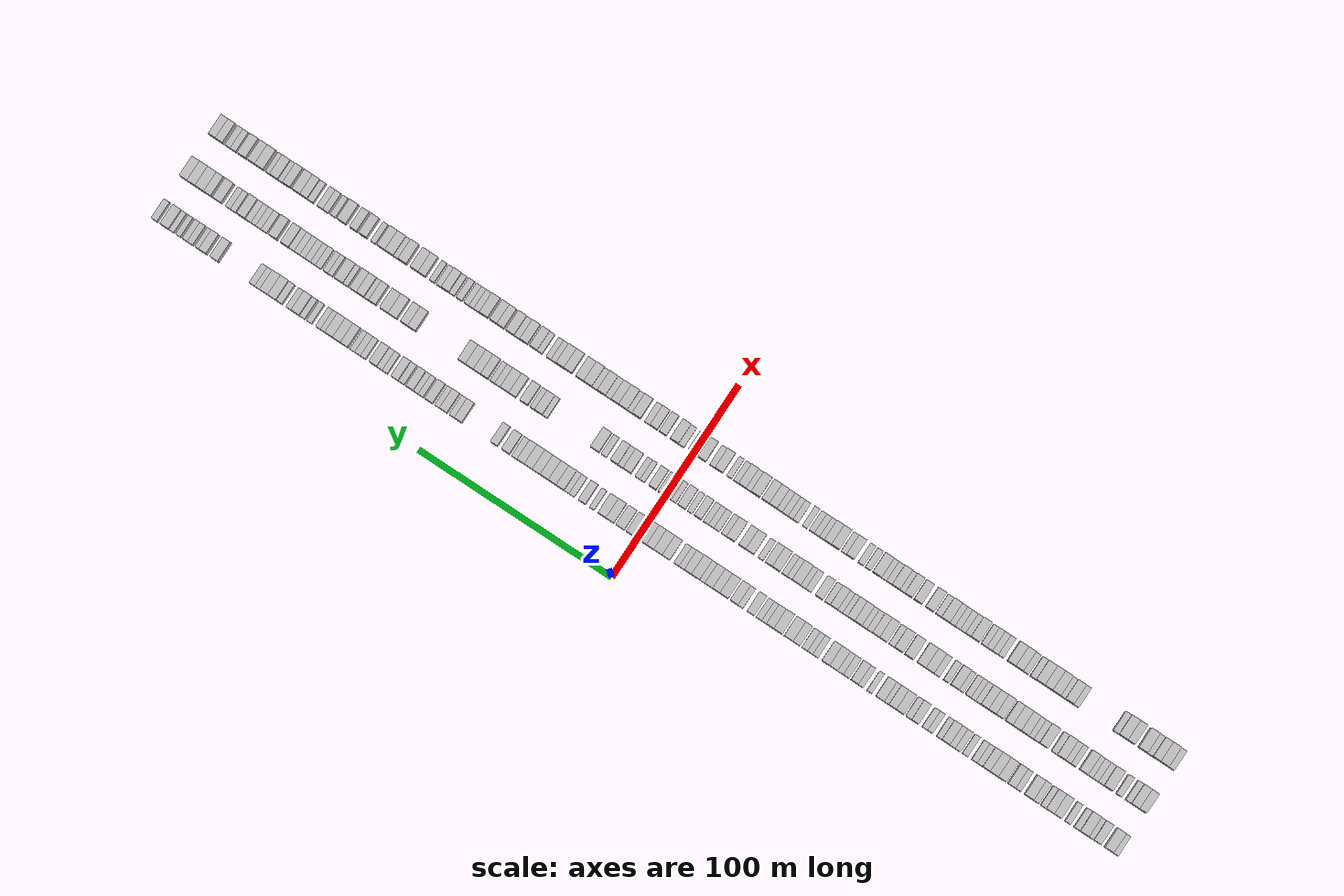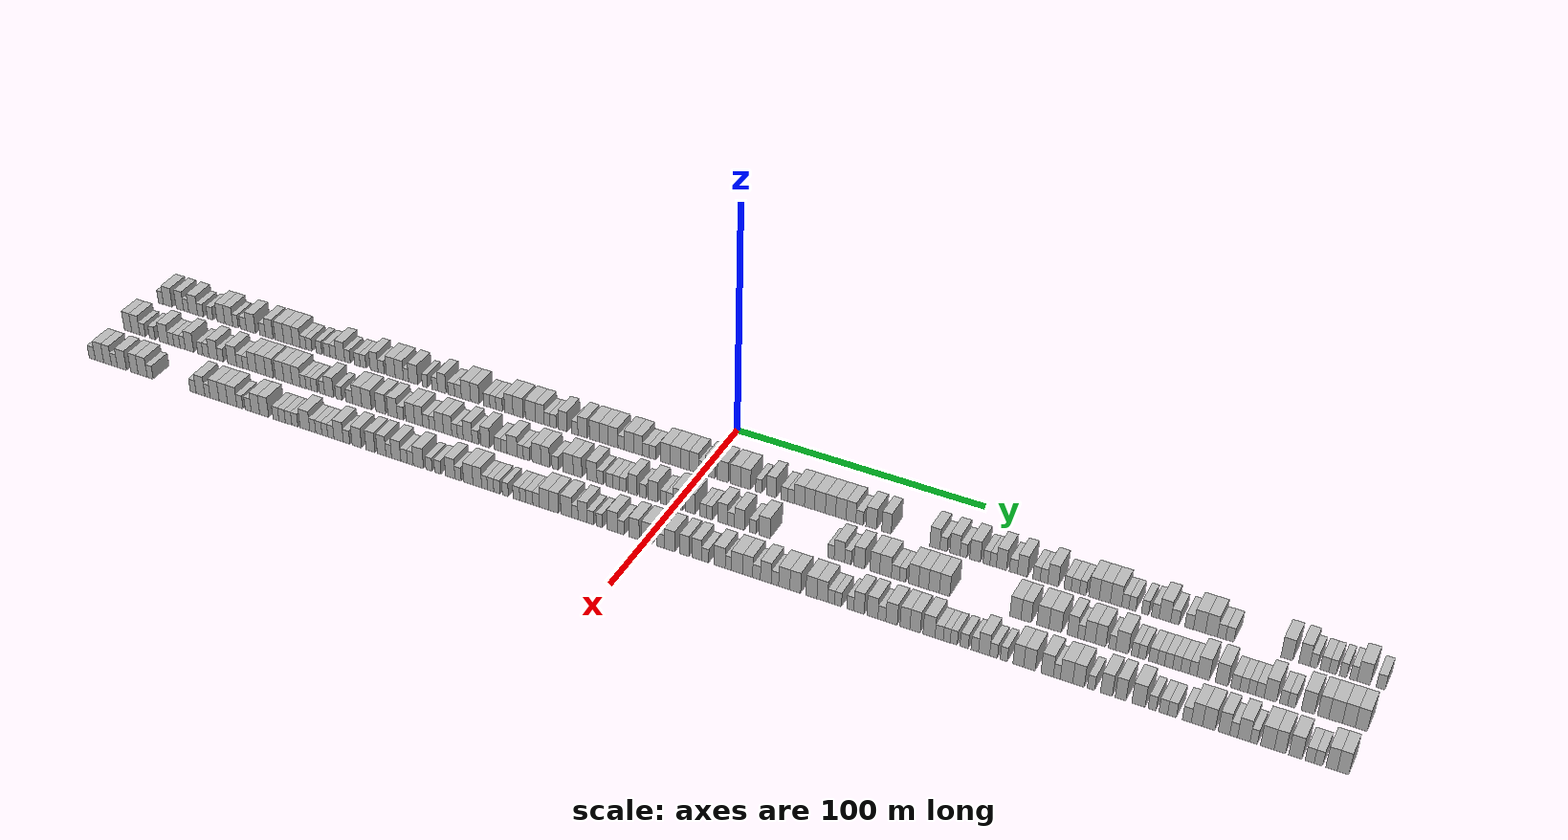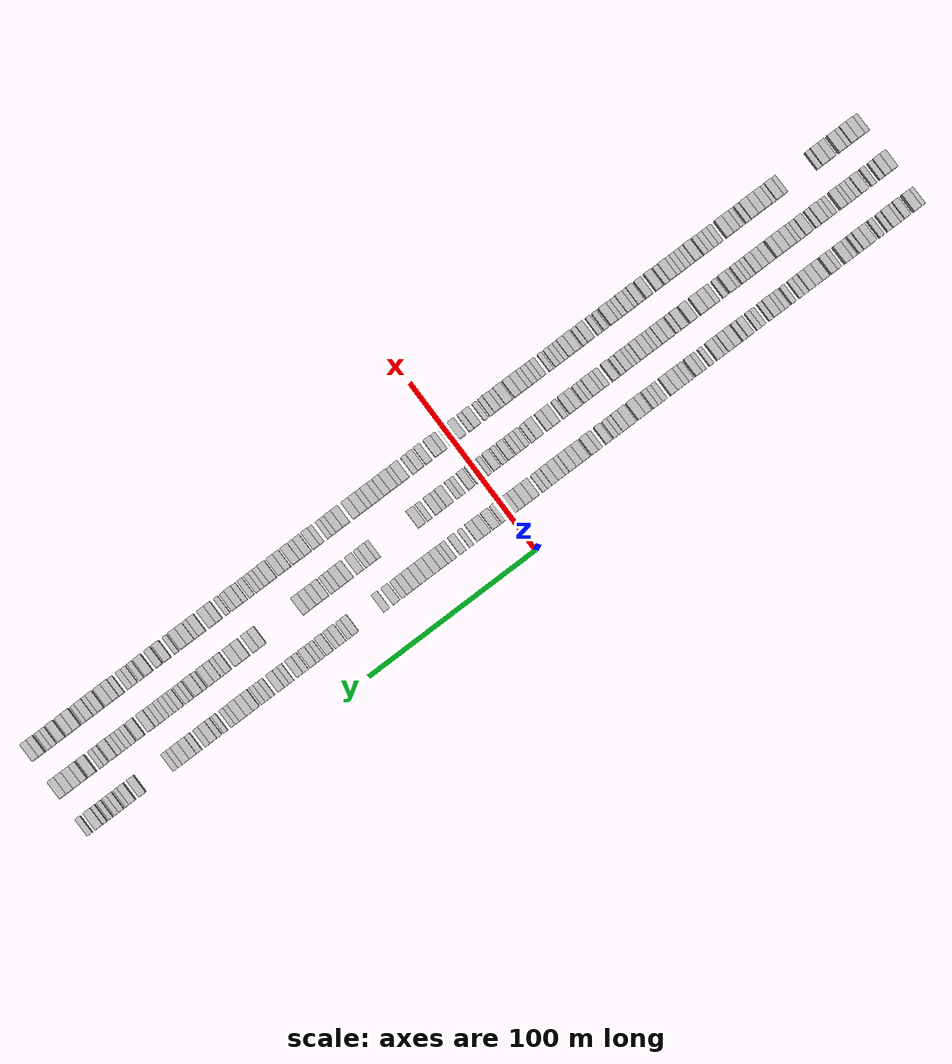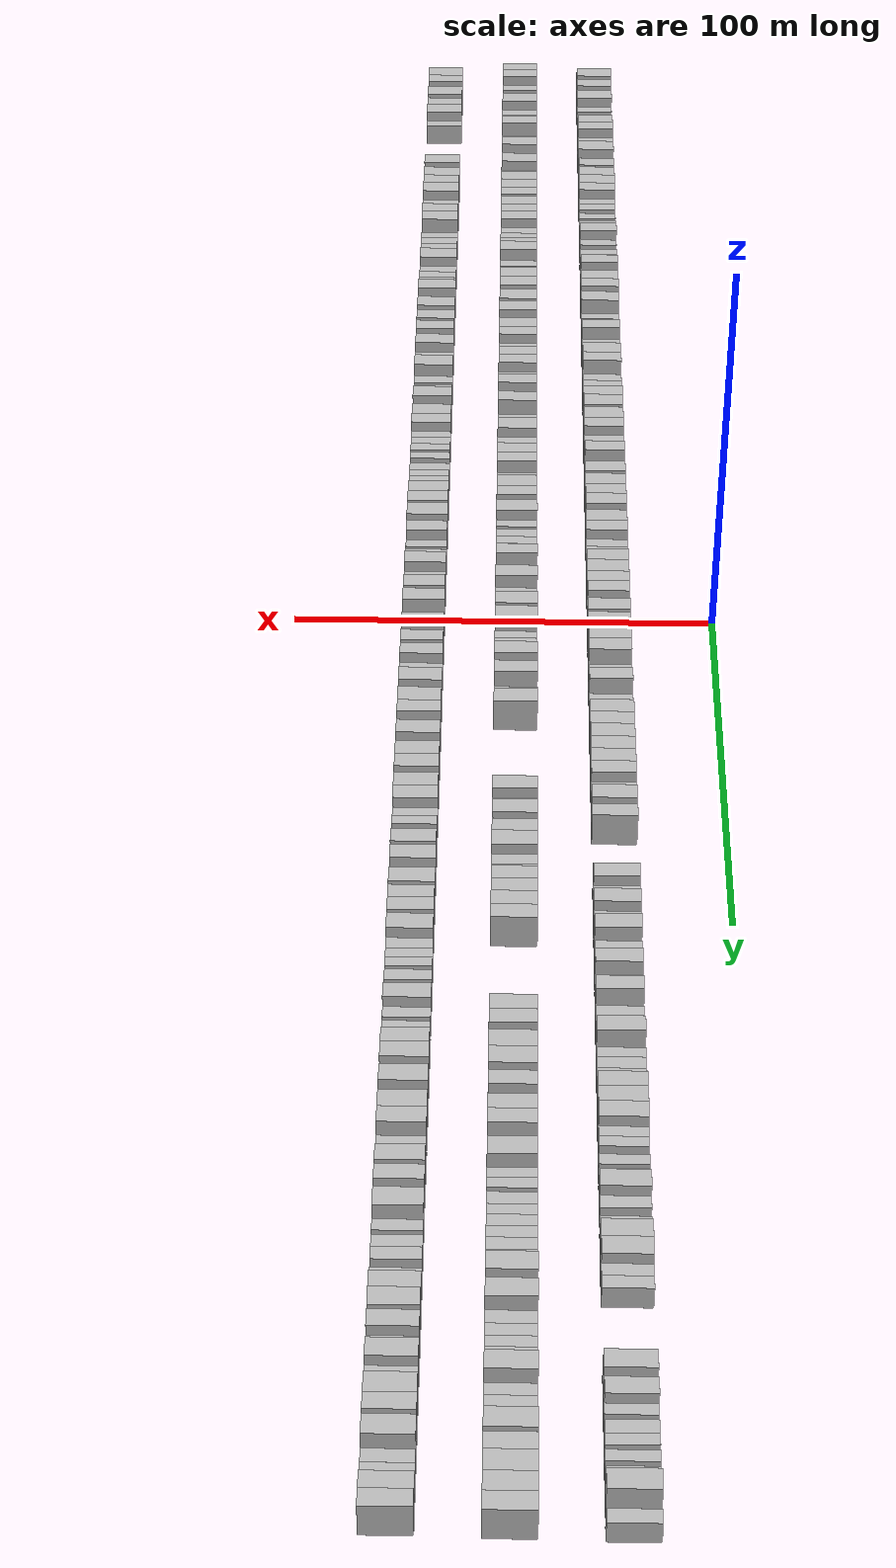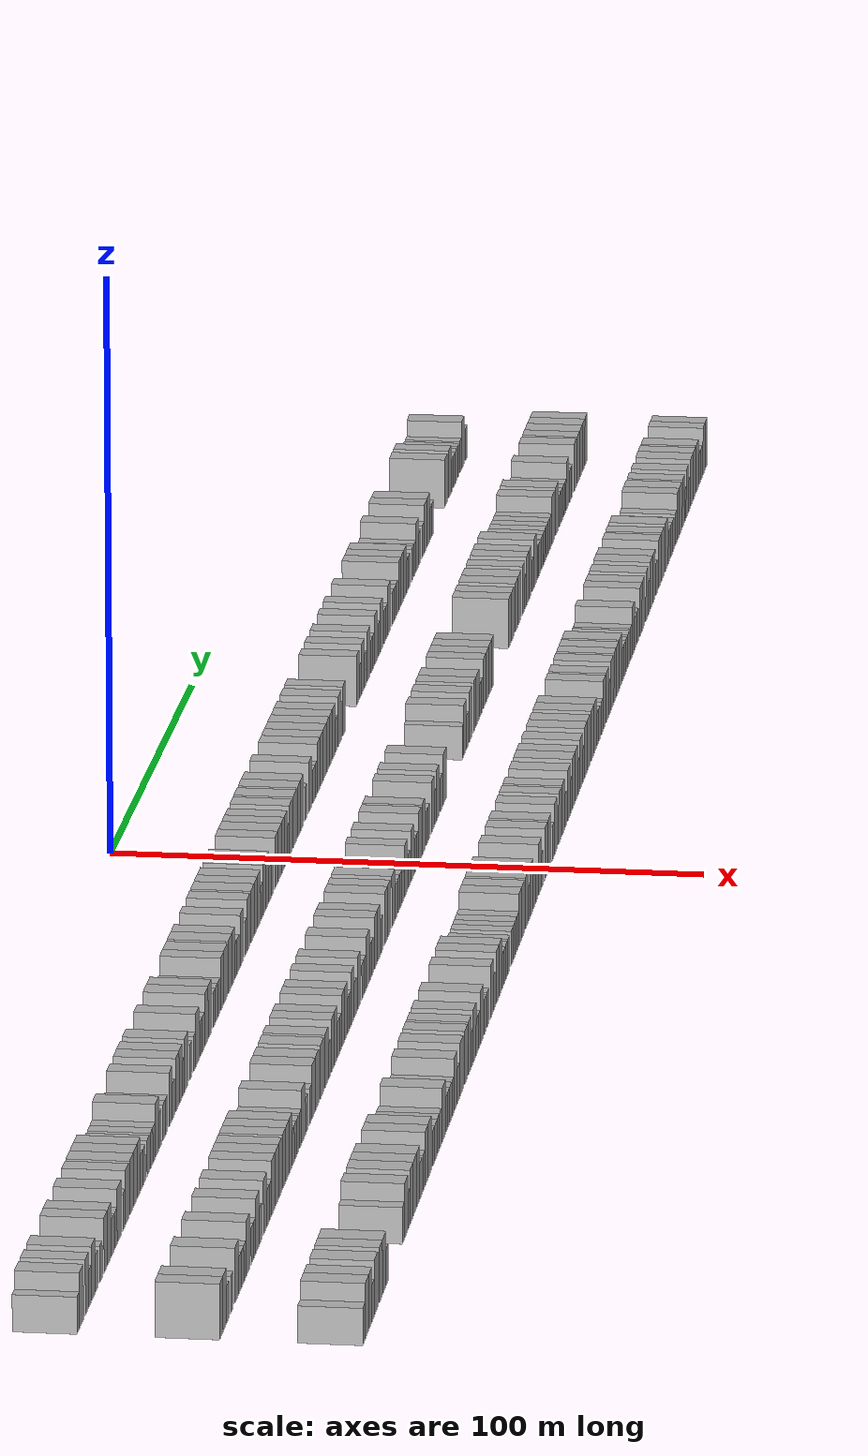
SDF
<sdf version="1.6">
 <world name="default">
  <scene>
   <sky><clouds><speed>12</speed></clouds></sky>
   <ambient>0.4 0.4 0.4 1</ambient>
   <background>0.7 0.7 0.7 1</background>
   <shadows>1</shadows>
  </scene>
  <gravity>0 0 -9.8066</gravity>
  <magnetic_field>6e-06 2.3e-05 -4.2e-05</magnetic_field>
  <physics default="0" name="default_physics" type="ode">
   <ode>
    <solver>
     <type>quick</type>
     <iters>10</iters>
     <sor>1.0</sor>
     <use_dynamic_moi_rescaling>0</use_dynamic_moi_rescaling>
    </solver>
    <constraints>
     <cfm>0</cfm>
     <erp>0.2</erp>
     <contact_max_correcting_vel>100</contact_max_correcting_vel>
     <contact_surface_layer>0.001</contact_surface_layer>
    </constraints>
   </ode>
   <max_step_size>0.004</max_step_size>
   <real_time_factor>1</real_time_factor>
   <real_time_update_rate>250</real_time_update_rate>
  </physics>
  <light name="sun" type="directional">
   <pose>0 0 10 0 0 0</pose>
   <diffuse>0.8 0.8 0.8 1</diffuse>
   <specular>0.2 0.2 0.2 1</specular>
   <attenuation>
    <range>1000</range>
    <constant>0.9</constant>
    <linear>0.01</linear>
    <quadratic>0.001</quadratic>
   </attenuation>
   <direction>-0.5 0.1 -0.9</direction>
  </light>
  <model name="building_1">
   <static>1</static>
   <pose>25.0000 -246.7035 0 0.000000 0.000000 0.000000</pose>
   <link name="link">
    <pose>0 0 3.00 0 0 0</pose>
    <collision name="collision"><geometry><box><size>10.0000 2.5931 6.0000</size></box></geometry></collision>
    <visual name="visual">
     <cast_shadows>0</cast_shadows>
     <geometry><box><size>10.0000 2.5931 6.0000</size></box></geometry>
     <material>
      <script>
       <uri>model://HANNAS_wall/materials/scripts</uri>
       <uri>model://HANNAS_wall/materials/textures</uri>
       <name>vrc/HANNAS_wall</name>
      </script>
     </material>
    </visual>
   </link>
  </model>
  <model name="building_2">
   <static>1</static>
   <pose>25.0000 -243.2107 0 0.000000 0.000000 0.000000</pose>
   <link name="link">
    <pose>0 0 4.50 0 0 0</pose>
    <collision name="collision"><geometry><box><size>10.0000 4.3924 9.0000</size></box></geometry></collision>
    <visual name="visual">
     <cast_shadows>0</cast_shadows>
     <geometry><box><size>10.0000 4.3924 9.0000</size></box></geometry>
     <material>
      <script>
       <uri>model://HANNAS_wall/materials/scripts</uri>
       <uri>model://HANNAS_wall/materials/textures</uri>
       <name>vrc/HANNAS_wall</name>
      </script>
     </material>
    </visual>
   </link>
  </model>
  <model name="building_3">
   <static>1</static>
   <pose>25.0000 -237.1460 0 0.000000 0.000000 0.000000</pose>
   <link name="link">
    <pose>0 0 4.50 0 0 0</pose>
    <collision name="collision"><geometry><box><size>10.0000 3.7371 9.0000</size></box></geometry></collision>
    <visual name="visual">
     <cast_shadows>0</cast_shadows>
     <geometry><box><size>10.0000 3.7371 9.0000</size></box></geometry>
     <material>
      <script>
       <uri>model://HANNAS_wall/materials/scripts</uri>
       <uri>model://HANNAS_wall/materials/textures</uri>
       <name>vrc/HANNAS_wall</name>
      </script>
     </material>
    </visual>
   </link>
  </model>
  <model name="building_4">
   <static>1</static>
   <pose>25.0000 -234.0140 0 0.000000 0.000000 0.000000</pose>
   <link name="link">
    <pose>0 0 3.00 0 0 0</pose>
    <collision name="collision"><geometry><box><size>10.0000 2.5270 6.0000</size></box></geometry></collision>
    <visual name="visual">
     <cast_shadows>0</cast_shadows>
     <geometry><box><size>10.0000 2.5270 6.0000</size></box></geometry>
     <material>
      <script>
       <uri>model://HANNAS_wall/materials/scripts</uri>
       <uri>model://HANNAS_wall/materials/textures</uri>
       <name>vrc/HANNAS_wall</name>
      </script>
     </material>
    </visual>
   </link>
  </model>
  <model name="building_5">
   <static>1</static>
   <pose>25.0000 -230.5331 0 0.000000 0.000000 0.000000</pose>
   <link name="link">
    <pose>0 0 4.50 0 0 0</pose>
    <collision name="collision"><geometry><box><size>10.0000 4.4348 9.0000</size></box></geometry></collision>
    <visual name="visual">
     <cast_shadows>0</cast_shadows>
     <geometry><box><size>10.0000 4.4348 9.0000</size></box></geometry>
     <material>
      <script>
       <uri>model://HANNAS_wall/materials/scripts</uri>
       <uri>model://HANNAS_wall/materials/textures</uri>
       <name>vrc/HANNAS_wall</name>
      </script>
     </material>
    </visual>
   </link>
  </model>
  <model name="building_6">
   <static>1</static>
   <pose>25.0000 -226.8758 0 0.000000 0.000000 0.000000</pose>
   <link name="link">
    <pose>0 0 3.00 0 0 0</pose>
    <collision name="collision"><geometry><box><size>10.0000 2.8798 6.0000</size></box></geometry></collision>
    <visual name="visual">
     <cast_shadows>0</cast_shadows>
     <geometry><box><size>10.0000 2.8798 6.0000</size></box></geometry>
     <material>
      <script>
       <uri>model://HANNAS_wall/materials/scripts</uri>
       <uri>model://HANNAS_wall/materials/textures</uri>
       <name>vrc/HANNAS_wall</name>
      </script>
     </material>
    </visual>
   </link>
  </model>
  <model name="building_7">
   <static>1</static>
   <pose>25.0000 -222.0543 0 0.000000 0.000000 0.000000</pose>
   <link name="link">
    <pose>0 0 3.00 0 0 0</pose>
    <collision name="collision"><geometry><box><size>10.0000 2.7632 6.0000</size></box></geometry></collision>
    <visual name="visual">
     <cast_shadows>0</cast_shadows>
     <geometry><box><size>10.0000 2.7632 6.0000</size></box></geometry>
     <material>
      <script>
       <uri>model://HANNAS_wall/materials/scripts</uri>
       <uri>model://HANNAS_wall/materials/textures</uri>
       <name>vrc/HANNAS_wall</name>
      </script>
     </material>
    </visual>
   </link>
  </model>
  <model name="building_8">
   <static>1</static>
   <pose>25.0000 -216.7543 0 0.000000 0.000000 0.000000</pose>
   <link name="link">
    <pose>0 0 4.50 0 0 0</pose>
    <collision name="collision"><geometry><box><size>10.0000 3.8368 9.0000</size></box></geometry></collision>
    <visual name="visual">
     <cast_shadows>0</cast_shadows>
     <geometry><box><size>10.0000 3.8368 9.0000</size></box></geometry>
     <material>
      <script>
       <uri>model://HANNAS_wall/materials/scripts</uri>
       <uri>model://HANNAS_wall/materials/textures</uri>
       <name>vrc/HANNAS_wall</name>
      </script>
     </material>
    </visual>
   </link>
  </model>
  <model name="building_9">
   <static>1</static>
   <pose>25.0000 -212.8642 0 0.000000 0.000000 0.000000</pose>
   <link name="link">
    <pose>0 0 4.50 0 0 0</pose>
    <collision name="collision"><geometry><box><size>10.0000 3.9433 9.0000</size></box></geometry></collision>
    <visual name="visual">
     <cast_shadows>0</cast_shadows>
     <geometry><box><size>10.0000 3.9433 9.0000</size></box></geometry>
     <material>
      <script>
       <uri>model://HANNAS_wall/materials/scripts</uri>
       <uri>model://HANNAS_wall/materials/textures</uri>
       <name>vrc/HANNAS_wall</name>
      </script>
     </material>
    </visual>
   </link>
  </model>
  <model name="building_10">
   <static>1</static>
   <pose>25.0000 -209.5752 0 0.000000 0.000000 0.000000</pose>
   <link name="link">
    <pose>0 0 3.00 0 0 0</pose>
    <collision name="collision"><geometry><box><size>10.0000 2.6347 6.0000</size></box></geometry></collision>
    <visual name="visual">
     <cast_shadows>0</cast_shadows>
     <geometry><box><size>10.0000 2.6347 6.0000</size></box></geometry>
     <material>
      <script>
       <uri>model://HANNAS_wall/materials/scripts</uri>
       <uri>model://HANNAS_wall/materials/textures</uri>
       <name>vrc/HANNAS_wall</name>
      </script>
     </material>
    </visual>
   </link>
  </model>
  <model name="building_11">
   <static>1</static>
   <pose>25.0000 -205.7691 0 0.000000 0.000000 0.000000</pose>
   <link name="link">
    <pose>0 0 3.00 0 0 0</pose>
    <collision name="collision"><geometry><box><size>10.0000 2.9775 6.0000</size></box></geometry></collision>
    <visual name="visual">
     <cast_shadows>0</cast_shadows>
     <geometry><box><size>10.0000 2.9775 6.0000</size></box></geometry>
     <material>
      <script>
       <uri>model://HANNAS_wall/materials/scripts</uri>
       <uri>model://HANNAS_wall/materials/textures</uri>
       <name>vrc/HANNAS_wall</name>
      </script>
     </material>
    </visual>
   </link>
  </model>
  <model name="building_12">
   <static>1</static>
   <pose>25.0000 -202.0633 0 0.000000 0.000000 0.000000</pose>
   <link name="link">
    <pose>0 0 4.50 0 0 0</pose>
    <collision name="collision"><geometry><box><size>10.0000 4.4340 9.0000</size></box></geometry></collision>
    <visual name="visual">
     <cast_shadows>0</cast_shadows>
     <geometry><box><size>10.0000 4.4340 9.0000</size></box></geometry>
     <material>
      <script>
       <uri>model://HANNAS_wall/materials/scripts</uri>
       <uri>model://HANNAS_wall/materials/textures</uri>
       <name>vrc/HANNAS_wall</name>
      </script>
     </material>
    </visual>
   </link>
  </model>
  <model name="building_13">
   <static>1</static>
   <pose>25.0000 -196.4389 0 0.000000 0.000000 0.000000</pose>
   <link name="link">
    <pose>0 0 3.00 0 0 0</pose>
    <collision name="collision"><geometry><box><size>10.0000 2.8147 6.0000</size></box></geometry></collision>
    <visual name="visual">
     <cast_shadows>0</cast_shadows>
     <geometry><box><size>10.0000 2.8147 6.0000</size></box></geometry>
     <material>
      <script>
       <uri>model://HANNAS_wall/materials/scripts</uri>
       <uri>model://HANNAS_wall/materials/textures</uri>
       <name>vrc/HANNAS_wall</name>
      </script>
     </material>
    </visual>
   </link>
  </model>
  <model name="building_14">
   <static>1</static>
   <pose>25.0000 -193.1797 0 0.000000 0.000000 0.000000</pose>
   <link name="link">
    <pose>0 0 4.50 0 0 0</pose>
    <collision name="collision"><geometry><box><size>10.0000 3.7037 9.0000</size></box></geometry></collision>
    <visual name="visual">
     <cast_shadows>0</cast_shadows>
     <geometry><box><size>10.0000 3.7037 9.0000</size></box></geometry>
     <material>
      <script>
       <uri>model://HANNAS_wall/materials/scripts</uri>
       <uri>model://HANNAS_wall/materials/textures</uri>
       <name>vrc/HANNAS_wall</name>
      </script>
     </material>
    </visual>
   </link>
  </model>
  <model name="building_15">
   <static>1</static>
   <pose>25.0000 -188.2392 0 0.000000 0.000000 0.000000</pose>
   <link name="link">
    <pose>0 0 4.50 0 0 0</pose>
    <collision name="collision"><geometry><box><size>10.0000 4.1774 9.0000</size></box></geometry></collision>
    <visual name="visual">
     <cast_shadows>0</cast_shadows>
     <geometry><box><size>10.0000 4.1774 9.0000</size></box></geometry>
     <material>
      <script>
       <uri>model://HANNAS_wall/materials/scripts</uri>
       <uri>model://HANNAS_wall/materials/textures</uri>
       <name>vrc/HANNAS_wall</name>
      </script>
     </material>
    </visual>
   </link>
  </model>
  <model name="building_16">
   <static>1</static>
   <pose>25.0000 -184.0465 0 0.000000 0.000000 0.000000</pose>
   <link name="link">
    <pose>0 0 4.50 0 0 0</pose>
    <collision name="collision"><geometry><box><size>10.0000 4.2081 9.0000</size></box></geometry></collision>
    <visual name="visual">
     <cast_shadows>0</cast_shadows>
     <geometry><box><size>10.0000 4.2081 9.0000</size></box></geometry>
     <material>
      <script>
       <uri>model://HANNAS_wall/materials/scripts</uri>
       <uri>model://HANNAS_wall/materials/textures</uri>
       <name>vrc/HANNAS_wall</name>
      </script>
     </material>
    </visual>
   </link>
  </model>
  <model name="building_17">
   <static>1</static>
   <pose>25.0000 -180.0953 0 0.000000 0.000000 0.000000</pose>
   <link name="link">
    <pose>0 0 4.50 0 0 0</pose>
    <collision name="collision"><geometry><box><size>10.0000 3.6942 9.0000</size></box></geometry></collision>
    <visual name="visual">
     <cast_shadows>0</cast_shadows>
     <geometry><box><size>10.0000 3.6942 9.0000</size></box></geometry>
     <material>
      <script>
       <uri>model://HANNAS_wall/materials/scripts</uri>
       <uri>model://HANNAS_wall/materials/textures</uri>
       <name>vrc/HANNAS_wall</name>
      </script>
     </material>
    </visual>
   </link>
  </model>
  <model name="building_18">
   <static>1</static>
   <pose>25.0000 -176.8453 0 0.000000 0.000000 0.000000</pose>
   <link name="link">
    <pose>0 0 3.00 0 0 0</pose>
    <collision name="collision"><geometry><box><size>10.0000 2.8059 6.0000</size></box></geometry></collision>
    <visual name="visual">
     <cast_shadows>0</cast_shadows>
     <geometry><box><size>10.0000 2.8059 6.0000</size></box></geometry>
     <material>
      <script>
       <uri>model://HANNAS_wall/materials/scripts</uri>
       <uri>model://HANNAS_wall/materials/textures</uri>
       <name>vrc/HANNAS_wall</name>
      </script>
     </material>
    </visual>
   </link>
  </model>
  <model name="building_19">
   <static>1</static>
   <pose>25.0000 -174.0509 0 0.000000 0.000000 0.000000</pose>
   <link name="link">
    <pose>0 0 3.00 0 0 0</pose>
    <collision name="collision"><geometry><box><size>10.0000 2.7828 6.0000</size></box></geometry></collision>
    <visual name="visual">
     <cast_shadows>0</cast_shadows>
     <geometry><box><size>10.0000 2.7828 6.0000</size></box></geometry>
     <material>
      <script>
       <uri>model://HANNAS_wall/materials/scripts</uri>
       <uri>model://HANNAS_wall/materials/textures</uri>
       <name>vrc/HANNAS_wall</name>
      </script>
     </material>
    </visual>
   </link>
  </model>
  <model name="building_20">
   <static>1</static>
   <pose>25.0000 -169.3061 0 0.000000 0.000000 0.000000</pose>
   <link name="link">
    <pose>0 0 3.00 0 0 0</pose>
    <collision name="collision"><geometry><box><size>10.0000 2.7068 6.0000</size></box></geometry></collision>
    <visual name="visual">
     <cast_shadows>0</cast_shadows>
     <geometry><box><size>10.0000 2.7068 6.0000</size></box></geometry>
     <material>
      <script>
       <uri>model://HANNAS_wall/materials/scripts</uri>
       <uri>model://HANNAS_wall/materials/textures</uri>
       <name>vrc/HANNAS_wall</name>
      </script>
     </material>
    </visual>
   </link>
  </model>
  <model name="building_21">
   <static>1</static>
   <pose>25.0000 -165.5229 0 0.000000 0.000000 0.000000</pose>
   <link name="link">
    <pose>0 0 3.00 0 0 0</pose>
    <collision name="collision"><geometry><box><size>10.0000 2.8596 6.0000</size></box></geometry></collision>
    <visual name="visual">
     <cast_shadows>0</cast_shadows>
     <geometry><box><size>10.0000 2.8596 6.0000</size></box></geometry>
     <material>
      <script>
       <uri>model://HANNAS_wall/materials/scripts</uri>
       <uri>model://HANNAS_wall/materials/textures</uri>
       <name>vrc/HANNAS_wall</name>
      </script>
     </material>
    </visual>
   </link>
  </model>
  <model name="building_22">
   <static>1</static>
   <pose>25.0000 -162.6863 0 0.000000 0.000000 0.000000</pose>
   <link name="link">
    <pose>0 0 3.00 0 0 0</pose>
    <collision name="collision"><geometry><box><size>10.0000 2.8137 6.0000</size></box></geometry></collision>
    <visual name="visual">
     <cast_shadows>0</cast_shadows>
     <geometry><box><size>10.0000 2.8137 6.0000</size></box></geometry>
     <material>
      <script>
       <uri>model://HANNAS_wall/materials/scripts</uri>
       <uri>model://HANNAS_wall/materials/textures</uri>
       <name>vrc/HANNAS_wall</name>
      </script>
     </material>
    </visual>
   </link>
  </model>
  <model name="building_23">
   <static>1</static>
   <pose>25.0000 -159.2390 0 0.000000 0.000000 0.000000</pose>
   <link name="link">
    <pose>0 0 4.50 0 0 0</pose>
    <collision name="collision"><geometry><box><size>10.0000 4.0809 9.0000</size></box></geometry></collision>
    <visual name="visual">
     <cast_shadows>0</cast_shadows>
     <geometry><box><size>10.0000 4.0809 9.0000</size></box></geometry>
     <material>
      <script>
       <uri>model://HANNAS_wall/materials/scripts</uri>
       <uri>model://HANNAS_wall/materials/textures</uri>
       <name>vrc/HANNAS_wall</name>
      </script>
     </material>
    </visual>
   </link>
  </model>
  <model name="building_24">
   <static>1</static>
   <pose>25.0000 -155.8877 0 0.000000 0.000000 0.000000</pose>
   <link name="link">
    <pose>0 0 3.00 0 0 0</pose>
    <collision name="collision"><geometry><box><size>10.0000 2.6216 6.0000</size></box></geometry></collision>
    <visual name="visual">
     <cast_shadows>0</cast_shadows>
     <geometry><box><size>10.0000 2.6216 6.0000</size></box></geometry>
     <material>
      <script>
       <uri>model://HANNAS_wall/materials/scripts</uri>
       <uri>model://HANNAS_wall/materials/textures</uri>
       <name>vrc/HANNAS_wall</name>
      </script>
     </material>
    </visual>
   </link>
  </model>
  <model name="building_25">
   <static>1</static>
   <pose>25.0000 -151.2489 0 0.000000 0.000000 0.000000</pose>
   <link name="link">
    <pose>0 0 3.00 0 0 0</pose>
    <collision name="collision"><geometry><box><size>10.0000 2.6561 6.0000</size></box></geometry></collision>
    <visual name="visual">
     <cast_shadows>0</cast_shadows>
     <geometry><box><size>10.0000 2.6561 6.0000</size></box></geometry>
     <material>
      <script>
       <uri>model://HANNAS_wall/materials/scripts</uri>
       <uri>model://HANNAS_wall/materials/textures</uri>
       <name>vrc/HANNAS_wall</name>
      </script>
     </material>
    </visual>
   </link>
  </model>
  <model name="building_26">
   <static>1</static>
   <pose>25.0000 -148.5722 0 0.000000 0.000000 0.000000</pose>
   <link name="link">
    <pose>0 0 3.00 0 0 0</pose>
    <collision name="collision"><geometry><box><size>10.0000 2.6973 6.0000</size></box></geometry></collision>
    <visual name="visual">
     <cast_shadows>0</cast_shadows>
     <geometry><box><size>10.0000 2.6973 6.0000</size></box></geometry>
     <material>
      <script>
       <uri>model://HANNAS_wall/materials/scripts</uri>
       <uri>model://HANNAS_wall/materials/textures</uri>
       <name>vrc/HANNAS_wall</name>
      </script>
     </material>
    </visual>
   </link>
  </model>
  <model name="building_27">
   <static>1</static>
   <pose>25.0000 -143.4111 0 0.000000 0.000000 0.000000</pose>
   <link name="link">
    <pose>0 0 4.50 0 0 0</pose>
    <collision name="collision"><geometry><box><size>10.0000 3.6249 9.0000</size></box></geometry></collision>
    <visual name="visual">
     <cast_shadows>0</cast_shadows>
     <geometry><box><size>10.0000 3.6249 9.0000</size></box></geometry>
     <material>
      <script>
       <uri>model://HANNAS_wall/materials/scripts</uri>
       <uri>model://HANNAS_wall/materials/textures</uri>
       <name>vrc/HANNAS_wall</name>
      </script>
     </material>
    </visual>
   </link>
  </model>
  <model name="building_28">
   <static>1</static>
   <pose>25.0000 -140.1677 0 0.000000 0.000000 0.000000</pose>
   <link name="link">
    <pose>0 0 3.00 0 0 0</pose>
    <collision name="collision"><geometry><box><size>10.0000 2.8621 6.0000</size></box></geometry></collision>
    <visual name="visual">
     <cast_shadows>0</cast_shadows>
     <geometry><box><size>10.0000 2.8621 6.0000</size></box></geometry>
     <material>
      <script>
       <uri>model://HANNAS_wall/materials/scripts</uri>
       <uri>model://HANNAS_wall/materials/textures</uri>
       <name>vrc/HANNAS_wall</name>
      </script>
     </material>
    </visual>
   </link>
  </model>
  <model name="building_29">
   <static>1</static>
   <pose>25.0000 -135.7053 0 0.000000 0.000000 0.000000</pose>
   <link name="link">
    <pose>0 0 4.50 0 0 0</pose>
    <collision name="collision"><geometry><box><size>10.0000 4.0627 9.0000</size></box></geometry></collision>
    <visual name="visual">
     <cast_shadows>0</cast_shadows>
     <geometry><box><size>10.0000 4.0627 9.0000</size></box></geometry>
     <material>
      <script>
       <uri>model://HANNAS_wall/materials/scripts</uri>
       <uri>model://HANNAS_wall/materials/textures</uri>
       <name>vrc/HANNAS_wall</name>
      </script>
     </material>
    </visual>
   </link>
  </model>
  <model name="building_30">
   <static>1</static>
   <pose>25.0000 -131.7794 0 0.000000 0.000000 0.000000</pose>
   <link name="link">
    <pose>0 0 4.50 0 0 0</pose>
    <collision name="collision"><geometry><box><size>10.0000 3.7890 9.0000</size></box></geometry></collision>
    <visual name="visual">
     <cast_shadows>0</cast_shadows>
     <geometry><box><size>10.0000 3.7890 9.0000</size></box></geometry>
     <material>
      <script>
       <uri>model://HANNAS_wall/materials/scripts</uri>
       <uri>model://HANNAS_wall/materials/textures</uri>
       <name>vrc/HANNAS_wall</name>
      </script>
     </material>
    </visual>
   </link>
  </model>
  <model name="building_31">
   <static>1</static>
   <pose>25.0000 -128.6783 0 0.000000 0.000000 0.000000</pose>
   <link name="link">
    <pose>0 0 3.00 0 0 0</pose>
    <collision name="collision"><geometry><box><size>10.0000 2.4132 6.0000</size></box></geometry></collision>
    <visual name="visual">
     <cast_shadows>0</cast_shadows>
     <geometry><box><size>10.0000 2.4132 6.0000</size></box></geometry>
     <material>
      <script>
       <uri>model://HANNAS_wall/materials/scripts</uri>
       <uri>model://HANNAS_wall/materials/textures</uri>
       <name>vrc/HANNAS_wall</name>
      </script>
     </material>
    </visual>
   </link>
  </model>
  <model name="building_32">
   <static>1</static>
   <pose>25.0000 -125.3618 0 0.000000 0.000000 0.000000</pose>
   <link name="link">
    <pose>0 0 4.50 0 0 0</pose>
    <collision name="collision"><geometry><box><size>10.0000 4.2197 9.0000</size></box></geometry></collision>
    <visual name="visual">
     <cast_shadows>0</cast_shadows>
     <geometry><box><size>10.0000 4.2197 9.0000</size></box></geometry>
     <material>
      <script>
       <uri>model://HANNAS_wall/materials/scripts</uri>
       <uri>model://HANNAS_wall/materials/textures</uri>
       <name>vrc/HANNAS_wall</name>
      </script>
     </material>
    </visual>
   </link>
  </model>
  <model name="building_33">
   <static>1</static>
   <pose>25.0000 -120.0268 0 0.000000 0.000000 0.000000</pose>
   <link name="link">
    <pose>0 0 3.00 0 0 0</pose>
    <collision name="collision"><geometry><box><size>10.0000 2.4503 6.0000</size></box></geometry></collision>
    <visual name="visual">
     <cast_shadows>0</cast_shadows>
     <geometry><box><size>10.0000 2.4503 6.0000</size></box></geometry>
     <material>
      <script>
       <uri>model://HANNAS_wall/materials/scripts</uri>
       <uri>model://HANNAS_wall/materials/textures</uri>
       <name>vrc/HANNAS_wall</name>
      </script>
     </material>
    </visual>
   </link>
  </model>
  <model name="building_34">
   <static>1</static>
   <pose>25.0000 -115.5090 0 0.000000 0.000000 0.000000</pose>
   <link name="link">
    <pose>0 0 3.00 0 0 0</pose>
    <collision name="collision"><geometry><box><size>10.0000 2.5854 6.0000</size></box></geometry></collision>
    <visual name="visual">
     <cast_shadows>0</cast_shadows>
     <geometry><box><size>10.0000 2.5854 6.0000</size></box></geometry>
     <material>
      <script>
       <uri>model://HANNAS_wall/materials/scripts</uri>
       <uri>model://HANNAS_wall/materials/textures</uri>
       <name>vrc/HANNAS_wall</name>
      </script>
     </material>
    </visual>
   </link>
  </model>
  <model name="building_35">
   <static>1</static>
   <pose>25.0000 -112.3240 0 0.000000 0.000000 0.000000</pose>
   <link name="link">
    <pose>0 0 4.50 0 0 0</pose>
    <collision name="collision"><geometry><box><size>10.0000 3.7846 9.0000</size></box></geometry></collision>
    <visual name="visual">
     <cast_shadows>0</cast_shadows>
     <geometry><box><size>10.0000 3.7846 9.0000</size></box></geometry>
     <material>
      <script>
       <uri>model://HANNAS_wall/materials/scripts</uri>
       <uri>model://HANNAS_wall/materials/textures</uri>
       <name>vrc/HANNAS_wall</name>
      </script>
     </material>
    </visual>
   </link>
  </model>
  <model name="building_36">
   <static>1</static>
   <pose>25.0000 -107.9393 0 0.000000 0.000000 0.000000</pose>
   <link name="link">
    <pose>0 0 3.00 0 0 0</pose>
    <collision name="collision"><geometry><box><size>10.0000 2.9846 6.0000</size></box></geometry></collision>
    <visual name="visual">
     <cast_shadows>0</cast_shadows>
     <geometry><box><size>10.0000 2.9846 6.0000</size></box></geometry>
     <material>
      <script>
       <uri>model://HANNAS_wall/materials/scripts</uri>
       <uri>model://HANNAS_wall/materials/textures</uri>
       <name>vrc/HANNAS_wall</name>
      </script>
     </material>
    </visual>
   </link>
  </model>
  <model name="building_37">
   <static>1</static>
   <pose>25.0000 -104.9839 0 0.000000 0.000000 0.000000</pose>
   <link name="link">
    <pose>0 0 3.00 0 0 0</pose>
    <collision name="collision"><geometry><box><size>10.0000 2.9262 6.0000</size></box></geometry></collision>
    <visual name="visual">
     <cast_shadows>0</cast_shadows>
     <geometry><box><size>10.0000 2.9262 6.0000</size></box></geometry>
     <material>
      <script>
       <uri>model://HANNAS_wall/materials/scripts</uri>
       <uri>model://HANNAS_wall/materials/textures</uri>
       <name>vrc/HANNAS_wall</name>
      </script>
     </material>
    </visual>
   </link>
  </model>
  <model name="building_38">
   <static>1</static>
   <pose>25.0000 -101.4277 0 0.000000 0.000000 0.000000</pose>
   <link name="link">
    <pose>0 0 4.50 0 0 0</pose>
    <collision name="collision"><geometry><box><size>10.0000 4.1862 9.0000</size></box></geometry></collision>
    <visual name="visual">
     <cast_shadows>0</cast_shadows>
     <geometry><box><size>10.0000 4.1862 9.0000</size></box></geometry>
     <material>
      <script>
       <uri>model://HANNAS_wall/materials/scripts</uri>
       <uri>model://HANNAS_wall/materials/textures</uri>
       <name>vrc/HANNAS_wall</name>
      </script>
     </material>
    </visual>
   </link>
  </model>
  <model name="building_39">
   <static>1</static>
   <pose>25.0000 -97.4000 0 0.000000 0.000000 0.000000</pose>
   <link name="link">
    <pose>0 0 4.50 0 0 0</pose>
    <collision name="collision"><geometry><box><size>10.0000 3.8694 9.0000</size></box></geometry></collision>
    <visual name="visual">
     <cast_shadows>0</cast_shadows>
     <geometry><box><size>10.0000 3.8694 9.0000</size></box></geometry>
     <material>
      <script>
       <uri>model://HANNAS_wall/materials/scripts</uri>
       <uri>model://HANNAS_wall/materials/textures</uri>
       <name>vrc/HANNAS_wall</name>
      </script>
     </material>
    </visual>
   </link>
  </model>
  <model name="building_40">
   <static>1</static>
   <pose>25.0000 -92.0973 0 0.000000 0.000000 0.000000</pose>
   <link name="link">
    <pose>0 0 3.00 0 0 0</pose>
    <collision name="collision"><geometry><box><size>10.0000 2.7360 6.0000</size></box></geometry></collision>
    <visual name="visual">
     <cast_shadows>0</cast_shadows>
     <geometry><box><size>10.0000 2.7360 6.0000</size></box></geometry>
     <material>
      <script>
       <uri>model://HANNAS_wall/materials/scripts</uri>
       <uri>model://HANNAS_wall/materials/textures</uri>
       <name>vrc/HANNAS_wall</name>
      </script>
     </material>
    </visual>
   </link>
  </model>
  <model name="building_41">
   <static>1</static>
   <pose>25.0000 -89.4035 0 0.000000 0.000000 0.000000</pose>
   <link name="link">
    <pose>0 0 3.00 0 0 0</pose>
    <collision name="collision"><geometry><box><size>10.0000 2.6514 6.0000</size></box></geometry></collision>
    <visual name="visual">
     <cast_shadows>0</cast_shadows>
     <geometry><box><size>10.0000 2.6514 6.0000</size></box></geometry>
     <material>
      <script>
       <uri>model://HANNAS_wall/materials/scripts</uri>
       <uri>model://HANNAS_wall/materials/textures</uri>
       <name>vrc/HANNAS_wall</name>
      </script>
     </material>
    </visual>
   </link>
  </model>
  <model name="building_42">
   <static>1</static>
   <pose>25.0000 -86.6004 0 0.000000 0.000000 0.000000</pose>
   <link name="link">
    <pose>0 0 3.00 0 0 0</pose>
    <collision name="collision"><geometry><box><size>10.0000 2.9548 6.0000</size></box></geometry></collision>
    <visual name="visual">
     <cast_shadows>0</cast_shadows>
     <geometry><box><size>10.0000 2.9548 6.0000</size></box></geometry>
     <material>
      <script>
       <uri>model://HANNAS_wall/materials/scripts</uri>
       <uri>model://HANNAS_wall/materials/textures</uri>
       <name>vrc/HANNAS_wall</name>
      </script>
     </material>
    </visual>
   </link>
  </model>
  <model name="building_43">
   <static>1</static>
   <pose>25.0000 -82.3027 0 0.000000 0.000000 0.000000</pose>
   <link name="link">
    <pose>0 0 4.50 0 0 0</pose>
    <collision name="collision"><geometry><box><size>10.0000 3.6406 9.0000</size></box></geometry></collision>
    <visual name="visual">
     <cast_shadows>0</cast_shadows>
     <geometry><box><size>10.0000 3.6406 9.0000</size></box></geometry>
     <material>
      <script>
       <uri>model://HANNAS_wall/materials/scripts</uri>
       <uri>model://HANNAS_wall/materials/textures</uri>
       <name>vrc/HANNAS_wall</name>
      </script>
     </material>
    </visual>
   </link>
  </model>
  <model name="building_44">
   <static>1</static>
   <pose>25.0000 -78.2367 0 0.000000 0.000000 0.000000</pose>
   <link name="link">
    <pose>0 0 4.50 0 0 0</pose>
    <collision name="collision"><geometry><box><size>10.0000 4.4914 9.0000</size></box></geometry></collision>
    <visual name="visual">
     <cast_shadows>0</cast_shadows>
     <geometry><box><size>10.0000 4.4914 9.0000</size></box></geometry>
     <material>
      <script>
       <uri>model://HANNAS_wall/materials/scripts</uri>
       <uri>model://HANNAS_wall/materials/textures</uri>
       <name>vrc/HANNAS_wall</name>
      </script>
     </material>
    </visual>
   </link>
  </model>
  <model name="building_45">
   <static>1</static>
   <pose>25.0000 -72.7634 0 0.000000 0.000000 0.000000</pose>
   <link name="link">
    <pose>0 0 4.50 0 0 0</pose>
    <collision name="collision"><geometry><box><size>10.0000 4.4552 9.0000</size></box></geometry></collision>
    <visual name="visual">
     <cast_shadows>0</cast_shadows>
     <geometry><box><size>10.0000 4.4552 9.0000</size></box></geometry>
     <material>
      <script>
       <uri>model://HANNAS_wall/materials/scripts</uri>
       <uri>model://HANNAS_wall/materials/textures</uri>
       <name>vrc/HANNAS_wall</name>
      </script>
     </material>
    </visual>
   </link>
  </model>
  <model name="building_46">
   <static>1</static>
   <pose>25.0000 -68.6623 0 0.000000 0.000000 0.000000</pose>
   <link name="link">
    <pose>0 0 4.50 0 0 0</pose>
    <collision name="collision"><geometry><box><size>10.0000 3.7471 9.0000</size></box></geometry></collision>
    <visual name="visual">
     <cast_shadows>0</cast_shadows>
     <geometry><box><size>10.0000 3.7471 9.0000</size></box></geometry>
     <material>
      <script>
       <uri>model://HANNAS_wall/materials/scripts</uri>
       <uri>model://HANNAS_wall/materials/textures</uri>
       <name>vrc/HANNAS_wall</name>
      </script>
     </material>
    </visual>
   </link>
  </model>
  <model name="building_47">
   <static>1</static>
   <pose>25.0000 -65.5764 0 0.000000 0.000000 0.000000</pose>
   <link name="link">
    <pose>0 0 3.00 0 0 0</pose>
    <collision name="collision"><geometry><box><size>10.0000 2.4248 6.0000</size></box></geometry></collision>
    <visual name="visual">
     <cast_shadows>0</cast_shadows>
     <geometry><box><size>10.0000 2.4248 6.0000</size></box></geometry>
     <material>
      <script>
       <uri>model://HANNAS_wall/materials/scripts</uri>
       <uri>model://HANNAS_wall/materials/textures</uri>
       <name>vrc/HANNAS_wall</name>
      </script>
     </material>
    </visual>
   </link>
  </model>
  <model name="building_48">
   <static>1</static>
   <pose>25.0000 -62.9529 0 0.000000 0.000000 0.000000</pose>
   <link name="link">
    <pose>0 0 3.00 0 0 0</pose>
    <collision name="collision"><geometry><box><size>10.0000 2.8220 6.0000</size></box></geometry></collision>
    <visual name="visual">
     <cast_shadows>0</cast_shadows>
     <geometry><box><size>10.0000 2.8220 6.0000</size></box></geometry>
     <material>
      <script>
       <uri>model://HANNAS_wall/materials/scripts</uri>
       <uri>model://HANNAS_wall/materials/textures</uri>
       <name>vrc/HANNAS_wall</name>
      </script>
     </material>
    </visual>
   </link>
  </model>
  <model name="building_49">
   <static>1</static>
   <pose>25.0000 -58.6655 0 0.000000 0.000000 0.000000</pose>
   <link name="link">
    <pose>0 0 4.50 0 0 0</pose>
    <collision name="collision"><geometry><box><size>10.0000 3.7529 9.0000</size></box></geometry></collision>
    <visual name="visual">
     <cast_shadows>0</cast_shadows>
     <geometry><box><size>10.0000 3.7529 9.0000</size></box></geometry>
     <material>
      <script>
       <uri>model://HANNAS_wall/materials/scripts</uri>
       <uri>model://HANNAS_wall/materials/textures</uri>
       <name>vrc/HANNAS_wall</name>
      </script>
     </material>
    </visual>
   </link>
  </model>
  <model name="building_50">
   <static>1</static>
   <pose>25.0000 -53.4581 0 0.000000 0.000000 0.000000</pose>
   <link name="link">
    <pose>0 0 3.00 0 0 0</pose>
    <collision name="collision"><geometry><box><size>10.0000 2.6618 6.0000</size></box></geometry></collision>
    <visual name="visual">
     <cast_shadows>0</cast_shadows>
     <geometry><box><size>10.0000 2.6618 6.0000</size></box></geometry>
     <material>
      <script>
       <uri>model://HANNAS_wall/materials/scripts</uri>
       <uri>model://HANNAS_wall/materials/textures</uri>
       <name>vrc/HANNAS_wall</name>
      </script>
     </material>
    </visual>
   </link>
  </model>
  <model name="building_51">
   <static>1</static>
   <pose>25.0000 -50.1137 0 0.000000 0.000000 0.000000</pose>
   <link name="link">
    <pose>0 0 4.50 0 0 0</pose>
    <collision name="collision"><geometry><box><size>10.0000 4.0269 9.0000</size></box></geometry></collision>
    <visual name="visual">
     <cast_shadows>0</cast_shadows>
     <geometry><box><size>10.0000 4.0269 9.0000</size></box></geometry>
     <material>
      <script>
       <uri>model://HANNAS_wall/materials/scripts</uri>
       <uri>model://HANNAS_wall/materials/textures</uri>
       <name>vrc/HANNAS_wall</name>
      </script>
     </material>
    </visual>
   </link>
  </model>
  <model name="building_52">
   <static>1</static>
   <pose>25.0000 -44.9490 0 0.000000 0.000000 0.000000</pose>
   <link name="link">
    <pose>0 0 4.50 0 0 0</pose>
    <collision name="collision"><geometry><box><size>10.0000 4.3026 9.0000</size></box></geometry></collision>
    <visual name="visual">
     <cast_shadows>0</cast_shadows>
     <geometry><box><size>10.0000 4.3026 9.0000</size></box></geometry>
     <material>
      <script>
       <uri>model://HANNAS_wall/materials/scripts</uri>
       <uri>model://HANNAS_wall/materials/textures</uri>
       <name>vrc/HANNAS_wall</name>
      </script>
     </material>
    </visual>
   </link>
  </model>
  <model name="building_53">
   <static>1</static>
   <pose>25.0000 -40.9381 0 0.000000 0.000000 0.000000</pose>
   <link name="link">
    <pose>0 0 4.50 0 0 0</pose>
    <collision name="collision"><geometry><box><size>10.0000 3.7192 9.0000</size></box></geometry></collision>
    <visual name="visual">
     <cast_shadows>0</cast_shadows>
     <geometry><box><size>10.0000 3.7192 9.0000</size></box></geometry>
     <material>
      <script>
       <uri>model://HANNAS_wall/materials/scripts</uri>
       <uri>model://HANNAS_wall/materials/textures</uri>
       <name>vrc/HANNAS_wall</name>
      </script>
     </material>
    </visual>
   </link>
  </model>
  <model name="building_54">
   <static>1</static>
   <pose>25.0000 -37.0267 0 0.000000 0.000000 0.000000</pose>
   <link name="link">
    <pose>0 0 4.50 0 0 0</pose>
    <collision name="collision"><geometry><box><size>10.0000 4.1036 9.0000</size></box></geometry></collision>
    <visual name="visual">
     <cast_shadows>0</cast_shadows>
     <geometry><box><size>10.0000 4.1036 9.0000</size></box></geometry>
     <material>
      <script>
       <uri>model://HANNAS_wall/materials/scripts</uri>
       <uri>model://HANNAS_wall/materials/textures</uri>
       <name>vrc/HANNAS_wall</name>
      </script>
     </material>
    </visual>
   </link>
  </model>
  <model name="building_55">
   <static>1</static>
   <pose>25.0000 -33.6803 0 0.000000 0.000000 0.000000</pose>
   <link name="link">
    <pose>0 0 3.00 0 0 0</pose>
    <collision name="collision"><geometry><box><size>10.0000 2.5893 6.0000</size></box></geometry></collision>
    <visual name="visual">
     <cast_shadows>0</cast_shadows>
     <geometry><box><size>10.0000 2.5893 6.0000</size></box></geometry>
     <material>
      <script>
       <uri>model://HANNAS_wall/materials/scripts</uri>
       <uri>model://HANNAS_wall/materials/textures</uri>
       <name>vrc/HANNAS_wall</name>
      </script>
     </material>
    </visual>
   </link>
  </model>
  <model name="building_56">
   <static>1</static>
   <pose>25.0000 -30.2740 0 0.000000 0.000000 0.000000</pose>
   <link name="link">
    <pose>0 0 4.50 0 0 0</pose>
    <collision name="collision"><geometry><box><size>10.0000 4.2232 9.0000</size></box></geometry></collision>
    <visual name="visual">
     <cast_shadows>0</cast_shadows>
     <geometry><box><size>10.0000 4.2232 9.0000</size></box></geometry>
     <material>
      <script>
       <uri>model://HANNAS_wall/materials/scripts</uri>
       <uri>model://HANNAS_wall/materials/textures</uri>
       <name>vrc/HANNAS_wall</name>
      </script>
     </material>
    </visual>
   </link>
  </model>
  <model name="building_57">
   <static>1</static>
   <pose>25.0000 -26.3121 0 0.000000 0.000000 0.000000</pose>
   <link name="link">
    <pose>0 0 4.50 0 0 0</pose>
    <collision name="collision"><geometry><box><size>10.0000 3.7006 9.0000</size></box></geometry></collision>
    <visual name="visual">
     <cast_shadows>0</cast_shadows>
     <geometry><box><size>10.0000 3.7006 9.0000</size></box></geometry>
     <material>
      <script>
       <uri>model://HANNAS_wall/materials/scripts</uri>
       <uri>model://HANNAS_wall/materials/textures</uri>
       <name>vrc/HANNAS_wall</name>
      </script>
     </material>
    </visual>
   </link>
  </model>
  <model name="building_58">
   <static>1</static>
   <pose>25.0000 -23.0801 0 0.000000 0.000000 0.000000</pose>
   <link name="link">
    <pose>0 0 3.00 0 0 0</pose>
    <collision name="collision"><geometry><box><size>10.0000 2.7633 6.0000</size></box></geometry></collision>
    <visual name="visual">
     <cast_shadows>0</cast_shadows>
     <geometry><box><size>10.0000 2.7633 6.0000</size></box></geometry>
     <material>
      <script>
       <uri>model://HANNAS_wall/materials/scripts</uri>
       <uri>model://HANNAS_wall/materials/textures</uri>
       <name>vrc/HANNAS_wall</name>
      </script>
     </material>
    </visual>
   </link>
  </model>
  <model name="building_59">
   <static>1</static>
   <pose>25.0000 -20.3308 0 0.000000 0.000000 0.000000</pose>
   <link name="link">
    <pose>0 0 3.00 0 0 0</pose>
    <collision name="collision"><geometry><box><size>10.0000 2.7353 6.0000</size></box></geometry></collision>
    <visual name="visual">
     <cast_shadows>0</cast_shadows>
     <geometry><box><size>10.0000 2.7353 6.0000</size></box></geometry>
     <material>
      <script>
       <uri>model://HANNAS_wall/materials/scripts</uri>
       <uri>model://HANNAS_wall/materials/textures</uri>
       <name>vrc/HANNAS_wall</name>
      </script>
     </material>
    </visual>
   </link>
  </model>
  <model name="building_60">
   <static>1</static>
   <pose>25.0000 -15.0139 0 0.000000 0.000000 0.000000</pose>
   <link name="link">
    <pose>0 0 4.50 0 0 0</pose>
    <collision name="collision"><geometry><box><size>10.0000 3.8985 9.0000</size></box></geometry></collision>
    <visual name="visual">
     <cast_shadows>0</cast_shadows>
     <geometry><box><size>10.0000 3.8985 9.0000</size></box></geometry>
     <material>
      <script>
       <uri>model://HANNAS_wall/materials/scripts</uri>
       <uri>model://HANNAS_wall/materials/textures</uri>
       <name>vrc/HANNAS_wall</name>
      </script>
     </material>
    </visual>
   </link>
  </model>
  <model name="building_61">
   <static>1</static>
   <pose>25.0000 -10.8481 0 0.000000 0.000000 0.000000</pose>
   <link name="link">
    <pose>0 0 4.50 0 0 0</pose>
    <collision name="collision"><geometry><box><size>10.0000 4.4330 9.0000</size></box></geometry></collision>
    <visual name="visual">
     <cast_shadows>0</cast_shadows>
     <geometry><box><size>10.0000 4.4330 9.0000</size></box></geometry>
     <material>
      <script>
       <uri>model://HANNAS_wall/materials/scripts</uri>
       <uri>model://HANNAS_wall/materials/textures</uri>
       <name>vrc/HANNAS_wall</name>
      </script>
     </material>
    </visual>
   </link>
  </model>
  <model name="building_62">
   <static>1</static>
   <pose>25.0000 -6.7926 0 0.000000 0.000000 0.000000</pose>
   <link name="link">
    <pose>0 0 4.50 0 0 0</pose>
    <collision name="collision"><geometry><box><size>10.0000 3.6780 9.0000</size></box></geometry></collision>
    <visual name="visual">
     <cast_shadows>0</cast_shadows>
     <geometry><box><size>10.0000 3.6780 9.0000</size></box></geometry>
     <material>
      <script>
       <uri>model://HANNAS_wall/materials/scripts</uri>
       <uri>model://HANNAS_wall/materials/textures</uri>
       <name>vrc/HANNAS_wall</name>
      </script>
     </material>
    </visual>
   </link>
  </model>
  <model name="building_63">
   <static>1</static>
   <pose>25.0000 -3.0850 0 0.000000 0.000000 0.000000</pose>
   <link name="link">
    <pose>0 0 4.50 0 0 0</pose>
    <collision name="collision"><geometry><box><size>10.0000 3.7371 9.0000</size></box></geometry></collision>
    <visual name="visual">
     <cast_shadows>0</cast_shadows>
     <geometry><box><size>10.0000 3.7371 9.0000</size></box></geometry>
     <material>
      <script>
       <uri>model://HANNAS_wall/materials/scripts</uri>
       <uri>model://HANNAS_wall/materials/textures</uri>
       <name>vrc/HANNAS_wall</name>
      </script>
     </material>
    </visual>
   </link>
  </model>
  <model name="building_64">
   <static>1</static>
   <pose>25.0000 0.1219 0 0.000000 0.000000 0.000000</pose>
   <link name="link">
    <pose>0 0 3.00 0 0 0</pose>
    <collision name="collision"><geometry><box><size>10.0000 2.6768 6.0000</size></box></geometry></collision>
    <visual name="visual">
     <cast_shadows>0</cast_shadows>
     <geometry><box><size>10.0000 2.6768 6.0000</size></box></geometry>
     <material>
      <script>
       <uri>model://HANNAS_wall/materials/scripts</uri>
       <uri>model://HANNAS_wall/materials/textures</uri>
       <name>vrc/HANNAS_wall</name>
      </script>
     </material>
    </visual>
   </link>
  </model>
  <model name="building_65">
   <static>1</static>
   <pose>25.0000 3.4981 0 0.000000 0.000000 0.000000</pose>
   <link name="link">
    <pose>0 0 4.50 0 0 0</pose>
    <collision name="collision"><geometry><box><size>10.0000 4.0755 9.0000</size></box></geometry></collision>
    <visual name="visual">
     <cast_shadows>0</cast_shadows>
     <geometry><box><size>10.0000 4.0755 9.0000</size></box></geometry>
     <material>
      <script>
       <uri>model://HANNAS_wall/materials/scripts</uri>
       <uri>model://HANNAS_wall/materials/textures</uri>
       <name>vrc/HANNAS_wall</name>
      </script>
     </material>
    </visual>
   </link>
  </model>
  <model name="building_66">
   <static>1</static>
   <pose>25.0000 8.7267 0 0.000000 0.000000 0.000000</pose>
   <link name="link">
    <pose>0 0 4.50 0 0 0</pose>
    <collision name="collision"><geometry><box><size>10.0000 4.3817 9.0000</size></box></geometry></collision>
    <visual name="visual">
     <cast_shadows>0</cast_shadows>
     <geometry><box><size>10.0000 4.3817 9.0000</size></box></geometry>
     <material>
      <script>
       <uri>model://HANNAS_wall/materials/scripts</uri>
       <uri>model://HANNAS_wall/materials/textures</uri>
       <name>vrc/HANNAS_wall</name>
      </script>
     </material>
    </visual>
   </link>
  </model>
  <model name="building_67">
   <static>1</static>
   <pose>25.0000 13.9916 0 0.000000 0.000000 0.000000</pose>
   <link name="link">
    <pose>0 0 4.50 0 0 0</pose>
    <collision name="collision"><geometry><box><size>10.0000 4.1483 9.0000</size></box></geometry></collision>
    <visual name="visual">
     <cast_shadows>0</cast_shadows>
     <geometry><box><size>10.0000 4.1483 9.0000</size></box></geometry>
     <material>
      <script>
       <uri>model://HANNAS_wall/materials/scripts</uri>
       <uri>model://HANNAS_wall/materials/textures</uri>
       <name>vrc/HANNAS_wall</name>
      </script>
     </material>
    </visual>
   </link>
  </model>
  <model name="building_68">
   <static>1</static>
   <pose>25.0000 18.0978 0 0.000000 0.000000 0.000000</pose>
   <link name="link">
    <pose>0 0 4.50 0 0 0</pose>
    <collision name="collision"><geometry><box><size>10.0000 4.0641 9.0000</size></box></geometry></collision>
    <visual name="visual">
     <cast_shadows>0</cast_shadows>
     <geometry><box><size>10.0000 4.0641 9.0000</size></box></geometry>
     <material>
      <script>
       <uri>model://HANNAS_wall/materials/scripts</uri>
       <uri>model://HANNAS_wall/materials/textures</uri>
       <name>vrc/HANNAS_wall</name>
      </script>
     </material>
    </visual>
   </link>
  </model>
  <model name="building_69">
   <static>1</static>
   <pose>25.0000 23.3764 0 0.000000 0.000000 0.000000</pose>
   <link name="link">
    <pose>0 0 3.00 0 0 0</pose>
    <collision name="collision"><geometry><box><size>10.0000 2.4930 6.0000</size></box></geometry></collision>
    <visual name="visual">
     <cast_shadows>0</cast_shadows>
     <geometry><box><size>10.0000 2.4930 6.0000</size></box></geometry>
     <material>
      <script>
       <uri>model://HANNAS_wall/materials/scripts</uri>
       <uri>model://HANNAS_wall/materials/textures</uri>
       <name>vrc/HANNAS_wall</name>
      </script>
     </material>
    </visual>
   </link>
  </model>
  <model name="building_70">
   <static>1</static>
   <pose>25.0000 28.4980 0 0.000000 0.000000 0.000000</pose>
   <link name="link">
    <pose>0 0 4.50 0 0 0</pose>
    <collision name="collision"><geometry><box><size>10.0000 3.7503 9.0000</size></box></geometry></collision>
    <visual name="visual">
     <cast_shadows>0</cast_shadows>
     <geometry><box><size>10.0000 3.7503 9.0000</size></box></geometry>
     <material>
      <script>
       <uri>model://HANNAS_wall/materials/scripts</uri>
       <uri>model://HANNAS_wall/materials/textures</uri>
       <name>vrc/HANNAS_wall</name>
      </script>
     </material>
    </visual>
   </link>
  </model>
  <model name="building_71">
   <static>1</static>
   <pose>25.0000 33.7578 0 0.000000 0.000000 0.000000</pose>
   <link name="link">
    <pose>0 0 3.00 0 0 0</pose>
    <collision name="collision"><geometry><box><size>10.0000 2.7693 6.0000</size></box></geometry></collision>
    <visual name="visual">
     <cast_shadows>0</cast_shadows>
     <geometry><box><size>10.0000 2.7693 6.0000</size></box></geometry>
     <material>
      <script>
       <uri>model://HANNAS_wall/materials/scripts</uri>
       <uri>model://HANNAS_wall/materials/textures</uri>
       <name>vrc/HANNAS_wall</name>
      </script>
     </material>
    </visual>
   </link>
  </model>
  <model name="building_72">
   <static>1</static>
   <pose>25.0000 36.3964 0 0.000000 0.000000 0.000000</pose>
   <link name="link">
    <pose>0 0 3.00 0 0 0</pose>
    <collision name="collision"><geometry><box><size>10.0000 2.5077 6.0000</size></box></geometry></collision>
    <visual name="visual">
     <cast_shadows>0</cast_shadows>
     <geometry><box><size>10.0000 2.5077 6.0000</size></box></geometry>
     <material>
      <script>
       <uri>model://HANNAS_wall/materials/scripts</uri>
       <uri>model://HANNAS_wall/materials/textures</uri>
       <name>vrc/HANNAS_wall</name>
      </script>
     </material>
    </visual>
   </link>
  </model>
  <model name="building_73">
   <static>1</static>
   <pose>25.0000 39.7007 0 0.000000 0.000000 0.000000</pose>
   <link name="link">
    <pose>0 0 4.50 0 0 0</pose>
    <collision name="collision"><geometry><box><size>10.0000 4.1010 9.0000</size></box></geometry></collision>
    <visual name="visual">
     <cast_shadows>0</cast_shadows>
     <geometry><box><size>10.0000 4.1010 9.0000</size></box></geometry>
     <material>
      <script>
       <uri>model://HANNAS_wall/materials/scripts</uri>
       <uri>model://HANNAS_wall/materials/textures</uri>
       <name>vrc/HANNAS_wall</name>
      </script>
     </material>
    </visual>
   </link>
  </model>
  <model name="building_74">
   <static>1</static>
   <pose>25.0000 43.7528 0 0.000000 0.000000 0.000000</pose>
   <link name="link">
    <pose>0 0 4.50 0 0 0</pose>
    <collision name="collision"><geometry><box><size>10.0000 4.0031 9.0000</size></box></geometry></collision>
    <visual name="visual">
     <cast_shadows>0</cast_shadows>
     <geometry><box><size>10.0000 4.0031 9.0000</size></box></geometry>
     <material>
      <script>
       <uri>model://HANNAS_wall/materials/scripts</uri>
       <uri>model://HANNAS_wall/materials/textures</uri>
       <name>vrc/HANNAS_wall</name>
      </script>
     </material>
    </visual>
   </link>
  </model>
  <model name="building_75">
   <static>1</static>
   <pose>25.0000 47.8939 0 0.000000 0.000000 0.000000</pose>
   <link name="link">
    <pose>0 0 4.50 0 0 0</pose>
    <collision name="collision"><geometry><box><size>10.0000 4.2792 9.0000</size></box></geometry></collision>
    <visual name="visual">
     <cast_shadows>0</cast_shadows>
     <geometry><box><size>10.0000 4.2792 9.0000</size></box></geometry>
     <material>
      <script>
       <uri>model://HANNAS_wall/materials/scripts</uri>
       <uri>model://HANNAS_wall/materials/textures</uri>
       <name>vrc/HANNAS_wall</name>
      </script>
     </material>
    </visual>
   </link>
  </model>
  <model name="building_76">
   <static>1</static>
   <pose>25.0000 52.0568 0 0.000000 0.000000 0.000000</pose>
   <link name="link">
    <pose>0 0 4.50 0 0 0</pose>
    <collision name="collision"><geometry><box><size>10.0000 4.0465 9.0000</size></box></geometry></collision>
    <visual name="visual">
     <cast_shadows>0</cast_shadows>
     <geometry><box><size>10.0000 4.0465 9.0000</size></box></geometry>
     <material>
      <script>
       <uri>model://HANNAS_wall/materials/scripts</uri>
       <uri>model://HANNAS_wall/materials/textures</uri>
       <name>vrc/HANNAS_wall</name>
      </script>
     </material>
    </visual>
   </link>
  </model>
  <model name="building_77">
   <static>1</static>
   <pose>25.0000 56.1449 0 0.000000 0.000000 0.000000</pose>
   <link name="link">
    <pose>0 0 4.50 0 0 0</pose>
    <collision name="collision"><geometry><box><size>10.0000 4.1297 9.0000</size></box></geometry></collision>
    <visual name="visual">
     <cast_shadows>0</cast_shadows>
     <geometry><box><size>10.0000 4.1297 9.0000</size></box></geometry>
     <material>
      <script>
       <uri>model://HANNAS_wall/materials/scripts</uri>
       <uri>model://HANNAS_wall/materials/textures</uri>
       <name>vrc/HANNAS_wall</name>
      </script>
     </material>
    </visual>
   </link>
  </model>
  <model name="building_78">
   <static>1</static>
   <pose>25.0000 60.1134 0 0.000000 0.000000 0.000000</pose>
   <link name="link">
    <pose>0 0 4.50 0 0 0</pose>
    <collision name="collision"><geometry><box><size>10.0000 3.8072 9.0000</size></box></geometry></collision>
    <visual name="visual">
     <cast_shadows>0</cast_shadows>
     <geometry><box><size>10.0000 3.8072 9.0000</size></box></geometry>
     <material>
      <script>
       <uri>model://HANNAS_wall/materials/scripts</uri>
       <uri>model://HANNAS_wall/materials/textures</uri>
       <name>vrc/HANNAS_wall</name>
      </script>
     </material>
    </visual>
   </link>
  </model>
  <model name="building_79">
   <static>1</static>
   <pose>25.0000 63.4777 0 0.000000 0.000000 0.000000</pose>
   <link name="link">
    <pose>0 0 3.00 0 0 0</pose>
    <collision name="collision"><geometry><box><size>10.0000 2.9216 6.0000</size></box></geometry></collision>
    <visual name="visual">
     <cast_shadows>0</cast_shadows>
     <geometry><box><size>10.0000 2.9216 6.0000</size></box></geometry>
     <material>
      <script>
       <uri>model://HANNAS_wall/materials/scripts</uri>
       <uri>model://HANNAS_wall/materials/textures</uri>
       <name>vrc/HANNAS_wall</name>
      </script>
     </material>
    </visual>
   </link>
  </model>
  <model name="building_80">
   <static>1</static>
   <pose>25.0000 68.0339 0 0.000000 0.000000 0.000000</pose>
   <link name="link">
    <pose>0 0 4.50 0 0 0</pose>
    <collision name="collision"><geometry><box><size>10.0000 4.1908 9.0000</size></box></geometry></collision>
    <visual name="visual">
     <cast_shadows>0</cast_shadows>
     <geometry><box><size>10.0000 4.1908 9.0000</size></box></geometry>
     <material>
      <script>
       <uri>model://HANNAS_wall/materials/scripts</uri>
       <uri>model://HANNAS_wall/materials/textures</uri>
       <name>vrc/HANNAS_wall</name>
      </script>
     </material>
    </visual>
   </link>
  </model>
  <model name="building_81">
   <static>1</static>
   <pose>25.0000 73.9498 0 0.000000 0.000000 0.000000</pose>
   <link name="link">
    <pose>0 0 4.50 0 0 0</pose>
    <collision name="collision"><geometry><box><size>10.0000 3.6410 9.0000</size></box></geometry></collision>
    <visual name="visual">
     <cast_shadows>0</cast_shadows>
     <geometry><box><size>10.0000 3.6410 9.0000</size></box></geometry>
     <material>
      <script>
       <uri>model://HANNAS_wall/materials/scripts</uri>
       <uri>model://HANNAS_wall/materials/textures</uri>
       <name>vrc/HANNAS_wall</name>
      </script>
     </material>
    </visual>
   </link>
  </model>
  <model name="building_82">
   <static>1</static>
   <pose>25.0000 92.5254 0 0.000000 0.000000 0.000000</pose>
   <link name="link">
    <pose>0 0 4.50 0 0 0</pose>
    <collision name="collision"><geometry><box><size>10.0000 3.8368 9.0000</size></box></geometry></collision>
    <visual name="visual">
     <cast_shadows>0</cast_shadows>
     <geometry><box><size>10.0000 3.8368 9.0000</size></box></geometry>
     <material>
      <script>
       <uri>model://HANNAS_wall/materials/scripts</uri>
       <uri>model://HANNAS_wall/materials/textures</uri>
       <name>vrc/HANNAS_wall</name>
      </script>
     </material>
    </visual>
   </link>
  </model>
  <model name="building_83">
   <static>1</static>
   <pose>25.0000 95.8199 0 0.000000 0.000000 0.000000</pose>
   <link name="link">
    <pose>0 0 3.00 0 0 0</pose>
    <collision name="collision"><geometry><box><size>10.0000 2.7521 6.0000</size></box></geometry></collision>
    <visual name="visual">
     <cast_shadows>0</cast_shadows>
     <geometry><box><size>10.0000 2.7521 6.0000</size></box></geometry>
     <material>
      <script>
       <uri>model://HANNAS_wall/materials/scripts</uri>
       <uri>model://HANNAS_wall/materials/textures</uri>
       <name>vrc/HANNAS_wall</name>
      </script>
     </material>
    </visual>
   </link>
  </model>
  <model name="building_84">
   <static>1</static>
   <pose>25.0000 100.1301 0 0.000000 0.000000 0.000000</pose>
   <link name="link">
    <pose>0 0 4.50 0 0 0</pose>
    <collision name="collision"><geometry><box><size>10.0000 3.8682 9.0000</size></box></geometry></collision>
    <visual name="visual">
     <cast_shadows>0</cast_shadows>
     <geometry><box><size>10.0000 3.8682 9.0000</size></box></geometry>
     <material>
      <script>
       <uri>model://HANNAS_wall/materials/scripts</uri>
       <uri>model://HANNAS_wall/materials/textures</uri>
       <name>vrc/HANNAS_wall</name>
      </script>
     </material>
    </visual>
   </link>
  </model>
  <model name="building_85">
   <static>1</static>
   <pose>25.0000 103.3942 0 0.000000 0.000000 0.000000</pose>
   <link name="link">
    <pose>0 0 3.00 0 0 0</pose>
    <collision name="collision"><geometry><box><size>10.0000 2.6601 6.0000</size></box></geometry></collision>
    <visual name="visual">
     <cast_shadows>0</cast_shadows>
     <geometry><box><size>10.0000 2.6601 6.0000</size></box></geometry>
     <material>
      <script>
       <uri>model://HANNAS_wall/materials/scripts</uri>
       <uri>model://HANNAS_wall/materials/textures</uri>
       <name>vrc/HANNAS_wall</name>
      </script>
     </material>
    </visual>
   </link>
  </model>
  <model name="building_86">
   <static>1</static>
   <pose>25.0000 107.7466 0 0.000000 0.000000 0.000000</pose>
   <link name="link">
    <pose>0 0 4.50 0 0 0</pose>
    <collision name="collision"><geometry><box><size>10.0000 4.0449 9.0000</size></box></geometry></collision>
    <visual name="visual">
     <cast_shadows>0</cast_shadows>
     <geometry><box><size>10.0000 4.0449 9.0000</size></box></geometry>
     <material>
      <script>
       <uri>model://HANNAS_wall/materials/scripts</uri>
       <uri>model://HANNAS_wall/materials/textures</uri>
       <name>vrc/HANNAS_wall</name>
      </script>
     </material>
    </visual>
   </link>
  </model>
  <model name="building_87">
   <static>1</static>
   <pose>25.0000 112.0256 0 0.000000 0.000000 0.000000</pose>
   <link name="link">
    <pose>0 0 3.00 0 0 0</pose>
    <collision name="collision"><geometry><box><size>10.0000 2.5132 6.0000</size></box></geometry></collision>
    <visual name="visual">
     <cast_shadows>0</cast_shadows>
     <geometry><box><size>10.0000 2.5132 6.0000</size></box></geometry>
     <material>
      <script>
       <uri>model://HANNAS_wall/materials/scripts</uri>
       <uri>model://HANNAS_wall/materials/textures</uri>
       <name>vrc/HANNAS_wall</name>
      </script>
     </material>
    </visual>
   </link>
  </model>
  <model name="building_88">
   <static>1</static>
   <pose>25.0000 114.4950 0 0.000000 0.000000 0.000000</pose>
   <link name="link">
    <pose>0 0 3.00 0 0 0</pose>
    <collision name="collision"><geometry><box><size>10.0000 2.4255 6.0000</size></box></geometry></collision>
    <visual name="visual">
     <cast_shadows>0</cast_shadows>
     <geometry><box><size>10.0000 2.4255 6.0000</size></box></geometry>
     <material>
      <script>
       <uri>model://HANNAS_wall/materials/scripts</uri>
       <uri>model://HANNAS_wall/materials/textures</uri>
       <name>vrc/HANNAS_wall</name>
      </script>
     </material>
    </visual>
   </link>
  </model>
  <model name="building_89">
   <static>1</static>
   <pose>25.0000 117.6161 0 0.000000 0.000000 0.000000</pose>
   <link name="link">
    <pose>0 0 4.50 0 0 0</pose>
    <collision name="collision"><geometry><box><size>10.0000 3.8167 9.0000</size></box></geometry></collision>
    <visual name="visual">
     <cast_shadows>0</cast_shadows>
     <geometry><box><size>10.0000 3.8167 9.0000</size></box></geometry>
     <material>
      <script>
       <uri>model://HANNAS_wall/materials/scripts</uri>
       <uri>model://HANNAS_wall/materials/textures</uri>
       <name>vrc/HANNAS_wall</name>
      </script>
     </material>
    </visual>
   </link>
  </model>
  <model name="building_90">
   <static>1</static>
   <pose>25.0000 122.0232 0 0.000000 0.000000 0.000000</pose>
   <link name="link">
    <pose>0 0 3.00 0 0 0</pose>
    <collision name="collision"><geometry><box><size>10.0000 2.9976 6.0000</size></box></geometry></collision>
    <visual name="visual">
     <cast_shadows>0</cast_shadows>
     <geometry><box><size>10.0000 2.9976 6.0000</size></box></geometry>
     <material>
      <script>
       <uri>model://HANNAS_wall/materials/scripts</uri>
       <uri>model://HANNAS_wall/materials/textures</uri>
       <name>vrc/HANNAS_wall</name>
      </script>
     </material>
    </visual>
   </link>
  </model>
  <model name="building_91">
   <static>1</static>
   <pose>25.0000 125.3807 0 0.000000 0.000000 0.000000</pose>
   <link name="link">
    <pose>0 0 4.50 0 0 0</pose>
    <collision name="collision"><geometry><box><size>10.0000 3.7174 9.0000</size></box></geometry></collision>
    <visual name="visual">
     <cast_shadows>0</cast_shadows>
     <geometry><box><size>10.0000 3.7174 9.0000</size></box></geometry>
     <material>
      <script>
       <uri>model://HANNAS_wall/materials/scripts</uri>
       <uri>model://HANNAS_wall/materials/textures</uri>
       <name>vrc/HANNAS_wall</name>
      </script>
     </material>
    </visual>
   </link>
  </model>
  <model name="building_92">
   <static>1</static>
   <pose>25.0000 130.5707 0 0.000000 0.000000 0.000000</pose>
   <link name="link">
    <pose>0 0 3.00 0 0 0</pose>
    <collision name="collision"><geometry><box><size>10.0000 2.6626 6.0000</size></box></geometry></collision>
    <visual name="visual">
     <cast_shadows>0</cast_shadows>
     <geometry><box><size>10.0000 2.6626 6.0000</size></box></geometry>
     <material>
      <script>
       <uri>model://HANNAS_wall/materials/scripts</uri>
       <uri>model://HANNAS_wall/materials/textures</uri>
       <name>vrc/HANNAS_wall</name>
      </script>
     </material>
    </visual>
   </link>
  </model>
  <model name="building_93">
   <static>1</static>
   <pose>25.0000 133.2883 0 0.000000 0.000000 0.000000</pose>
   <link name="link">
    <pose>0 0 3.00 0 0 0</pose>
    <collision name="collision"><geometry><box><size>10.0000 2.7726 6.0000</size></box></geometry></collision>
    <visual name="visual">
     <cast_shadows>0</cast_shadows>
     <geometry><box><size>10.0000 2.7726 6.0000</size></box></geometry>
     <material>
      <script>
       <uri>model://HANNAS_wall/materials/scripts</uri>
       <uri>model://HANNAS_wall/materials/textures</uri>
       <name>vrc/HANNAS_wall</name>
      </script>
     </material>
    </visual>
   </link>
  </model>
  <model name="building_94">
   <static>1</static>
   <pose>25.0000 136.6566 0 0.000000 0.000000 0.000000</pose>
   <link name="link">
    <pose>0 0 4.50 0 0 0</pose>
    <collision name="collision"><geometry><box><size>10.0000 3.9639 9.0000</size></box></geometry></collision>
    <visual name="visual">
     <cast_shadows>0</cast_shadows>
     <geometry><box><size>10.0000 3.9639 9.0000</size></box></geometry>
     <material>
      <script>
       <uri>model://HANNAS_wall/materials/scripts</uri>
       <uri>model://HANNAS_wall/materials/textures</uri>
       <name>vrc/HANNAS_wall</name>
      </script>
     </material>
    </visual>
   </link>
  </model>
  <model name="building_95">
   <static>1</static>
   <pose>25.0000 141.9378 0 0.000000 0.000000 0.000000</pose>
   <link name="link">
    <pose>0 0 3.00 0 0 0</pose>
    <collision name="collision"><geometry><box><size>10.0000 2.5986 6.0000</size></box></geometry></collision>
    <visual name="visual">
     <cast_shadows>0</cast_shadows>
     <geometry><box><size>10.0000 2.5986 6.0000</size></box></geometry>
     <material>
      <script>
       <uri>model://HANNAS_wall/materials/scripts</uri>
       <uri>model://HANNAS_wall/materials/textures</uri>
       <name>vrc/HANNAS_wall</name>
      </script>
     </material>
    </visual>
   </link>
  </model>
  <model name="building_96">
   <static>1</static>
   <pose>25.0000 144.7344 0 0.000000 0.000000 0.000000</pose>
   <link name="link">
    <pose>0 0 3.00 0 0 0</pose>
    <collision name="collision"><geometry><box><size>10.0000 2.9945 6.0000</size></box></geometry></collision>
    <visual name="visual">
     <cast_shadows>0</cast_shadows>
     <geometry><box><size>10.0000 2.9945 6.0000</size></box></geometry>
     <material>
      <script>
       <uri>model://HANNAS_wall/materials/scripts</uri>
       <uri>model://HANNAS_wall/materials/textures</uri>
       <name>vrc/HANNAS_wall</name>
      </script>
     </material>
    </visual>
   </link>
  </model>
  <model name="building_97">
   <static>1</static>
   <pose>25.0000 147.4343 0 0.000000 0.000000 0.000000</pose>
   <link name="link">
    <pose>0 0 3.00 0 0 0</pose>
    <collision name="collision"><geometry><box><size>10.0000 2.4054 6.0000</size></box></geometry></collision>
    <visual name="visual">
     <cast_shadows>0</cast_shadows>
     <geometry><box><size>10.0000 2.4054 6.0000</size></box></geometry>
     <material>
      <script>
       <uri>model://HANNAS_wall/materials/scripts</uri>
       <uri>model://HANNAS_wall/materials/textures</uri>
       <name>vrc/HANNAS_wall</name>
      </script>
     </material>
    </visual>
   </link>
  </model>
  <model name="building_98">
   <static>1</static>
   <pose>25.0000 151.5273 0 0.000000 0.000000 0.000000</pose>
   <link name="link">
    <pose>0 0 4.50 0 0 0</pose>
    <collision name="collision"><geometry><box><size>10.0000 3.7806 9.0000</size></box></geometry></collision>
    <visual name="visual">
     <cast_shadows>0</cast_shadows>
     <geometry><box><size>10.0000 3.7806 9.0000</size></box></geometry>
     <material>
      <script>
       <uri>model://HANNAS_wall/materials/scripts</uri>
       <uri>model://HANNAS_wall/materials/textures</uri>
       <name>vrc/HANNAS_wall</name>
      </script>
     </material>
    </visual>
   </link>
  </model>
  <model name="building_99">
   <static>1</static>
   <pose>25.0000 155.4120 0 0.000000 0.000000 0.000000</pose>
   <link name="link">
    <pose>0 0 4.50 0 0 0</pose>
    <collision name="collision"><geometry><box><size>10.0000 3.9888 9.0000</size></box></geometry></collision>
    <visual name="visual">
     <cast_shadows>0</cast_shadows>
     <geometry><box><size>10.0000 3.9888 9.0000</size></box></geometry>
     <material>
      <script>
       <uri>model://HANNAS_wall/materials/scripts</uri>
       <uri>model://HANNAS_wall/materials/textures</uri>
       <name>vrc/HANNAS_wall</name>
      </script>
     </material>
    </visual>
   </link>
  </model>
  <model name="building_100">
   <static>1</static>
   <pose>25.0000 159.4350 0 0.000000 0.000000 0.000000</pose>
   <link name="link">
    <pose>0 0 4.50 0 0 0</pose>
    <collision name="collision"><geometry><box><size>10.0000 4.0571 9.0000</size></box></geometry></collision>
    <visual name="visual">
     <cast_shadows>0</cast_shadows>
     <geometry><box><size>10.0000 4.0571 9.0000</size></box></geometry>
     <material>
      <script>
       <uri>model://HANNAS_wall/materials/scripts</uri>
       <uri>model://HANNAS_wall/materials/textures</uri>
       <name>vrc/HANNAS_wall</name>
      </script>
     </material>
    </visual>
   </link>
  </model>
  <model name="building_101">
   <static>1</static>
   <pose>25.0000 162.7423 0 0.000000 0.000000 0.000000</pose>
   <link name="link">
    <pose>0 0 3.00 0 0 0</pose>
    <collision name="collision"><geometry><box><size>10.0000 2.5576 6.0000</size></box></geometry></collision>
    <visual name="visual">
     <cast_shadows>0</cast_shadows>
     <geometry><box><size>10.0000 2.5576 6.0000</size></box></geometry>
     <material>
      <script>
       <uri>model://HANNAS_wall/materials/scripts</uri>
       <uri>model://HANNAS_wall/materials/textures</uri>
       <name>vrc/HANNAS_wall</name>
      </script>
     </material>
    </visual>
   </link>
  </model>
  <model name="building_102">
   <static>1</static>
   <pose>25.0000 165.2904 0 0.000000 0.000000 0.000000</pose>
   <link name="link">
    <pose>0 0 3.00 0 0 0</pose>
    <collision name="collision"><geometry><box><size>10.0000 2.5385 6.0000</size></box></geometry></collision>
    <visual name="visual">
     <cast_shadows>0</cast_shadows>
     <geometry><box><size>10.0000 2.5385 6.0000</size></box></geometry>
     <material>
      <script>
       <uri>model://HANNAS_wall/materials/scripts</uri>
       <uri>model://HANNAS_wall/materials/textures</uri>
       <name>vrc/HANNAS_wall</name>
      </script>
     </material>
    </visual>
   </link>
  </model>
  <model name="building_103">
   <static>1</static>
   <pose>25.0000 169.8308 0 0.000000 0.000000 0.000000</pose>
   <link name="link">
    <pose>0 0 3.00 0 0 0</pose>
    <collision name="collision"><geometry><box><size>10.0000 2.5423 6.0000</size></box></geometry></collision>
    <visual name="visual">
     <cast_shadows>0</cast_shadows>
     <geometry><box><size>10.0000 2.5423 6.0000</size></box></geometry>
     <material>
      <script>
       <uri>model://HANNAS_wall/materials/scripts</uri>
       <uri>model://HANNAS_wall/materials/textures</uri>
       <name>vrc/HANNAS_wall</name>
      </script>
     </material>
    </visual>
   </link>
  </model>
  <model name="building_104">
   <static>1</static>
   <pose>25.0000 173.4408 0 0.000000 0.000000 0.000000</pose>
   <link name="link">
    <pose>0 0 3.00 0 0 0</pose>
    <collision name="collision"><geometry><box><size>10.0000 2.6776 6.0000</size></box></geometry></collision>
    <visual name="visual">
     <cast_shadows>0</cast_shadows>
     <geometry><box><size>10.0000 2.6776 6.0000</size></box></geometry>
     <material>
      <script>
       <uri>model://HANNAS_wall/materials/scripts</uri>
       <uri>model://HANNAS_wall/materials/textures</uri>
       <name>vrc/HANNAS_wall</name>
      </script>
     </material>
    </visual>
   </link>
  </model>
  <model name="building_105">
   <static>1</static>
   <pose>25.0000 176.8455 0 0.000000 0.000000 0.000000</pose>
   <link name="link">
    <pose>0 0 4.50 0 0 0</pose>
    <collision name="collision"><geometry><box><size>10.0000 4.1319 9.0000</size></box></geometry></collision>
    <visual name="visual">
     <cast_shadows>0</cast_shadows>
     <geometry><box><size>10.0000 4.1319 9.0000</size></box></geometry>
     <material>
      <script>
       <uri>model://HANNAS_wall/materials/scripts</uri>
       <uri>model://HANNAS_wall/materials/textures</uri>
       <name>vrc/HANNAS_wall</name>
      </script>
     </material>
    </visual>
   </link>
  </model>
  <model name="building_106">
   <static>1</static>
   <pose>25.0000 180.4015 0 0.000000 0.000000 0.000000</pose>
   <link name="link">
    <pose>0 0 3.00 0 0 0</pose>
    <collision name="collision"><geometry><box><size>10.0000 2.9801 6.0000</size></box></geometry></collision>
    <visual name="visual">
     <cast_shadows>0</cast_shadows>
     <geometry><box><size>10.0000 2.9801 6.0000</size></box></geometry>
     <material>
      <script>
       <uri>model://HANNAS_wall/materials/scripts</uri>
       <uri>model://HANNAS_wall/materials/textures</uri>
       <name>vrc/HANNAS_wall</name>
      </script>
     </material>
    </visual>
   </link>
  </model>
  <model name="building_107">
   <static>1</static>
   <pose>25.0000 185.3909 0 0.000000 0.000000 0.000000</pose>
   <link name="link">
    <pose>0 0 3.00 0 0 0</pose>
    <collision name="collision"><geometry><box><size>10.0000 2.9987 6.0000</size></box></geometry></collision>
    <visual name="visual">
     <cast_shadows>0</cast_shadows>
     <geometry><box><size>10.0000 2.9987 6.0000</size></box></geometry>
     <material>
      <script>
       <uri>model://HANNAS_wall/materials/scripts</uri>
       <uri>model://HANNAS_wall/materials/textures</uri>
       <name>vrc/HANNAS_wall</name>
      </script>
     </material>
    </visual>
   </link>
  </model>
  <model name="building_108">
   <static>1</static>
   <pose>25.0000 188.9693 0 0.000000 0.000000 0.000000</pose>
   <link name="link">
    <pose>0 0 4.50 0 0 0</pose>
    <collision name="collision"><geometry><box><size>10.0000 4.1582 9.0000</size></box></geometry></collision>
    <visual name="visual">
     <cast_shadows>0</cast_shadows>
     <geometry><box><size>10.0000 4.1582 9.0000</size></box></geometry>
     <material>
      <script>
       <uri>model://HANNAS_wall/materials/scripts</uri>
       <uri>model://HANNAS_wall/materials/textures</uri>
       <name>vrc/HANNAS_wall</name>
      </script>
     </material>
    </visual>
   </link>
  </model>
  <model name="building_109">
   <static>1</static>
   <pose>25.0000 193.1550 0 0.000000 0.000000 0.000000</pose>
   <link name="link">
    <pose>0 0 4.50 0 0 0</pose>
    <collision name="collision"><geometry><box><size>10.0000 4.2131 9.0000</size></box></geometry></collision>
    <visual name="visual">
     <cast_shadows>0</cast_shadows>
     <geometry><box><size>10.0000 4.2131 9.0000</size></box></geometry>
     <material>
      <script>
       <uri>model://HANNAS_wall/materials/scripts</uri>
       <uri>model://HANNAS_wall/materials/textures</uri>
       <name>vrc/HANNAS_wall</name>
      </script>
     </material>
    </visual>
   </link>
  </model>
  <model name="building_110">
   <static>1</static>
   <pose>25.0000 196.6678 0 0.000000 0.000000 0.000000</pose>
   <link name="link">
    <pose>0 0 3.00 0 0 0</pose>
    <collision name="collision"><geometry><box><size>10.0000 2.8126 6.0000</size></box></geometry></collision>
    <visual name="visual">
     <cast_shadows>0</cast_shadows>
     <geometry><box><size>10.0000 2.8126 6.0000</size></box></geometry>
     <material>
      <script>
       <uri>model://HANNAS_wall/materials/scripts</uri>
       <uri>model://HANNAS_wall/materials/textures</uri>
       <name>vrc/HANNAS_wall</name>
      </script>
     </material>
    </visual>
   </link>
  </model>
  <model name="building_111">
   <static>1</static>
   <pose>25.0000 199.5339 0 0.000000 0.000000 0.000000</pose>
   <link name="link">
    <pose>0 0 3.00 0 0 0</pose>
    <collision name="collision"><geometry><box><size>10.0000 2.9195 6.0000</size></box></geometry></collision>
    <visual name="visual">
     <cast_shadows>0</cast_shadows>
     <geometry><box><size>10.0000 2.9195 6.0000</size></box></geometry>
     <material>
      <script>
       <uri>model://HANNAS_wall/materials/scripts</uri>
       <uri>model://HANNAS_wall/materials/textures</uri>
       <name>vrc/HANNAS_wall</name>
      </script>
     </material>
    </visual>
   </link>
  </model>
  <model name="building_112">
   <static>1</static>
   <pose>25.0000 219.0847 0 0.000000 0.000000 0.000000</pose>
   <link name="link">
    <pose>0 0 4.50 0 0 0</pose>
    <collision name="collision"><geometry><box><size>10.0000 4.0607 9.0000</size></box></geometry></collision>
    <visual name="visual">
     <cast_shadows>0</cast_shadows>
     <geometry><box><size>10.0000 4.0607 9.0000</size></box></geometry>
     <material>
      <script>
       <uri>model://HANNAS_wall/materials/scripts</uri>
       <uri>model://HANNAS_wall/materials/textures</uri>
       <name>vrc/HANNAS_wall</name>
      </script>
     </material>
    </visual>
   </link>
  </model>
  <model name="building_113">
   <static>1</static>
   <pose>25.0000 224.9761 0 0.000000 0.000000 0.000000</pose>
   <link name="link">
    <pose>0 0 4.50 0 0 0</pose>
    <collision name="collision"><geometry><box><size>10.0000 3.7221 9.0000</size></box></geometry></collision>
    <visual name="visual">
     <cast_shadows>0</cast_shadows>
     <geometry><box><size>10.0000 3.7221 9.0000</size></box></geometry>
     <material>
      <script>
       <uri>model://HANNAS_wall/materials/scripts</uri>
       <uri>model://HANNAS_wall/materials/textures</uri>
       <name>vrc/HANNAS_wall</name>
      </script>
     </material>
    </visual>
   </link>
  </model>
  <model name="building_114">
   <static>1</static>
   <pose>25.0000 228.0611 0 0.000000 0.000000 0.000000</pose>
   <link name="link">
    <pose>0 0 3.00 0 0 0</pose>
    <collision name="collision"><geometry><box><size>10.0000 2.4479 6.0000</size></box></geometry></collision>
    <visual name="visual">
     <cast_shadows>0</cast_shadows>
     <geometry><box><size>10.0000 2.4479 6.0000</size></box></geometry>
     <material>
      <script>
       <uri>model://HANNAS_wall/materials/scripts</uri>
       <uri>model://HANNAS_wall/materials/textures</uri>
       <name>vrc/HANNAS_wall</name>
      </script>
     </material>
    </visual>
   </link>
  </model>
  <model name="building_115">
   <static>1</static>
   <pose>25.0000 231.7471 0 0.000000 0.000000 0.000000</pose>
   <link name="link">
    <pose>0 0 3.00 0 0 0</pose>
    <collision name="collision"><geometry><box><size>10.0000 2.9241 6.0000</size></box></geometry></collision>
    <visual name="visual">
     <cast_shadows>0</cast_shadows>
     <geometry><box><size>10.0000 2.9241 6.0000</size></box></geometry>
     <material>
      <script>
       <uri>model://HANNAS_wall/materials/scripts</uri>
       <uri>model://HANNAS_wall/materials/textures</uri>
       <name>vrc/HANNAS_wall</name>
      </script>
     </material>
    </visual>
   </link>
  </model>
  <model name="building_116">
   <static>1</static>
   <pose>25.0000 234.4664 0 0.000000 0.000000 0.000000</pose>
   <link name="link">
    <pose>0 0 3.00 0 0 0</pose>
    <collision name="collision"><geometry><box><size>10.0000 2.5145 6.0000</size></box></geometry></collision>
    <visual name="visual">
     <cast_shadows>0</cast_shadows>
     <geometry><box><size>10.0000 2.5145 6.0000</size></box></geometry>
     <material>
      <script>
       <uri>model://HANNAS_wall/materials/scripts</uri>
       <uri>model://HANNAS_wall/materials/textures</uri>
       <name>vrc/HANNAS_wall</name>
      </script>
     </material>
    </visual>
   </link>
  </model>
  <model name="building_117">
   <static>1</static>
   <pose>25.0000 237.9438 0 0.000000 0.000000 0.000000</pose>
   <link name="link">
    <pose>0 0 3.00 0 0 0</pose>
    <collision name="collision"><geometry><box><size>10.0000 2.4401 6.0000</size></box></geometry></collision>
    <visual name="visual">
     <cast_shadows>0</cast_shadows>
     <geometry><box><size>10.0000 2.4401 6.0000</size></box></geometry>
     <material>
      <script>
       <uri>model://HANNAS_wall/materials/scripts</uri>
       <uri>model://HANNAS_wall/materials/textures</uri>
       <name>vrc/HANNAS_wall</name>
      </script>
     </material>
    </visual>
   </link>
  </model>
  <model name="building_118">
   <static>1</static>
   <pose>25.0000 241.3798 0 0.000000 0.000000 0.000000</pose>
   <link name="link">
    <pose>0 0 3.00 0 0 0</pose>
    <collision name="collision"><geometry><box><size>10.0000 2.4320 6.0000</size></box></geometry></collision>
    <visual name="visual">
     <cast_shadows>0</cast_shadows>
     <geometry><box><size>10.0000 2.4320 6.0000</size></box></geometry>
     <material>
      <script>
       <uri>model://HANNAS_wall/materials/scripts</uri>
       <uri>model://HANNAS_wall/materials/textures</uri>
       <name>vrc/HANNAS_wall</name>
      </script>
     </material>
    </visual>
   </link>
  </model>
  <model name="building_119">
   <static>1</static>
   <pose>25.0000 244.7670 0 0.000000 0.000000 0.000000</pose>
   <link name="link">
    <pose>0 0 4.50 0 0 0</pose>
    <collision name="collision"><geometry><box><size>10.0000 4.3424 9.0000</size></box></geometry></collision>
    <visual name="visual">
     <cast_shadows>0</cast_shadows>
     <geometry><box><size>10.0000 4.3424 9.0000</size></box></geometry>
     <material>
      <script>
       <uri>model://HANNAS_wall/materials/scripts</uri>
       <uri>model://HANNAS_wall/materials/textures</uri>
       <name>vrc/HANNAS_wall</name>
      </script>
     </material>
    </visual>
   </link>
  </model>
  <model name="building_120">
   <static>1</static>
   <pose>25.0000 250.4165 0 0.000000 0.000000 0.000000</pose>
   <link name="link">
    <pose>0 0 3.00 0 0 0</pose>
    <collision name="collision"><geometry><box><size>10.0000 2.9567 6.0000</size></box></geometry></collision>
    <visual name="visual">
     <cast_shadows>0</cast_shadows>
     <geometry><box><size>10.0000 2.9567 6.0000</size></box></geometry>
     <material>
      <script>
       <uri>model://HANNAS_wall/materials/scripts</uri>
       <uri>model://HANNAS_wall/materials/textures</uri>
       <name>vrc/HANNAS_wall</name>
      </script>
     </material>
    </visual>
   </link>
  </model>
  <model name="building_121">
   <static>1</static>
   <pose>47.0000 -246.1594 0 0.000000 0.000000 0.000000</pose>
   <link name="link">
    <pose>0 0 4.50 0 0 0</pose>
    <collision name="collision"><geometry><box><size>10.0000 3.6813 9.0000</size></box></geometry></collision>
    <visual name="visual">
     <cast_shadows>0</cast_shadows>
     <geometry><box><size>10.0000 3.6813 9.0000</size></box></geometry>
     <material>
      <script>
       <uri>model://HANNAS_wall/materials/scripts</uri>
       <uri>model://HANNAS_wall/materials/textures</uri>
       <name>vrc/HANNAS_wall</name>
      </script>
     </material>
    </visual>
   </link>
  </model>
  <model name="building_122">
   <static>1</static>
   <pose>47.0000 -242.3131 0 0.000000 0.000000 0.000000</pose>
   <link name="link">
    <pose>0 0 4.50 0 0 0</pose>
    <collision name="collision"><geometry><box><size>10.0000 4.0114 9.0000</size></box></geometry></collision>
    <visual name="visual">
     <cast_shadows>0</cast_shadows>
     <geometry><box><size>10.0000 4.0114 9.0000</size></box></geometry>
     <material>
      <script>
       <uri>model://HANNAS_wall/materials/scripts</uri>
       <uri>model://HANNAS_wall/materials/textures</uri>
       <name>vrc/HANNAS_wall</name>
      </script>
     </material>
    </visual>
   </link>
  </model>
  <model name="building_123">
   <static>1</static>
   <pose>47.0000 -238.9091 0 0.000000 0.000000 0.000000</pose>
   <link name="link">
    <pose>0 0 3.00 0 0 0</pose>
    <collision name="collision"><geometry><box><size>10.0000 2.7965 6.0000</size></box></geometry></collision>
    <visual name="visual">
     <cast_shadows>0</cast_shadows>
     <geometry><box><size>10.0000 2.7965 6.0000</size></box></geometry>
     <material>
      <script>
       <uri>model://HANNAS_wall/materials/scripts</uri>
       <uri>model://HANNAS_wall/materials/textures</uri>
       <name>vrc/HANNAS_wall</name>
      </script>
     </material>
    </visual>
   </link>
  </model>
  <model name="building_124">
   <static>1</static>
   <pose>47.0000 -234.0805 0 0.000000 0.000000 0.000000</pose>
   <link name="link">
    <pose>0 0 3.00 0 0 0</pose>
    <collision name="collision"><geometry><box><size>10.0000 2.8608 6.0000</size></box></geometry></collision>
    <visual name="visual">
     <cast_shadows>0</cast_shadows>
     <geometry><box><size>10.0000 2.8608 6.0000</size></box></geometry>
     <material>
      <script>
       <uri>model://HANNAS_wall/materials/scripts</uri>
       <uri>model://HANNAS_wall/materials/textures</uri>
       <name>vrc/HANNAS_wall</name>
      </script>
     </material>
    </visual>
   </link>
  </model>
  <model name="building_125">
   <static>1</static>
   <pose>47.0000 -228.4274 0 0.000000 0.000000 0.000000</pose>
   <link name="link">
    <pose>0 0 4.50 0 0 0</pose>
    <collision name="collision"><geometry><box><size>10.0000 4.4453 9.0000</size></box></geometry></collision>
    <visual name="visual">
     <cast_shadows>0</cast_shadows>
     <geometry><box><size>10.0000 4.4453 9.0000</size></box></geometry>
     <material>
      <script>
       <uri>model://HANNAS_wall/materials/scripts</uri>
       <uri>model://HANNAS_wall/materials/textures</uri>
       <name>vrc/HANNAS_wall</name>
      </script>
     </material>
    </visual>
   </link>
  </model>
  <model name="building_126">
   <static>1</static>
   <pose>47.0000 -224.8129 0 0.000000 0.000000 0.000000</pose>
   <link name="link">
    <pose>0 0 3.00 0 0 0</pose>
    <collision name="collision"><geometry><box><size>10.0000 2.7836 6.0000</size></box></geometry></collision>
    <visual name="visual">
     <cast_shadows>0</cast_shadows>
     <geometry><box><size>10.0000 2.7836 6.0000</size></box></geometry>
     <material>
      <script>
       <uri>model://HANNAS_wall/materials/scripts</uri>
       <uri>model://HANNAS_wall/materials/textures</uri>
       <name>vrc/HANNAS_wall</name>
      </script>
     </material>
    </visual>
   </link>
  </model>
  <model name="building_127">
   <static>1</static>
   <pose>47.0000 -221.9299 0 0.000000 0.000000 0.000000</pose>
   <link name="link">
    <pose>0 0 3.00 0 0 0</pose>
    <collision name="collision"><geometry><box><size>10.0000 2.9826 6.0000</size></box></geometry></collision>
    <visual name="visual">
     <cast_shadows>0</cast_shadows>
     <geometry><box><size>10.0000 2.9826 6.0000</size></box></geometry>
     <material>
      <script>
       <uri>model://HANNAS_wall/materials/scripts</uri>
       <uri>model://HANNAS_wall/materials/textures</uri>
       <name>vrc/HANNAS_wall</name>
      </script>
     </material>
    </visual>
   </link>
  </model>
  <model name="building_128">
   <static>1</static>
   <pose>47.0000 -219.1681 0 0.000000 0.000000 0.000000</pose>
   <link name="link">
    <pose>0 0 3.00 0 0 0</pose>
    <collision name="collision"><geometry><box><size>10.0000 2.5411 6.0000</size></box></geometry></collision>
    <visual name="visual">
     <cast_shadows>0</cast_shadows>
     <geometry><box><size>10.0000 2.5411 6.0000</size></box></geometry>
     <material>
      <script>
       <uri>model://HANNAS_wall/materials/scripts</uri>
       <uri>model://HANNAS_wall/materials/textures</uri>
       <name>vrc/HANNAS_wall</name>
      </script>
     </material>
    </visual>
   </link>
  </model>
  <model name="building_129">
   <static>1</static>
   <pose>47.0000 -215.8409 0 0.000000 0.000000 0.000000</pose>
   <link name="link">
    <pose>0 0 4.50 0 0 0</pose>
    <collision name="collision"><geometry><box><size>10.0000 4.1133 9.0000</size></box></geometry></collision>
    <visual name="visual">
     <cast_shadows>0</cast_shadows>
     <geometry><box><size>10.0000 4.1133 9.0000</size></box></geometry>
     <material>
      <script>
       <uri>model://HANNAS_wall/materials/scripts</uri>
       <uri>model://HANNAS_wall/materials/textures</uri>
       <name>vrc/HANNAS_wall</name>
      </script>
     </material>
    </visual>
   </link>
  </model>
  <model name="building_130">
   <static>1</static>
   <pose>47.0000 -210.5532 0 0.000000 0.000000 0.000000</pose>
   <link name="link">
    <pose>0 0 3.00 0 0 0</pose>
    <collision name="collision"><geometry><box><size>10.0000 2.4621 6.0000</size></box></geometry></collision>
    <visual name="visual">
     <cast_shadows>0</cast_shadows>
     <geometry><box><size>10.0000 2.4621 6.0000</size></box></geometry>
     <material>
      <script>
       <uri>model://HANNAS_wall/materials/scripts</uri>
       <uri>model://HANNAS_wall/materials/textures</uri>
       <name>vrc/HANNAS_wall</name>
      </script>
     </material>
    </visual>
   </link>
  </model>
  <model name="building_131">
   <static>1</static>
   <pose>47.0000 -207.8565 0 0.000000 0.000000 0.000000</pose>
   <link name="link">
    <pose>0 0 3.00 0 0 0</pose>
    <collision name="collision"><geometry><box><size>10.0000 2.9312 6.0000</size></box></geometry></collision>
    <visual name="visual">
     <cast_shadows>0</cast_shadows>
     <geometry><box><size>10.0000 2.9312 6.0000</size></box></geometry>
     <material>
      <script>
       <uri>model://HANNAS_wall/materials/scripts</uri>
       <uri>model://HANNAS_wall/materials/textures</uri>
       <name>vrc/HANNAS_wall</name>
      </script>
     </material>
    </visual>
   </link>
  </model>
  <model name="building_132">
   <static>1</static>
   <pose>47.0000 -204.2799 0 0.000000 0.000000 0.000000</pose>
   <link name="link">
    <pose>0 0 4.50 0 0 0</pose>
    <collision name="collision"><geometry><box><size>10.0000 4.2219 9.0000</size></box></geometry></collision>
    <visual name="visual">
     <cast_shadows>0</cast_shadows>
     <geometry><box><size>10.0000 4.2219 9.0000</size></box></geometry>
     <material>
      <script>
       <uri>model://HANNAS_wall/materials/scripts</uri>
       <uri>model://HANNAS_wall/materials/textures</uri>
       <name>vrc/HANNAS_wall</name>
      </script>
     </material>
    </visual>
   </link>
  </model>
  <model name="building_133">
   <static>1</static>
   <pose>47.0000 -200.7617 0 0.000000 0.000000 0.000000</pose>
   <link name="link">
    <pose>0 0 3.00 0 0 0</pose>
    <collision name="collision"><geometry><box><size>10.0000 2.8145 6.0000</size></box></geometry></collision>
    <visual name="visual">
     <cast_shadows>0</cast_shadows>
     <geometry><box><size>10.0000 2.8145 6.0000</size></box></geometry>
     <material>
      <script>
       <uri>model://HANNAS_wall/materials/scripts</uri>
       <uri>model://HANNAS_wall/materials/textures</uri>
       <name>vrc/HANNAS_wall</name>
      </script>
     </material>
    </visual>
   </link>
  </model>
  <model name="building_134">
   <static>1</static>
   <pose>47.0000 -195.2054 0 0.000000 0.000000 0.000000</pose>
   <link name="link">
    <pose>0 0 4.50 0 0 0</pose>
    <collision name="collision"><geometry><box><size>10.0000 4.2982 9.0000</size></box></geometry></collision>
    <visual name="visual">
     <cast_shadows>0</cast_shadows>
     <geometry><box><size>10.0000 4.2982 9.0000</size></box></geometry>
     <material>
      <script>
       <uri>model://HANNAS_wall/materials/scripts</uri>
       <uri>model://HANNAS_wall/materials/textures</uri>
       <name>vrc/HANNAS_wall</name>
      </script>
     </material>
    </visual>
   </link>
  </model>
  <model name="building_135">
   <static>1</static>
   <pose>47.0000 -191.5661 0 0.000000 0.000000 0.000000</pose>
   <link name="link">
    <pose>0 0 3.00 0 0 0</pose>
    <collision name="collision"><geometry><box><size>10.0000 2.9803 6.0000</size></box></geometry></collision>
    <visual name="visual">
     <cast_shadows>0</cast_shadows>
     <geometry><box><size>10.0000 2.9803 6.0000</size></box></geometry>
     <material>
      <script>
       <uri>model://HANNAS_wall/materials/scripts</uri>
       <uri>model://HANNAS_wall/materials/textures</uri>
       <name>vrc/HANNAS_wall</name>
      </script>
     </material>
    </visual>
   </link>
  </model>
  <model name="building_136">
   <static>1</static>
   <pose>47.0000 -188.7739 0 0.000000 0.000000 0.000000</pose>
   <link name="link">
    <pose>0 0 3.00 0 0 0</pose>
    <collision name="collision"><geometry><box><size>10.0000 2.6042 6.0000</size></box></geometry></collision>
    <visual name="visual">
     <cast_shadows>0</cast_shadows>
     <geometry><box><size>10.0000 2.6042 6.0000</size></box></geometry>
     <material>
      <script>
       <uri>model://HANNAS_wall/materials/scripts</uri>
       <uri>model://HANNAS_wall/materials/textures</uri>
       <name>vrc/HANNAS_wall</name>
      </script>
     </material>
    </visual>
   </link>
  </model>
  <model name="building_137">
   <static>1</static>
   <pose>47.0000 -185.5122 0 0.000000 0.000000 0.000000</pose>
   <link name="link">
    <pose>0 0 4.50 0 0 0</pose>
    <collision name="collision"><geometry><box><size>10.0000 3.9191 9.0000</size></box></geometry></collision>
    <visual name="visual">
     <cast_shadows>0</cast_shadows>
     <geometry><box><size>10.0000 3.9191 9.0000</size></box></geometry>
     <material>
      <script>
       <uri>model://HANNAS_wall/materials/scripts</uri>
       <uri>model://HANNAS_wall/materials/textures</uri>
       <name>vrc/HANNAS_wall</name>
      </script>
     </material>
    </visual>
   </link>
  </model>
  <model name="building_138">
   <static>1</static>
   <pose>47.0000 -181.3756 0 0.000000 0.000000 0.000000</pose>
   <link name="link">
    <pose>0 0 4.50 0 0 0</pose>
    <collision name="collision"><geometry><box><size>10.0000 4.3540 9.0000</size></box></geometry></collision>
    <visual name="visual">
     <cast_shadows>0</cast_shadows>
     <geometry><box><size>10.0000 4.3540 9.0000</size></box></geometry>
     <material>
      <script>
       <uri>model://HANNAS_wall/materials/scripts</uri>
       <uri>model://HANNAS_wall/materials/textures</uri>
       <name>vrc/HANNAS_wall</name>
      </script>
     </material>
    </visual>
   </link>
  </model>
  <model name="building_139">
   <static>1</static>
   <pose>47.0000 -177.3970 0 0.000000 0.000000 0.000000</pose>
   <link name="link">
    <pose>0 0 4.50 0 0 0</pose>
    <collision name="collision"><geometry><box><size>10.0000 3.6031 9.0000</size></box></geometry></collision>
    <visual name="visual">
     <cast_shadows>0</cast_shadows>
     <geometry><box><size>10.0000 3.6031 9.0000</size></box></geometry>
     <material>
      <script>
       <uri>model://HANNAS_wall/materials/scripts</uri>
       <uri>model://HANNAS_wall/materials/textures</uri>
       <name>vrc/HANNAS_wall</name>
      </script>
     </material>
    </visual>
   </link>
  </model>
  <model name="building_140">
   <static>1</static>
   <pose>47.0000 -172.6072 0 0.000000 0.000000 0.000000</pose>
   <link name="link">
    <pose>0 0 4.50 0 0 0</pose>
    <collision name="collision"><geometry><box><size>10.0000 3.9766 9.0000</size></box></geometry></collision>
    <visual name="visual">
     <cast_shadows>0</cast_shadows>
     <geometry><box><size>10.0000 3.9766 9.0000</size></box></geometry>
     <material>
      <script>
       <uri>model://HANNAS_wall/materials/scripts</uri>
       <uri>model://HANNAS_wall/materials/textures</uri>
       <name>vrc/HANNAS_wall</name>
      </script>
     </material>
    </visual>
   </link>
  </model>
  <model name="building_141">
   <static>1</static>
   <pose>47.0000 -168.6987 0 0.000000 0.000000 0.000000</pose>
   <link name="link">
    <pose>0 0 4.50 0 0 0</pose>
    <collision name="collision"><geometry><box><size>10.0000 3.8405 9.0000</size></box></geometry></collision>
    <visual name="visual">
     <cast_shadows>0</cast_shadows>
     <geometry><box><size>10.0000 3.8405 9.0000</size></box></geometry>
     <material>
      <script>
       <uri>model://HANNAS_wall/materials/scripts</uri>
       <uri>model://HANNAS_wall/materials/textures</uri>
       <name>vrc/HANNAS_wall</name>
      </script>
     </material>
    </visual>
   </link>
  </model>
  <model name="building_142">
   <static>1</static>
   <pose>47.0000 -164.8479 0 0.000000 0.000000 0.000000</pose>
   <link name="link">
    <pose>0 0 4.50 0 0 0</pose>
    <collision name="collision"><geometry><box><size>10.0000 3.8611 9.0000</size></box></geometry></collision>
    <visual name="visual">
     <cast_shadows>0</cast_shadows>
     <geometry><box><size>10.0000 3.8611 9.0000</size></box></geometry>
     <material>
      <script>
       <uri>model://HANNAS_wall/materials/scripts</uri>
       <uri>model://HANNAS_wall/materials/textures</uri>
       <name>vrc/HANNAS_wall</name>
      </script>
     </material>
    </visual>
   </link>
  </model>
  <model name="building_143">
   <static>1</static>
   <pose>47.0000 -161.5815 0 0.000000 0.000000 0.000000</pose>
   <link name="link">
    <pose>0 0 3.00 0 0 0</pose>
    <collision name="collision"><geometry><box><size>10.0000 2.6717 6.0000</size></box></geometry></collision>
    <visual name="visual">
     <cast_shadows>0</cast_shadows>
     <geometry><box><size>10.0000 2.6717 6.0000</size></box></geometry>
     <material>
      <script>
       <uri>model://HANNAS_wall/materials/scripts</uri>
       <uri>model://HANNAS_wall/materials/textures</uri>
       <name>vrc/HANNAS_wall</name>
      </script>
     </material>
    </visual>
   </link>
  </model>
  <model name="building_144">
   <static>1</static>
   <pose>47.0000 -159.0443 0 0.000000 0.000000 0.000000</pose>
   <link name="link">
    <pose>0 0 3.00 0 0 0</pose>
    <collision name="collision"><geometry><box><size>10.0000 2.4026 6.0000</size></box></geometry></collision>
    <visual name="visual">
     <cast_shadows>0</cast_shadows>
     <geometry><box><size>10.0000 2.4026 6.0000</size></box></geometry>
     <material>
      <script>
       <uri>model://HANNAS_wall/materials/scripts</uri>
       <uri>model://HANNAS_wall/materials/textures</uri>
       <name>vrc/HANNAS_wall</name>
      </script>
     </material>
    </visual>
   </link>
  </model>
  <model name="building_145">
   <static>1</static>
   <pose>47.0000 -156.4471 0 0.000000 0.000000 0.000000</pose>
   <link name="link">
    <pose>0 0 3.00 0 0 0</pose>
    <collision name="collision"><geometry><box><size>10.0000 2.7918 6.0000</size></box></geometry></collision>
    <visual name="visual">
     <cast_shadows>0</cast_shadows>
     <geometry><box><size>10.0000 2.7918 6.0000</size></box></geometry>
     <material>
      <script>
       <uri>model://HANNAS_wall/materials/scripts</uri>
       <uri>model://HANNAS_wall/materials/textures</uri>
       <name>vrc/HANNAS_wall</name>
      </script>
     </material>
    </visual>
   </link>
  </model>
  <model name="building_146">
   <static>1</static>
   <pose>47.0000 -152.8448 0 0.000000 0.000000 0.000000</pose>
   <link name="link">
    <pose>0 0 3.00 0 0 0</pose>
    <collision name="collision"><geometry><box><size>10.0000 2.4128 6.0000</size></box></geometry></collision>
    <visual name="visual">
     <cast_shadows>0</cast_shadows>
     <geometry><box><size>10.0000 2.4128 6.0000</size></box></geometry>
     <material>
      <script>
       <uri>model://HANNAS_wall/materials/scripts</uri>
       <uri>model://HANNAS_wall/materials/textures</uri>
       <name>vrc/HANNAS_wall</name>
      </script>
     </material>
    </visual>
   </link>
  </model>
  <model name="building_147">
   <static>1</static>
   <pose>47.0000 -149.5585 0 0.000000 0.000000 0.000000</pose>
   <link name="link">
    <pose>0 0 4.50 0 0 0</pose>
    <collision name="collision"><geometry><box><size>10.0000 4.1596 9.0000</size></box></geometry></collision>
    <visual name="visual">
     <cast_shadows>0</cast_shadows>
     <geometry><box><size>10.0000 4.1596 9.0000</size></box></geometry>
     <material>
      <script>
       <uri>model://HANNAS_wall/materials/scripts</uri>
       <uri>model://HANNAS_wall/materials/textures</uri>
       <name>vrc/HANNAS_wall</name>
      </script>
     </material>
    </visual>
   </link>
  </model>
  <model name="building_148">
   <static>1</static>
   <pose>47.0000 -145.0933 0 0.000000 0.000000 0.000000</pose>
   <link name="link">
    <pose>0 0 3.00 0 0 0</pose>
    <collision name="collision"><geometry><box><size>10.0000 2.7708 6.0000</size></box></geometry></collision>
    <visual name="visual">
     <cast_shadows>0</cast_shadows>
     <geometry><box><size>10.0000 2.7708 6.0000</size></box></geometry>
     <material>
      <script>
       <uri>model://HANNAS_wall/materials/scripts</uri>
       <uri>model://HANNAS_wall/materials/textures</uri>
       <name>vrc/HANNAS_wall</name>
      </script>
     </material>
    </visual>
   </link>
  </model>
  <model name="building_149">
   <static>1</static>
   <pose>47.0000 -140.2268 0 0.000000 0.000000 0.000000</pose>
   <link name="link">
    <pose>0 0 3.00 0 0 0</pose>
    <collision name="collision"><geometry><box><size>10.0000 2.9624 6.0000</size></box></geometry></collision>
    <visual name="visual">
     <cast_shadows>0</cast_shadows>
     <geometry><box><size>10.0000 2.9624 6.0000</size></box></geometry>
     <material>
      <script>
       <uri>model://HANNAS_wall/materials/scripts</uri>
       <uri>model://HANNAS_wall/materials/textures</uri>
       <name>vrc/HANNAS_wall</name>
      </script>
     </material>
    </visual>
   </link>
  </model>
  <model name="building_150">
   <static>1</static>
   <pose>47.0000 -136.6430 0 0.000000 0.000000 0.000000</pose>
   <link name="link">
    <pose>0 0 4.50 0 0 0</pose>
    <collision name="collision"><geometry><box><size>10.0000 4.2051 9.0000</size></box></geometry></collision>
    <visual name="visual">
     <cast_shadows>0</cast_shadows>
     <geometry><box><size>10.0000 4.2051 9.0000</size></box></geometry>
     <material>
      <script>
       <uri>model://HANNAS_wall/materials/scripts</uri>
       <uri>model://HANNAS_wall/materials/textures</uri>
       <name>vrc/HANNAS_wall</name>
      </script>
     </material>
    </visual>
   </link>
  </model>
  <model name="building_151">
   <static>1</static>
   <pose>47.0000 -132.3436 0 0.000000 0.000000 0.000000</pose>
   <link name="link">
    <pose>0 0 4.50 0 0 0</pose>
    <collision name="collision"><geometry><box><size>10.0000 4.3937 9.0000</size></box></geometry></collision>
    <visual name="visual">
     <cast_shadows>0</cast_shadows>
     <geometry><box><size>10.0000 4.3937 9.0000</size></box></geometry>
     <material>
      <script>
       <uri>model://HANNAS_wall/materials/scripts</uri>
       <uri>model://HANNAS_wall/materials/textures</uri>
       <name>vrc/HANNAS_wall</name>
      </script>
     </material>
    </visual>
   </link>
  </model>
  <model name="building_152">
   <static>1</static>
   <pose>47.0000 -125.9268 0 0.000000 0.000000 0.000000</pose>
   <link name="link">
    <pose>0 0 4.50 0 0 0</pose>
    <collision name="collision"><geometry><box><size>10.0000 4.4400 9.0000</size></box></geometry></collision>
    <visual name="visual">
     <cast_shadows>0</cast_shadows>
     <geometry><box><size>10.0000 4.4400 9.0000</size></box></geometry>
     <material>
      <script>
       <uri>model://HANNAS_wall/materials/scripts</uri>
       <uri>model://HANNAS_wall/materials/textures</uri>
       <name>vrc/HANNAS_wall</name>
      </script>
     </material>
    </visual>
   </link>
  </model>
  <model name="building_153">
   <static>1</static>
   <pose>47.0000 -120.5760 0 0.000000 0.000000 0.000000</pose>
   <link name="link">
    <pose>0 0 4.50 0 0 0</pose>
    <collision name="collision"><geometry><box><size>10.0000 4.2616 9.0000</size></box></geometry></collision>
    <visual name="visual">
     <cast_shadows>0</cast_shadows>
     <geometry><box><size>10.0000 4.2616 9.0000</size></box></geometry>
     <material>
      <script>
       <uri>model://HANNAS_wall/materials/scripts</uri>
       <uri>model://HANNAS_wall/materials/textures</uri>
       <name>vrc/HANNAS_wall</name>
      </script>
     </material>
    </visual>
   </link>
  </model>
  <model name="building_154">
   <static>1</static>
   <pose>47.0000 -117.0151 0 0.000000 0.000000 0.000000</pose>
   <link name="link">
    <pose>0 0 3.00 0 0 0</pose>
    <collision name="collision"><geometry><box><size>10.0000 2.8600 6.0000</size></box></geometry></collision>
    <visual name="visual">
     <cast_shadows>0</cast_shadows>
     <geometry><box><size>10.0000 2.8600 6.0000</size></box></geometry>
     <material>
      <script>
       <uri>model://HANNAS_wall/materials/scripts</uri>
       <uri>model://HANNAS_wall/materials/textures</uri>
       <name>vrc/HANNAS_wall</name>
      </script>
     </material>
    </visual>
   </link>
  </model>
  <model name="building_155">
   <static>1</static>
   <pose>47.0000 -112.6298 0 0.000000 0.000000 0.000000</pose>
   <link name="link">
    <pose>0 0 4.50 0 0 0</pose>
    <collision name="collision"><geometry><box><size>10.0000 3.9106 9.0000</size></box></geometry></collision>
    <visual name="visual">
     <cast_shadows>0</cast_shadows>
     <geometry><box><size>10.0000 3.9106 9.0000</size></box></geometry>
     <material>
      <script>
       <uri>model://HANNAS_wall/materials/scripts</uri>
       <uri>model://HANNAS_wall/materials/textures</uri>
       <name>vrc/HANNAS_wall</name>
      </script>
     </material>
    </visual>
   </link>
  </model>
  <model name="building_156">
   <static>1</static>
   <pose>47.0000 -108.8638 0 0.000000 0.000000 0.000000</pose>
   <link name="link">
    <pose>0 0 4.50 0 0 0</pose>
    <collision name="collision"><geometry><box><size>10.0000 3.6214 9.0000</size></box></geometry></collision>
    <visual name="visual">
     <cast_shadows>0</cast_shadows>
     <geometry><box><size>10.0000 3.6214 9.0000</size></box></geometry>
     <material>
      <script>
       <uri>model://HANNAS_wall/materials/scripts</uri>
       <uri>model://HANNAS_wall/materials/textures</uri>
       <name>vrc/HANNAS_wall</name>
      </script>
     </material>
    </visual>
   </link>
  </model>
  <model name="building_157">
   <static>1</static>
   <pose>47.0000 -105.6234 0 0.000000 0.000000 0.000000</pose>
   <link name="link">
    <pose>0 0 3.00 0 0 0</pose>
    <collision name="collision"><geometry><box><size>10.0000 2.8596 6.0000</size></box></geometry></collision>
    <visual name="visual">
     <cast_shadows>0</cast_shadows>
     <geometry><box><size>10.0000 2.8596 6.0000</size></box></geometry>
     <material>
      <script>
       <uri>model://HANNAS_wall/materials/scripts</uri>
       <uri>model://HANNAS_wall/materials/textures</uri>
       <name>vrc/HANNAS_wall</name>
      </script>
     </material>
    </visual>
   </link>
  </model>
  <model name="building_158">
   <static>1</static>
   <pose>47.0000 -102.9044 0 0.000000 0.000000 0.000000</pose>
   <link name="link">
    <pose>0 0 3.00 0 0 0</pose>
    <collision name="collision"><geometry><box><size>10.0000 2.5783 6.0000</size></box></geometry></collision>
    <visual name="visual">
     <cast_shadows>0</cast_shadows>
     <geometry><box><size>10.0000 2.5783 6.0000</size></box></geometry>
     <material>
      <script>
       <uri>model://HANNAS_wall/materials/scripts</uri>
       <uri>model://HANNAS_wall/materials/textures</uri>
       <name>vrc/HANNAS_wall</name>
      </script>
     </material>
    </visual>
   </link>
  </model>
  <model name="building_159">
   <static>1</static>
   <pose>47.0000 -99.7245 0 0.000000 0.000000 0.000000</pose>
   <link name="link">
    <pose>0 0 4.50 0 0 0</pose>
    <collision name="collision"><geometry><box><size>10.0000 3.7816 9.0000</size></box></geometry></collision>
    <visual name="visual">
     <cast_shadows>0</cast_shadows>
     <geometry><box><size>10.0000 3.7816 9.0000</size></box></geometry>
     <material>
      <script>
       <uri>model://HANNAS_wall/materials/scripts</uri>
       <uri>model://HANNAS_wall/materials/textures</uri>
       <name>vrc/HANNAS_wall</name>
      </script>
     </material>
    </visual>
   </link>
  </model>
  <model name="building_160">
   <static>1</static>
   <pose>47.0000 -95.9844 0 0.000000 0.000000 0.000000</pose>
   <link name="link">
    <pose>0 0 4.50 0 0 0</pose>
    <collision name="collision"><geometry><box><size>10.0000 3.6984 9.0000</size></box></geometry></collision>
    <visual name="visual">
     <cast_shadows>0</cast_shadows>
     <geometry><box><size>10.0000 3.6984 9.0000</size></box></geometry>
     <material>
      <script>
       <uri>model://HANNAS_wall/materials/scripts</uri>
       <uri>model://HANNAS_wall/materials/textures</uri>
       <name>vrc/HANNAS_wall</name>
      </script>
     </material>
    </visual>
   </link>
  </model>
  <model name="building_161">
   <static>1</static>
   <pose>47.0000 -92.9121 0 0.000000 0.000000 0.000000</pose>
   <link name="link">
    <pose>0 0 3.00 0 0 0</pose>
    <collision name="collision"><geometry><box><size>10.0000 2.4462 6.0000</size></box></geometry></collision>
    <visual name="visual">
     <cast_shadows>0</cast_shadows>
     <geometry><box><size>10.0000 2.4462 6.0000</size></box></geometry>
     <material>
      <script>
       <uri>model://HANNAS_wall/materials/scripts</uri>
       <uri>model://HANNAS_wall/materials/textures</uri>
       <name>vrc/HANNAS_wall</name>
      </script>
     </material>
    </visual>
   </link>
  </model>
  <model name="building_162">
   <static>1</static>
   <pose>47.0000 -90.4103 0 0.000000 0.000000 0.000000</pose>
   <link name="link">
    <pose>0 0 3.00 0 0 0</pose>
    <collision name="collision"><geometry><box><size>10.0000 2.5574 6.0000</size></box></geometry></collision>
    <visual name="visual">
     <cast_shadows>0</cast_shadows>
     <geometry><box><size>10.0000 2.5574 6.0000</size></box></geometry>
     <material>
      <script>
       <uri>model://HANNAS_wall/materials/scripts</uri>
       <uri>model://HANNAS_wall/materials/textures</uri>
       <name>vrc/HANNAS_wall</name>
      </script>
     </material>
    </visual>
   </link>
  </model>
  <model name="building_163">
   <static>1</static>
   <pose>47.0000 -87.2046 0 0.000000 0.000000 0.000000</pose>
   <link name="link">
    <pose>0 0 4.50 0 0 0</pose>
    <collision name="collision"><geometry><box><size>10.0000 3.8541 9.0000</size></box></geometry></collision>
    <visual name="visual">
     <cast_shadows>0</cast_shadows>
     <geometry><box><size>10.0000 3.8541 9.0000</size></box></geometry>
     <material>
      <script>
       <uri>model://HANNAS_wall/materials/scripts</uri>
       <uri>model://HANNAS_wall/materials/textures</uri>
       <name>vrc/HANNAS_wall</name>
      </script>
     </material>
    </visual>
   </link>
  </model>
  <model name="building_164">
   <static>1</static>
   <pose>47.0000 -83.8338 0 0.000000 0.000000 0.000000</pose>
   <link name="link">
    <pose>0 0 3.00 0 0 0</pose>
    <collision name="collision"><geometry><box><size>10.0000 2.8876 6.0000</size></box></geometry></collision>
    <visual name="visual">
     <cast_shadows>0</cast_shadows>
     <geometry><box><size>10.0000 2.8876 6.0000</size></box></geometry>
     <material>
      <script>
       <uri>model://HANNAS_wall/materials/scripts</uri>
       <uri>model://HANNAS_wall/materials/textures</uri>
       <name>vrc/HANNAS_wall</name>
      </script>
     </material>
    </visual>
   </link>
  </model>
  <model name="building_165">
   <static>1</static>
   <pose>47.0000 -79.4456 0 0.000000 0.000000 0.000000</pose>
   <link name="link">
    <pose>0 0 4.50 0 0 0</pose>
    <collision name="collision"><geometry><box><size>10.0000 3.8888 9.0000</size></box></geometry></collision>
    <visual name="visual">
     <cast_shadows>0</cast_shadows>
     <geometry><box><size>10.0000 3.8888 9.0000</size></box></geometry>
     <material>
      <script>
       <uri>model://HANNAS_wall/materials/scripts</uri>
       <uri>model://HANNAS_wall/materials/textures</uri>
       <name>vrc/HANNAS_wall</name>
      </script>
     </material>
    </visual>
   </link>
  </model>
  <model name="building_166">
   <static>1</static>
   <pose>47.0000 -74.0574 0 0.000000 0.000000 0.000000</pose>
   <link name="link">
    <pose>0 0 3.00 0 0 0</pose>
    <collision name="collision"><geometry><box><size>10.0000 2.8874 6.0000</size></box></geometry></collision>
    <visual name="visual">
     <cast_shadows>0</cast_shadows>
     <geometry><box><size>10.0000 2.8874 6.0000</size></box></geometry>
     <material>
      <script>
       <uri>model://HANNAS_wall/materials/scripts</uri>
       <uri>model://HANNAS_wall/materials/textures</uri>
       <name>vrc/HANNAS_wall</name>
      </script>
     </material>
    </visual>
   </link>
  </model>
  <model name="building_167">
   <static>1</static>
   <pose>47.0000 -71.3302 0 0.000000 0.000000 0.000000</pose>
   <link name="link">
    <pose>0 0 3.00 0 0 0</pose>
    <collision name="collision"><geometry><box><size>10.0000 2.5670 6.0000</size></box></geometry></collision>
    <visual name="visual">
     <cast_shadows>0</cast_shadows>
     <geometry><box><size>10.0000 2.5670 6.0000</size></box></geometry>
     <material>
      <script>
       <uri>model://HANNAS_wall/materials/scripts</uri>
       <uri>model://HANNAS_wall/materials/textures</uri>
       <name>vrc/HANNAS_wall</name>
      </script>
     </material>
    </visual>
   </link>
  </model>
  <model name="building_168">
   <static>1</static>
   <pose>47.0000 -67.8181 0 0.000000 0.000000 0.000000</pose>
   <link name="link">
    <pose>0 0 4.50 0 0 0</pose>
    <collision name="collision"><geometry><box><size>10.0000 4.4571 9.0000</size></box></geometry></collision>
    <visual name="visual">
     <cast_shadows>0</cast_shadows>
     <geometry><box><size>10.0000 4.4571 9.0000</size></box></geometry>
     <material>
      <script>
       <uri>model://HANNAS_wall/materials/scripts</uri>
       <uri>model://HANNAS_wall/materials/textures</uri>
       <name>vrc/HANNAS_wall</name>
      </script>
     </material>
    </visual>
   </link>
  </model>
  <model name="building_169">
   <static>1</static>
   <pose>47.0000 -64.2898 0 0.000000 0.000000 0.000000</pose>
   <link name="link">
    <pose>0 0 3.00 0 0 0</pose>
    <collision name="collision"><geometry><box><size>10.0000 2.5996 6.0000</size></box></geometry></collision>
    <visual name="visual">
     <cast_shadows>0</cast_shadows>
     <geometry><box><size>10.0000 2.5996 6.0000</size></box></geometry>
     <material>
      <script>
       <uri>model://HANNAS_wall/materials/scripts</uri>
       <uri>model://HANNAS_wall/materials/textures</uri>
       <name>vrc/HANNAS_wall</name>
      </script>
     </material>
    </visual>
   </link>
  </model>
  <model name="building_170">
   <static>1</static>
   <pose>47.0000 -61.6516 0 0.000000 0.000000 0.000000</pose>
   <link name="link">
    <pose>0 0 3.00 0 0 0</pose>
    <collision name="collision"><geometry><box><size>10.0000 2.6769 6.0000</size></box></geometry></collision>
    <visual name="visual">
     <cast_shadows>0</cast_shadows>
     <geometry><box><size>10.0000 2.6769 6.0000</size></box></geometry>
     <material>
      <script>
       <uri>model://HANNAS_wall/materials/scripts</uri>
       <uri>model://HANNAS_wall/materials/textures</uri>
       <name>vrc/HANNAS_wall</name>
      </script>
     </material>
    </visual>
   </link>
  </model>
  <model name="building_171">
   <static>1</static>
   <pose>47.0000 -57.3354 0 0.000000 0.000000 0.000000</pose>
   <link name="link">
    <pose>0 0 4.50 0 0 0</pose>
    <collision name="collision"><geometry><box><size>10.0000 3.9554 9.0000</size></box></geometry></collision>
    <visual name="visual">
     <cast_shadows>0</cast_shadows>
     <geometry><box><size>10.0000 3.9554 9.0000</size></box></geometry>
     <material>
      <script>
       <uri>model://HANNAS_wall/materials/scripts</uri>
       <uri>model://HANNAS_wall/materials/textures</uri>
       <name>vrc/HANNAS_wall</name>
      </script>
     </material>
    </visual>
   </link>
  </model>
  <model name="building_172">
   <static>1</static>
   <pose>47.0000 -53.5448 0 0.000000 0.000000 0.000000</pose>
   <link name="link">
    <pose>0 0 4.50 0 0 0</pose>
    <collision name="collision"><geometry><box><size>10.0000 3.6259 9.0000</size></box></geometry></collision>
    <visual name="visual">
     <cast_shadows>0</cast_shadows>
     <geometry><box><size>10.0000 3.6259 9.0000</size></box></geometry>
     <material>
      <script>
       <uri>model://HANNAS_wall/materials/scripts</uri>
       <uri>model://HANNAS_wall/materials/textures</uri>
       <name>vrc/HANNAS_wall</name>
      </script>
     </material>
    </visual>
   </link>
  </model>
  <model name="building_173">
   <static>1</static>
   <pose>47.0000 -49.3407 0 0.000000 0.000000 0.000000</pose>
   <link name="link">
    <pose>0 0 3.00 0 0 0</pose>
    <collision name="collision"><geometry><box><size>10.0000 2.7821 6.0000</size></box></geometry></collision>
    <visual name="visual">
     <cast_shadows>0</cast_shadows>
     <geometry><box><size>10.0000 2.7821 6.0000</size></box></geometry>
     <material>
      <script>
       <uri>model://HANNAS_wall/materials/scripts</uri>
       <uri>model://HANNAS_wall/materials/textures</uri>
       <name>vrc/HANNAS_wall</name>
      </script>
     </material>
    </visual>
   </link>
  </model>
  <model name="building_174">
   <static>1</static>
   <pose>47.0000 -43.8166 0 0.000000 0.000000 0.000000</pose>
   <link name="link">
    <pose>0 0 4.50 0 0 0</pose>
    <collision name="collision"><geometry><box><size>10.0000 4.2661 9.0000</size></box></geometry></collision>
    <visual name="visual">
     <cast_shadows>0</cast_shadows>
     <geometry><box><size>10.0000 4.2661 9.0000</size></box></geometry>
     <material>
      <script>
       <uri>model://HANNAS_wall/materials/scripts</uri>
       <uri>model://HANNAS_wall/materials/textures</uri>
       <name>vrc/HANNAS_wall</name>
      </script>
     </material>
    </visual>
   </link>
  </model>
  <model name="building_175">
   <static>1</static>
   <pose>47.0000 -39.8684 0 0.000000 0.000000 0.000000</pose>
   <link name="link">
    <pose>0 0 4.50 0 0 0</pose>
    <collision name="collision"><geometry><box><size>10.0000 3.6304 9.0000</size></box></geometry></collision>
    <visual name="visual">
     <cast_shadows>0</cast_shadows>
     <geometry><box><size>10.0000 3.6304 9.0000</size></box></geometry>
     <material>
      <script>
       <uri>model://HANNAS_wall/materials/scripts</uri>
       <uri>model://HANNAS_wall/materials/textures</uri>
       <name>vrc/HANNAS_wall</name>
      </script>
     </material>
    </visual>
   </link>
  </model>
  <model name="building_176">
   <static>1</static>
   <pose>47.0000 -33.8919 0 0.000000 0.000000 0.000000</pose>
   <link name="link">
    <pose>0 0 4.50 0 0 0</pose>
    <collision name="collision"><geometry><box><size>10.0000 4.3226 9.0000</size></box></geometry></collision>
    <visual name="visual">
     <cast_shadows>0</cast_shadows>
     <geometry><box><size>10.0000 4.3226 9.0000</size></box></geometry>
     <material>
      <script>
       <uri>model://HANNAS_wall/materials/scripts</uri>
       <uri>model://HANNAS_wall/materials/textures</uri>
       <name>vrc/HANNAS_wall</name>
      </script>
     </material>
    </visual>
   </link>
  </model>
  <model name="building_177">
   <static>1</static>
   <pose>47.0000 -30.3866 0 0.000000 0.000000 0.000000</pose>
   <link name="link">
    <pose>0 0 3.00 0 0 0</pose>
    <collision name="collision"><geometry><box><size>10.0000 2.6880 6.0000</size></box></geometry></collision>
    <visual name="visual">
     <cast_shadows>0</cast_shadows>
     <geometry><box><size>10.0000 2.6880 6.0000</size></box></geometry>
     <material>
      <script>
       <uri>model://HANNAS_wall/materials/scripts</uri>
       <uri>model://HANNAS_wall/materials/textures</uri>
       <name>vrc/HANNAS_wall</name>
      </script>
     </material>
    </visual>
   </link>
  </model>
  <model name="building_178">
   <static>1</static>
   <pose>47.0000 -26.6368 0 0.000000 0.000000 0.000000</pose>
   <link name="link">
    <pose>0 0 3.00 0 0 0</pose>
    <collision name="collision"><geometry><box><size>10.0000 2.8116 6.0000</size></box></geometry></collision>
    <visual name="visual">
     <cast_shadows>0</cast_shadows>
     <geometry><box><size>10.0000 2.8116 6.0000</size></box></geometry>
     <material>
      <script>
       <uri>model://HANNAS_wall/materials/scripts</uri>
       <uri>model://HANNAS_wall/materials/textures</uri>
       <name>vrc/HANNAS_wall</name>
      </script>
     </material>
    </visual>
   </link>
  </model>
  <model name="building_179">
   <static>1</static>
   <pose>47.0000 -23.8661 0 0.000000 0.000000 0.000000</pose>
   <link name="link">
    <pose>0 0 3.00 0 0 0</pose>
    <collision name="collision"><geometry><box><size>10.0000 2.7296 6.0000</size></box></geometry></collision>
    <visual name="visual">
     <cast_shadows>0</cast_shadows>
     <geometry><box><size>10.0000 2.7296 6.0000</size></box></geometry>
     <material>
      <script>
       <uri>model://HANNAS_wall/materials/scripts</uri>
       <uri>model://HANNAS_wall/materials/textures</uri>
       <name>vrc/HANNAS_wall</name>
      </script>
     </material>
    </visual>
   </link>
  </model>
  <model name="building_180">
   <static>1</static>
   <pose>47.0000 -21.1124 0 0.000000 0.000000 0.000000</pose>
   <link name="link">
    <pose>0 0 3.00 0 0 0</pose>
    <collision name="collision"><geometry><box><size>10.0000 2.7777 6.0000</size></box></geometry></collision>
    <visual name="visual">
     <cast_shadows>0</cast_shadows>
     <geometry><box><size>10.0000 2.7777 6.0000</size></box></geometry>
     <material>
      <script>
       <uri>model://HANNAS_wall/materials/scripts</uri>
       <uri>model://HANNAS_wall/materials/textures</uri>
       <name>vrc/HANNAS_wall</name>
      </script>
     </material>
    </visual>
   </link>
  </model>
  <model name="building_181">
   <static>1</static>
   <pose>47.0000 -16.8980 0 0.000000 0.000000 0.000000</pose>
   <link name="link">
    <pose>0 0 4.50 0 0 0</pose>
    <collision name="collision"><geometry><box><size>10.0000 3.6511 9.0000</size></box></geometry></collision>
    <visual name="visual">
     <cast_shadows>0</cast_shadows>
     <geometry><box><size>10.0000 3.6511 9.0000</size></box></geometry>
     <material>
      <script>
       <uri>model://HANNAS_wall/materials/scripts</uri>
       <uri>model://HANNAS_wall/materials/textures</uri>
       <name>vrc/HANNAS_wall</name>
      </script>
     </material>
    </visual>
   </link>
  </model>
  <model name="building_182">
   <static>1</static>
   <pose>47.0000 -12.7740 0 0.000000 0.000000 0.000000</pose>
   <link name="link">
    <pose>0 0 3.00 0 0 0</pose>
    <collision name="collision"><geometry><box><size>10.0000 2.5969 6.0000</size></box></geometry></collision>
    <visual name="visual">
     <cast_shadows>0</cast_shadows>
     <geometry><box><size>10.0000 2.5969 6.0000</size></box></geometry>
     <material>
      <script>
       <uri>model://HANNAS_wall/materials/scripts</uri>
       <uri>model://HANNAS_wall/materials/textures</uri>
       <name>vrc/HANNAS_wall</name>
      </script>
     </material>
    </visual>
   </link>
  </model>
  <model name="building_183">
   <static>1</static>
   <pose>47.0000 -8.5013 0 0.000000 0.000000 0.000000</pose>
   <link name="link">
    <pose>0 0 4.50 0 0 0</pose>
    <collision name="collision"><geometry><box><size>10.0000 3.9486 9.0000</size></box></geometry></collision>
    <visual name="visual">
     <cast_shadows>0</cast_shadows>
     <geometry><box><size>10.0000 3.9486 9.0000</size></box></geometry>
     <material>
      <script>
       <uri>model://HANNAS_wall/materials/scripts</uri>
       <uri>model://HANNAS_wall/materials/textures</uri>
       <name>vrc/HANNAS_wall</name>
      </script>
     </material>
    </visual>
   </link>
  </model>
  <model name="building_184">
   <static>1</static>
   <pose>47.0000 -4.3230 0 0.000000 0.000000 0.000000</pose>
   <link name="link">
    <pose>0 0 3.00 0 0 0</pose>
    <collision name="collision"><geometry><box><size>10.0000 2.4080 6.0000</size></box></geometry></collision>
    <visual name="visual">
     <cast_shadows>0</cast_shadows>
     <geometry><box><size>10.0000 2.4080 6.0000</size></box></geometry>
     <material>
      <script>
       <uri>model://HANNAS_wall/materials/scripts</uri>
       <uri>model://HANNAS_wall/materials/textures</uri>
       <name>vrc/HANNAS_wall</name>
      </script>
     </material>
    </visual>
   </link>
  </model>
  <model name="building_185">
   <static>1</static>
   <pose>47.0000 -1.8005 0 0.000000 0.000000 0.000000</pose>
   <link name="link">
    <pose>0 0 3.00 0 0 0</pose>
    <collision name="collision"><geometry><box><size>10.0000 2.6370 6.0000</size></box></geometry></collision>
    <visual name="visual">
     <cast_shadows>0</cast_shadows>
     <geometry><box><size>10.0000 2.6370 6.0000</size></box></geometry>
     <material>
      <script>
       <uri>model://HANNAS_wall/materials/scripts</uri>
       <uri>model://HANNAS_wall/materials/textures</uri>
       <name>vrc/HANNAS_wall</name>
      </script>
     </material>
    </visual>
   </link>
  </model>
  <model name="building_186">
   <static>1</static>
   <pose>47.0000 1.6050 0 0.000000 0.000000 0.000000</pose>
   <link name="link">
    <pose>0 0 4.50 0 0 0</pose>
    <collision name="collision"><geometry><box><size>10.0000 4.1739 9.0000</size></box></geometry></collision>
    <visual name="visual">
     <cast_shadows>0</cast_shadows>
     <geometry><box><size>10.0000 4.1739 9.0000</size></box></geometry>
     <material>
      <script>
       <uri>model://HANNAS_wall/materials/scripts</uri>
       <uri>model://HANNAS_wall/materials/textures</uri>
       <name>vrc/HANNAS_wall</name>
      </script>
     </material>
    </visual>
   </link>
  </model>
  <model name="building_187">
   <static>1</static>
   <pose>47.0000 6.6190 0 0.000000 0.000000 0.000000</pose>
   <link name="link">
    <pose>0 0 4.50 0 0 0</pose>
    <collision name="collision"><geometry><box><size>10.0000 3.8542 9.0000</size></box></geometry></collision>
    <visual name="visual">
     <cast_shadows>0</cast_shadows>
     <geometry><box><size>10.0000 3.8542 9.0000</size></box></geometry>
     <material>
      <script>
       <uri>model://HANNAS_wall/materials/scripts</uri>
       <uri>model://HANNAS_wall/materials/textures</uri>
       <name>vrc/HANNAS_wall</name>
      </script>
     </material>
    </visual>
   </link>
  </model>
  <model name="building_188">
   <static>1</static>
   <pose>47.0000 11.7784 0 0.000000 0.000000 0.000000</pose>
   <link name="link">
    <pose>0 0 3.00 0 0 0</pose>
    <collision name="collision"><geometry><box><size>10.0000 2.4646 6.0000</size></box></geometry></collision>
    <visual name="visual">
     <cast_shadows>0</cast_shadows>
     <geometry><box><size>10.0000 2.4646 6.0000</size></box></geometry>
     <material>
      <script>
       <uri>model://HANNAS_wall/materials/scripts</uri>
       <uri>model://HANNAS_wall/materials/textures</uri>
       <name>vrc/HANNAS_wall</name>
      </script>
     </material>
    </visual>
   </link>
  </model>
  <model name="building_189">
   <static>1</static>
   <pose>47.0000 14.3193 0 0.000000 0.000000 0.000000</pose>
   <link name="link">
    <pose>0 0 3.00 0 0 0</pose>
    <collision name="collision"><geometry><box><size>10.0000 2.6172 6.0000</size></box></geometry></collision>
    <visual name="visual">
     <cast_shadows>0</cast_shadows>
     <geometry><box><size>10.0000 2.6172 6.0000</size></box></geometry>
     <material>
      <script>
       <uri>model://HANNAS_wall/materials/scripts</uri>
       <uri>model://HANNAS_wall/materials/textures</uri>
       <name>vrc/HANNAS_wall</name>
      </script>
     </material>
    </visual>
   </link>
  </model>
  <model name="building_190">
   <static>1</static>
   <pose>47.0000 19.6649 0 0.000000 0.000000 0.000000</pose>
   <link name="link">
    <pose>0 0 4.50 0 0 0</pose>
    <collision name="collision"><geometry><box><size>10.0000 4.0740 9.0000</size></box></geometry></collision>
    <visual name="visual">
     <cast_shadows>0</cast_shadows>
     <geometry><box><size>10.0000 4.0740 9.0000</size></box></geometry>
     <material>
      <script>
       <uri>model://HANNAS_wall/materials/scripts</uri>
       <uri>model://HANNAS_wall/materials/textures</uri>
       <name>vrc/HANNAS_wall</name>
      </script>
     </material>
    </visual>
   </link>
  </model>
  <model name="building_191">
   <static>1</static>
   <pose>47.0000 23.0623 0 0.000000 0.000000 0.000000</pose>
   <link name="link">
    <pose>0 0 3.00 0 0 0</pose>
    <collision name="collision"><geometry><box><size>10.0000 2.7208 6.0000</size></box></geometry></collision>
    <visual name="visual">
     <cast_shadows>0</cast_shadows>
     <geometry><box><size>10.0000 2.7208 6.0000</size></box></geometry>
     <material>
      <script>
       <uri>model://HANNAS_wall/materials/scripts</uri>
       <uri>model://HANNAS_wall/materials/textures</uri>
       <name>vrc/HANNAS_wall</name>
      </script>
     </material>
    </visual>
   </link>
  </model>
  <model name="building_192">
   <static>1</static>
   <pose>47.0000 26.3677 0 0.000000 0.000000 0.000000</pose>
   <link name="link">
    <pose>0 0 4.50 0 0 0</pose>
    <collision name="collision"><geometry><box><size>10.0000 3.8901 9.0000</size></box></geometry></collision>
    <visual name="visual">
     <cast_shadows>0</cast_shadows>
     <geometry><box><size>10.0000 3.8901 9.0000</size></box></geometry>
     <material>
      <script>
       <uri>model://HANNAS_wall/materials/scripts</uri>
       <uri>model://HANNAS_wall/materials/textures</uri>
       <name>vrc/HANNAS_wall</name>
      </script>
     </material>
    </visual>
   </link>
  </model>
  <model name="building_193">
   <static>1</static>
   <pose>47.0000 31.7165 0 0.000000 0.000000 0.000000</pose>
   <link name="link">
    <pose>0 0 3.00 0 0 0</pose>
    <collision name="collision"><geometry><box><size>10.0000 2.8074 6.0000</size></box></geometry></collision>
    <visual name="visual">
     <cast_shadows>0</cast_shadows>
     <geometry><box><size>10.0000 2.8074 6.0000</size></box></geometry>
     <material>
      <script>
       <uri>model://HANNAS_wall/materials/scripts</uri>
       <uri>model://HANNAS_wall/materials/textures</uri>
       <name>vrc/HANNAS_wall</name>
      </script>
     </material>
    </visual>
   </link>
  </model>
  <model name="building_194">
   <static>1</static>
   <pose>47.0000 36.3545 0 0.000000 0.000000 0.000000</pose>
   <link name="link">
    <pose>0 0 4.50 0 0 0</pose>
    <collision name="collision"><geometry><box><size>10.0000 4.4687 9.0000</size></box></geometry></collision>
    <visual name="visual">
     <cast_shadows>0</cast_shadows>
     <geometry><box><size>10.0000 4.4687 9.0000</size></box></geometry>
     <material>
      <script>
       <uri>model://HANNAS_wall/materials/scripts</uri>
       <uri>model://HANNAS_wall/materials/textures</uri>
       <name>vrc/HANNAS_wall</name>
      </script>
     </material>
    </visual>
   </link>
  </model>
  <model name="building_195">
   <static>1</static>
   <pose>47.0000 62.2405 0 0.000000 0.000000 0.000000</pose>
   <link name="link">
    <pose>0 0 3.00 0 0 0</pose>
    <collision name="collision"><geometry><box><size>10.0000 2.4345 6.0000</size></box></geometry></collision>
    <visual name="visual">
     <cast_shadows>0</cast_shadows>
     <geometry><box><size>10.0000 2.4345 6.0000</size></box></geometry>
     <material>
      <script>
       <uri>model://HANNAS_wall/materials/scripts</uri>
       <uri>model://HANNAS_wall/materials/textures</uri>
       <name>vrc/HANNAS_wall</name>
      </script>
     </material>
    </visual>
   </link>
  </model>
  <model name="building_196">
   <static>1</static>
   <pose>47.0000 65.4809 0 0.000000 0.000000 0.000000</pose>
   <link name="link">
    <pose>0 0 4.50 0 0 0</pose>
    <collision name="collision"><geometry><box><size>10.0000 4.0462 9.0000</size></box></geometry></collision>
    <visual name="visual">
     <cast_shadows>0</cast_shadows>
     <geometry><box><size>10.0000 4.0462 9.0000</size></box></geometry>
     <material>
      <script>
       <uri>model://HANNAS_wall/materials/scripts</uri>
       <uri>model://HANNAS_wall/materials/textures</uri>
       <name>vrc/HANNAS_wall</name>
      </script>
     </material>
    </visual>
   </link>
  </model>
  <model name="building_197">
   <static>1</static>
   <pose>47.0000 68.7601 0 0.000000 0.000000 0.000000</pose>
   <link name="link">
    <pose>0 0 3.00 0 0 0</pose>
    <collision name="collision"><geometry><box><size>10.0000 2.5123 6.0000</size></box></geometry></collision>
    <visual name="visual">
     <cast_shadows>0</cast_shadows>
     <geometry><box><size>10.0000 2.5123 6.0000</size></box></geometry>
     <material>
      <script>
       <uri>model://HANNAS_wall/materials/scripts</uri>
       <uri>model://HANNAS_wall/materials/textures</uri>
       <name>vrc/HANNAS_wall</name>
      </script>
     </material>
    </visual>
   </link>
  </model>
  <model name="building_198">
   <static>1</static>
   <pose>47.0000 73.0883 0 0.000000 0.000000 0.000000</pose>
   <link name="link">
    <pose>0 0 4.50 0 0 0</pose>
    <collision name="collision"><geometry><box><size>10.0000 4.1441 9.0000</size></box></geometry></collision>
    <visual name="visual">
     <cast_shadows>0</cast_shadows>
     <geometry><box><size>10.0000 4.1441 9.0000</size></box></geometry>
     <material>
      <script>
       <uri>model://HANNAS_wall/materials/scripts</uri>
       <uri>model://HANNAS_wall/materials/textures</uri>
       <name>vrc/HANNAS_wall</name>
      </script>
     </material>
    </visual>
   </link>
  </model>
  <model name="building_199">
   <static>1</static>
   <pose>47.0000 78.9783 0 0.000000 0.000000 0.000000</pose>
   <link name="link">
    <pose>0 0 4.50 0 0 0</pose>
    <collision name="collision"><geometry><box><size>10.0000 3.6359 9.0000</size></box></geometry></collision>
    <visual name="visual">
     <cast_shadows>0</cast_shadows>
     <geometry><box><size>10.0000 3.6359 9.0000</size></box></geometry>
     <material>
      <script>
       <uri>model://HANNAS_wall/materials/scripts</uri>
       <uri>model://HANNAS_wall/materials/textures</uri>
       <name>vrc/HANNAS_wall</name>
      </script>
     </material>
    </visual>
   </link>
  </model>
  <model name="building_200">
   <static>1</static>
   <pose>47.0000 83.0356 0 0.000000 0.000000 0.000000</pose>
   <link name="link">
    <pose>0 0 4.50 0 0 0</pose>
    <collision name="collision"><geometry><box><size>10.0000 4.4788 9.0000</size></box></geometry></collision>
    <visual name="visual">
     <cast_shadows>0</cast_shadows>
     <geometry><box><size>10.0000 4.4788 9.0000</size></box></geometry>
     <material>
      <script>
       <uri>model://HANNAS_wall/materials/scripts</uri>
       <uri>model://HANNAS_wall/materials/textures</uri>
       <name>vrc/HANNAS_wall</name>
      </script>
     </material>
    </visual>
   </link>
  </model>
  <model name="building_201">
   <static>1</static>
   <pose>47.0000 86.7734 0 0.000000 0.000000 0.000000</pose>
   <link name="link">
    <pose>0 0 3.00 0 0 0</pose>
    <collision name="collision"><geometry><box><size>10.0000 2.9968 6.0000</size></box></geometry></collision>
    <visual name="visual">
     <cast_shadows>0</cast_shadows>
     <geometry><box><size>10.0000 2.9968 6.0000</size></box></geometry>
     <material>
      <script>
       <uri>model://HANNAS_wall/materials/scripts</uri>
       <uri>model://HANNAS_wall/materials/textures</uri>
       <name>vrc/HANNAS_wall</name>
      </script>
     </material>
    </visual>
   </link>
  </model>
  <model name="building_202">
   <static>1</static>
   <pose>47.0000 89.4960 0 0.000000 0.000000 0.000000</pose>
   <link name="link">
    <pose>0 0 3.00 0 0 0</pose>
    <collision name="collision"><geometry><box><size>10.0000 2.4482 6.0000</size></box></geometry></collision>
    <visual name="visual">
     <cast_shadows>0</cast_shadows>
     <geometry><box><size>10.0000 2.4482 6.0000</size></box></geometry>
     <material>
      <script>
       <uri>model://HANNAS_wall/materials/scripts</uri>
       <uri>model://HANNAS_wall/materials/textures</uri>
       <name>vrc/HANNAS_wall</name>
      </script>
     </material>
    </visual>
   </link>
  </model>
  <model name="building_203">
   <static>1</static>
   <pose>47.0000 93.6079 0 0.000000 0.000000 0.000000</pose>
   <link name="link">
    <pose>0 0 4.50 0 0 0</pose>
    <collision name="collision"><geometry><box><size>10.0000 3.7756 9.0000</size></box></geometry></collision>
    <visual name="visual">
     <cast_shadows>0</cast_shadows>
     <geometry><box><size>10.0000 3.7756 9.0000</size></box></geometry>
     <material>
      <script>
       <uri>model://HANNAS_wall/materials/scripts</uri>
       <uri>model://HANNAS_wall/materials/textures</uri>
       <name>vrc/HANNAS_wall</name>
      </script>
     </material>
    </visual>
   </link>
  </model>
  <model name="building_204">
   <static>1</static>
   <pose>47.0000 97.3581 0 0.000000 0.000000 0.000000</pose>
   <link name="link">
    <pose>0 0 4.50 0 0 0</pose>
    <collision name="collision"><geometry><box><size>10.0000 3.7249 9.0000</size></box></geometry></collision>
    <visual name="visual">
     <cast_shadows>0</cast_shadows>
     <geometry><box><size>10.0000 3.7249 9.0000</size></box></geometry>
     <material>
      <script>
       <uri>model://HANNAS_wall/materials/scripts</uri>
       <uri>model://HANNAS_wall/materials/textures</uri>
       <name>vrc/HANNAS_wall</name>
      </script>
     </material>
    </visual>
   </link>
  </model>
  <model name="building_205">
   <static>1</static>
   <pose>47.0000 101.2338 0 0.000000 0.000000 0.000000</pose>
   <link name="link">
    <pose>0 0 4.50 0 0 0</pose>
    <collision name="collision"><geometry><box><size>10.0000 4.0266 9.0000</size></box></geometry></collision>
    <visual name="visual">
     <cast_shadows>0</cast_shadows>
     <geometry><box><size>10.0000 4.0266 9.0000</size></box></geometry>
     <material>
      <script>
       <uri>model://HANNAS_wall/materials/scripts</uri>
       <uri>model://HANNAS_wall/materials/textures</uri>
       <name>vrc/HANNAS_wall</name>
      </script>
     </material>
    </visual>
   </link>
  </model>
  <model name="building_206">
   <static>1</static>
   <pose>47.0000 105.1846 0 0.000000 0.000000 0.000000</pose>
   <link name="link">
    <pose>0 0 4.50 0 0 0</pose>
    <collision name="collision"><geometry><box><size>10.0000 3.8750 9.0000</size></box></geometry></collision>
    <visual name="visual">
     <cast_shadows>0</cast_shadows>
     <geometry><box><size>10.0000 3.8750 9.0000</size></box></geometry>
     <material>
      <script>
       <uri>model://HANNAS_wall/materials/scripts</uri>
       <uri>model://HANNAS_wall/materials/textures</uri>
       <name>vrc/HANNAS_wall</name>
      </script>
     </material>
    </visual>
   </link>
  </model>
  <model name="building_207">
   <static>1</static>
   <pose>47.0000 131.1516 0 0.000000 0.000000 0.000000</pose>
   <link name="link">
    <pose>0 0 4.50 0 0 0</pose>
    <collision name="collision"><geometry><box><size>10.0000 4.0197 9.0000</size></box></geometry></collision>
    <visual name="visual">
     <cast_shadows>0</cast_shadows>
     <geometry><box><size>10.0000 4.0197 9.0000</size></box></geometry>
     <material>
      <script>
       <uri>model://HANNAS_wall/materials/scripts</uri>
       <uri>model://HANNAS_wall/materials/textures</uri>
       <name>vrc/HANNAS_wall</name>
      </script>
     </material>
    </visual>
   </link>
  </model>
  <model name="building_208">
   <static>1</static>
   <pose>47.0000 135.0138 0 0.000000 0.000000 0.000000</pose>
   <link name="link">
    <pose>0 0 4.50 0 0 0</pose>
    <collision name="collision"><geometry><box><size>10.0000 3.7047 9.0000</size></box></geometry></collision>
    <visual name="visual">
     <cast_shadows>0</cast_shadows>
     <geometry><box><size>10.0000 3.7047 9.0000</size></box></geometry>
     <material>
      <script>
       <uri>model://HANNAS_wall/materials/scripts</uri>
       <uri>model://HANNAS_wall/materials/textures</uri>
       <name>vrc/HANNAS_wall</name>
      </script>
     </material>
    </visual>
   </link>
  </model>
  <model name="building_209">
   <static>1</static>
   <pose>47.0000 141.0677 0 0.000000 0.000000 0.000000</pose>
   <link name="link">
    <pose>0 0 4.50 0 0 0</pose>
    <collision name="collision"><geometry><box><size>10.0000 4.4031 9.0000</size></box></geometry></collision>
    <visual name="visual">
     <cast_shadows>0</cast_shadows>
     <geometry><box><size>10.0000 4.4031 9.0000</size></box></geometry>
     <material>
      <script>
       <uri>model://HANNAS_wall/materials/scripts</uri>
       <uri>model://HANNAS_wall/materials/textures</uri>
       <name>vrc/HANNAS_wall</name>
      </script>
     </material>
    </visual>
   </link>
  </model>
  <model name="building_210">
   <static>1</static>
   <pose>47.0000 145.5049 0 0.000000 0.000000 0.000000</pose>
   <link name="link">
    <pose>0 0 4.50 0 0 0</pose>
    <collision name="collision"><geometry><box><size>10.0000 4.4714 9.0000</size></box></geometry></collision>
    <visual name="visual">
     <cast_shadows>0</cast_shadows>
     <geometry><box><size>10.0000 4.4714 9.0000</size></box></geometry>
     <material>
      <script>
       <uri>model://HANNAS_wall/materials/scripts</uri>
       <uri>model://HANNAS_wall/materials/textures</uri>
       <name>vrc/HANNAS_wall</name>
      </script>
     </material>
    </visual>
   </link>
  </model>
  <model name="building_211">
   <static>1</static>
   <pose>47.0000 151.5703 0 0.000000 0.000000 0.000000</pose>
   <link name="link">
    <pose>0 0 4.50 0 0 0</pose>
    <collision name="collision"><geometry><box><size>10.0000 3.6595 9.0000</size></box></geometry></collision>
    <visual name="visual">
     <cast_shadows>0</cast_shadows>
     <geometry><box><size>10.0000 3.6595 9.0000</size></box></geometry>
     <material>
      <script>
       <uri>model://HANNAS_wall/materials/scripts</uri>
       <uri>model://HANNAS_wall/materials/textures</uri>
       <name>vrc/HANNAS_wall</name>
      </script>
     </material>
    </visual>
   </link>
  </model>
  <model name="building_212">
   <static>1</static>
   <pose>47.0000 154.6311 0 0.000000 0.000000 0.000000</pose>
   <link name="link">
    <pose>0 0 3.00 0 0 0</pose>
    <collision name="collision"><geometry><box><size>10.0000 2.4620 6.0000</size></box></geometry></collision>
    <visual name="visual">
     <cast_shadows>0</cast_shadows>
     <geometry><box><size>10.0000 2.4620 6.0000</size></box></geometry>
     <material>
      <script>
       <uri>model://HANNAS_wall/materials/scripts</uri>
       <uri>model://HANNAS_wall/materials/textures</uri>
       <name>vrc/HANNAS_wall</name>
      </script>
     </material>
    </visual>
   </link>
  </model>
  <model name="building_213">
   <static>1</static>
   <pose>47.0000 157.7734 0 0.000000 0.000000 0.000000</pose>
   <link name="link">
    <pose>0 0 4.50 0 0 0</pose>
    <collision name="collision"><geometry><box><size>10.0000 3.8227 9.0000</size></box></geometry></collision>
    <visual name="visual">
     <cast_shadows>0</cast_shadows>
     <geometry><box><size>10.0000 3.8227 9.0000</size></box></geometry>
     <material>
      <script>
       <uri>model://HANNAS_wall/materials/scripts</uri>
       <uri>model://HANNAS_wall/materials/textures</uri>
       <name>vrc/HANNAS_wall</name>
      </script>
     </material>
    </visual>
   </link>
  </model>
  <model name="building_214">
   <static>1</static>
   <pose>47.0000 161.5351 0 0.000000 0.000000 0.000000</pose>
   <link name="link">
    <pose>0 0 4.50 0 0 0</pose>
    <collision name="collision"><geometry><box><size>10.0000 3.7007 9.0000</size></box></geometry></collision>
    <visual name="visual">
     <cast_shadows>0</cast_shadows>
     <geometry><box><size>10.0000 3.7007 9.0000</size></box></geometry>
     <material>
      <script>
       <uri>model://HANNAS_wall/materials/scripts</uri>
       <uri>model://HANNAS_wall/materials/textures</uri>
       <name>vrc/HANNAS_wall</name>
      </script>
     </material>
    </visual>
   </link>
  </model>
  <model name="building_215">
   <static>1</static>
   <pose>47.0000 165.5986 0 0.000000 0.000000 0.000000</pose>
   <link name="link">
    <pose>0 0 3.00 0 0 0</pose>
    <collision name="collision"><geometry><box><size>10.0000 2.4263 6.0000</size></box></geometry></collision>
    <visual name="visual">
     <cast_shadows>0</cast_shadows>
     <geometry><box><size>10.0000 2.4263 6.0000</size></box></geometry>
     <material>
      <script>
       <uri>model://HANNAS_wall/materials/scripts</uri>
       <uri>model://HANNAS_wall/materials/textures</uri>
       <name>vrc/HANNAS_wall</name>
      </script>
     </material>
    </visual>
   </link>
  </model>
  <model name="building_216">
   <static>1</static>
   <pose>47.0000 169.0558 0 0.000000 0.000000 0.000000</pose>
   <link name="link">
    <pose>0 0 4.50 0 0 0</pose>
    <collision name="collision"><geometry><box><size>10.0000 4.4881 9.0000</size></box></geometry></collision>
    <visual name="visual">
     <cast_shadows>0</cast_shadows>
     <geometry><box><size>10.0000 4.4881 9.0000</size></box></geometry>
     <material>
      <script>
       <uri>model://HANNAS_wall/materials/scripts</uri>
       <uri>model://HANNAS_wall/materials/textures</uri>
       <name>vrc/HANNAS_wall</name>
      </script>
     </material>
    </visual>
   </link>
  </model>
  <model name="building_217">
   <static>1</static>
   <pose>47.0000 173.5148 0 0.000000 0.000000 0.000000</pose>
   <link name="link">
    <pose>0 0 3.00 0 0 0</pose>
    <collision name="collision"><geometry><box><size>10.0000 2.4298 6.0000</size></box></geometry></collision>
    <visual name="visual">
     <cast_shadows>0</cast_shadows>
     <geometry><box><size>10.0000 2.4298 6.0000</size></box></geometry>
     <material>
      <script>
       <uri>model://HANNAS_wall/materials/scripts</uri>
       <uri>model://HANNAS_wall/materials/textures</uri>
       <name>vrc/HANNAS_wall</name>
      </script>
     </material>
    </visual>
   </link>
  </model>
  <model name="building_218">
   <static>1</static>
   <pose>47.0000 176.0320 0 0.000000 0.000000 0.000000</pose>
   <link name="link">
    <pose>0 0 3.00 0 0 0</pose>
    <collision name="collision"><geometry><box><size>10.0000 2.6048 6.0000</size></box></geometry></collision>
    <visual name="visual">
     <cast_shadows>0</cast_shadows>
     <geometry><box><size>10.0000 2.6048 6.0000</size></box></geometry>
     <material>
      <script>
       <uri>model://HANNAS_wall/materials/scripts</uri>
       <uri>model://HANNAS_wall/materials/textures</uri>
       <name>vrc/HANNAS_wall</name>
      </script>
     </material>
    </visual>
   </link>
  </model>
  <model name="building_219">
   <static>1</static>
   <pose>47.0000 179.8097 0 0.000000 0.000000 0.000000</pose>
   <link name="link">
    <pose>0 0 3.00 0 0 0</pose>
    <collision name="collision"><geometry><box><size>10.0000 2.9506 6.0000</size></box></geometry></collision>
    <visual name="visual">
     <cast_shadows>0</cast_shadows>
     <geometry><box><size>10.0000 2.9506 6.0000</size></box></geometry>
     <material>
      <script>
       <uri>model://HANNAS_wall/materials/scripts</uri>
       <uri>model://HANNAS_wall/materials/textures</uri>
       <name>vrc/HANNAS_wall</name>
      </script>
     </material>
    </visual>
   </link>
  </model>
  <model name="building_220">
   <static>1</static>
   <pose>47.0000 182.5545 0 0.000000 0.000000 0.000000</pose>
   <link name="link">
    <pose>0 0 3.00 0 0 0</pose>
    <collision name="collision"><geometry><box><size>10.0000 2.5388 6.0000</size></box></geometry></collision>
    <visual name="visual">
     <cast_shadows>0</cast_shadows>
     <geometry><box><size>10.0000 2.5388 6.0000</size></box></geometry>
     <material>
      <script>
       <uri>model://HANNAS_wall/materials/scripts</uri>
       <uri>model://HANNAS_wall/materials/textures</uri>
       <name>vrc/HANNAS_wall</name>
      </script>
     </material>
    </visual>
   </link>
  </model>
  <model name="building_221">
   <static>1</static>
   <pose>47.0000 185.2223 0 0.000000 0.000000 0.000000</pose>
   <link name="link">
    <pose>0 0 3.00 0 0 0</pose>
    <collision name="collision"><geometry><box><size>10.0000 2.7969 6.0000</size></box></geometry></collision>
    <visual name="visual">
     <cast_shadows>0</cast_shadows>
     <geometry><box><size>10.0000 2.7969 6.0000</size></box></geometry>
     <material>
      <script>
       <uri>model://HANNAS_wall/materials/scripts</uri>
       <uri>model://HANNAS_wall/materials/textures</uri>
       <name>vrc/HANNAS_wall</name>
      </script>
     </material>
    </visual>
   </link>
  </model>
  <model name="building_222">
   <static>1</static>
   <pose>47.0000 187.9914 0 0.000000 0.000000 0.000000</pose>
   <link name="link">
    <pose>0 0 3.00 0 0 0</pose>
    <collision name="collision"><geometry><box><size>10.0000 2.7412 6.0000</size></box></geometry></collision>
    <visual name="visual">
     <cast_shadows>0</cast_shadows>
     <geometry><box><size>10.0000 2.7412 6.0000</size></box></geometry>
     <material>
      <script>
       <uri>model://HANNAS_wall/materials/scripts</uri>
       <uri>model://HANNAS_wall/materials/textures</uri>
       <name>vrc/HANNAS_wall</name>
      </script>
     </material>
    </visual>
   </link>
  </model>
  <model name="building_223">
   <static>1</static>
   <pose>47.0000 190.8247 0 0.000000 0.000000 0.000000</pose>
   <link name="link">
    <pose>0 0 3.00 0 0 0</pose>
    <collision name="collision"><geometry><box><size>10.0000 2.9255 6.0000</size></box></geometry></collision>
    <visual name="visual">
     <cast_shadows>0</cast_shadows>
     <geometry><box><size>10.0000 2.9255 6.0000</size></box></geometry>
     <material>
      <script>
       <uri>model://HANNAS_wall/materials/scripts</uri>
       <uri>model://HANNAS_wall/materials/textures</uri>
       <name>vrc/HANNAS_wall</name>
      </script>
     </material>
    </visual>
   </link>
  </model>
  <model name="building_224">
   <static>1</static>
   <pose>47.0000 193.6203 0 0.000000 0.000000 0.000000</pose>
   <link name="link">
    <pose>0 0 3.00 0 0 0</pose>
    <collision name="collision"><geometry><box><size>10.0000 2.6657 6.0000</size></box></geometry></collision>
    <visual name="visual">
     <cast_shadows>0</cast_shadows>
     <geometry><box><size>10.0000 2.6657 6.0000</size></box></geometry>
     <material>
      <script>
       <uri>model://HANNAS_wall/materials/scripts</uri>
       <uri>model://HANNAS_wall/materials/textures</uri>
       <name>vrc/HANNAS_wall</name>
      </script>
     </material>
    </visual>
   </link>
  </model>
  <model name="building_225">
   <static>1</static>
   <pose>47.0000 197.0817 0 0.000000 0.000000 0.000000</pose>
   <link name="link">
    <pose>0 0 4.50 0 0 0</pose>
    <collision name="collision"><geometry><box><size>10.0000 4.2570 9.0000</size></box></geometry></collision>
    <visual name="visual">
     <cast_shadows>0</cast_shadows>
     <geometry><box><size>10.0000 4.2570 9.0000</size></box></geometry>
     <material>
      <script>
       <uri>model://HANNAS_wall/materials/scripts</uri>
       <uri>model://HANNAS_wall/materials/textures</uri>
       <name>vrc/HANNAS_wall</name>
      </script>
     </material>
    </visual>
   </link>
  </model>
  <model name="building_226">
   <static>1</static>
   <pose>47.0000 203.3414 0 0.000000 0.000000 0.000000</pose>
   <link name="link">
    <pose>0 0 4.50 0 0 0</pose>
    <collision name="collision"><geometry><box><size>10.0000 4.2624 9.0000</size></box></geometry></collision>
    <visual name="visual">
     <cast_shadows>0</cast_shadows>
     <geometry><box><size>10.0000 4.2624 9.0000</size></box></geometry>
     <material>
      <script>
       <uri>model://HANNAS_wall/materials/scripts</uri>
       <uri>model://HANNAS_wall/materials/textures</uri>
       <name>vrc/HANNAS_wall</name>
      </script>
     </material>
    </visual>
   </link>
  </model>
  <model name="building_227">
   <static>1</static>
   <pose>47.0000 207.9575 0 0.000000 0.000000 0.000000</pose>
   <link name="link">
    <pose>0 0 3.00 0 0 0</pose>
    <collision name="collision"><geometry><box><size>10.0000 2.9699 6.0000</size></box></geometry></collision>
    <visual name="visual">
     <cast_shadows>0</cast_shadows>
     <geometry><box><size>10.0000 2.9699 6.0000</size></box></geometry>
     <material>
      <script>
       <uri>model://HANNAS_wall/materials/scripts</uri>
       <uri>model://HANNAS_wall/materials/textures</uri>
       <name>vrc/HANNAS_wall</name>
      </script>
     </material>
    </visual>
   </link>
  </model>
  <model name="building_228">
   <static>1</static>
   <pose>47.0000 210.8364 0 0.000000 0.000000 0.000000</pose>
   <link name="link">
    <pose>0 0 3.00 0 0 0</pose>
    <collision name="collision"><geometry><box><size>10.0000 2.7879 6.0000</size></box></geometry></collision>
    <visual name="visual">
     <cast_shadows>0</cast_shadows>
     <geometry><box><size>10.0000 2.7879 6.0000</size></box></geometry>
     <material>
      <script>
       <uri>model://HANNAS_wall/materials/scripts</uri>
       <uri>model://HANNAS_wall/materials/textures</uri>
       <name>vrc/HANNAS_wall</name>
      </script>
     </material>
    </visual>
   </link>
  </model>
  <model name="building_229">
   <static>1</static>
   <pose>47.0000 213.4782 0 0.000000 0.000000 0.000000</pose>
   <link name="link">
    <pose>0 0 3.00 0 0 0</pose>
    <collision name="collision"><geometry><box><size>10.0000 2.4957 6.0000</size></box></geometry></collision>
    <visual name="visual">
     <cast_shadows>0</cast_shadows>
     <geometry><box><size>10.0000 2.4957 6.0000</size></box></geometry>
     <material>
      <script>
       <uri>model://HANNAS_wall/materials/scripts</uri>
       <uri>model://HANNAS_wall/materials/textures</uri>
       <name>vrc/HANNAS_wall</name>
      </script>
     </material>
    </visual>
   </link>
  </model>
  <model name="building_230">
   <static>1</static>
   <pose>47.0000 216.1709 0 0.000000 0.000000 0.000000</pose>
   <link name="link">
    <pose>0 0 3.00 0 0 0</pose>
    <collision name="collision"><geometry><box><size>10.0000 2.8896 6.0000</size></box></geometry></collision>
    <visual name="visual">
     <cast_shadows>0</cast_shadows>
     <geometry><box><size>10.0000 2.8896 6.0000</size></box></geometry>
     <material>
      <script>
       <uri>model://HANNAS_wall/materials/scripts</uri>
       <uri>model://HANNAS_wall/materials/textures</uri>
       <name>vrc/HANNAS_wall</name>
      </script>
     </material>
    </visual>
   </link>
  </model>
  <model name="building_231">
   <static>1</static>
   <pose>47.0000 219.6950 0 0.000000 0.000000 0.000000</pose>
   <link name="link">
    <pose>0 0 4.50 0 0 0</pose>
    <collision name="collision"><geometry><box><size>10.0000 4.1586 9.0000</size></box></geometry></collision>
    <visual name="visual">
     <cast_shadows>0</cast_shadows>
     <geometry><box><size>10.0000 4.1586 9.0000</size></box></geometry>
     <material>
      <script>
       <uri>model://HANNAS_wall/materials/scripts</uri>
       <uri>model://HANNAS_wall/materials/textures</uri>
       <name>vrc/HANNAS_wall</name>
      </script>
     </material>
    </visual>
   </link>
  </model>
  <model name="building_232">
   <static>1</static>
   <pose>47.0000 224.1039 0 0.000000 0.000000 0.000000</pose>
   <link name="link">
    <pose>0 0 3.00 0 0 0</pose>
    <collision name="collision"><geometry><box><size>10.0000 2.6592 6.0000</size></box></geometry></collision>
    <visual name="visual">
     <cast_shadows>0</cast_shadows>
     <geometry><box><size>10.0000 2.6592 6.0000</size></box></geometry>
     <material>
      <script>
       <uri>model://HANNAS_wall/materials/scripts</uri>
       <uri>model://HANNAS_wall/materials/textures</uri>
       <name>vrc/HANNAS_wall</name>
      </script>
     </material>
    </visual>
   </link>
  </model>
  <model name="building_233">
   <static>1</static>
   <pose>47.0000 226.7064 0 0.000000 0.000000 0.000000</pose>
   <link name="link">
    <pose>0 0 3.00 0 0 0</pose>
    <collision name="collision"><geometry><box><size>10.0000 2.5457 6.0000</size></box></geometry></collision>
    <visual name="visual">
     <cast_shadows>0</cast_shadows>
     <geometry><box><size>10.0000 2.5457 6.0000</size></box></geometry>
     <material>
      <script>
       <uri>model://HANNAS_wall/materials/scripts</uri>
       <uri>model://HANNAS_wall/materials/textures</uri>
       <name>vrc/HANNAS_wall</name>
      </script>
     </material>
    </visual>
   </link>
  </model>
  <model name="building_234">
   <static>1</static>
   <pose>47.0000 232.1531 0 0.000000 0.000000 0.000000</pose>
   <link name="link">
    <pose>0 0 4.50 0 0 0</pose>
    <collision name="collision"><geometry><box><size>10.0000 4.3476 9.0000</size></box></geometry></collision>
    <visual name="visual">
     <cast_shadows>0</cast_shadows>
     <geometry><box><size>10.0000 4.3476 9.0000</size></box></geometry>
     <material>
      <script>
       <uri>model://HANNAS_wall/materials/scripts</uri>
       <uri>model://HANNAS_wall/materials/textures</uri>
       <name>vrc/HANNAS_wall</name>
      </script>
     </material>
    </visual>
   </link>
  </model>
  <model name="building_235">
   <static>1</static>
   <pose>47.0000 237.1515 0 0.000000 0.000000 0.000000</pose>
   <link name="link">
    <pose>0 0 4.50 0 0 0</pose>
    <collision name="collision"><geometry><box><size>10.0000 3.6492 9.0000</size></box></geometry></collision>
    <visual name="visual">
     <cast_shadows>0</cast_shadows>
     <geometry><box><size>10.0000 3.6492 9.0000</size></box></geometry>
     <material>
      <script>
       <uri>model://HANNAS_wall/materials/scripts</uri>
       <uri>model://HANNAS_wall/materials/textures</uri>
       <name>vrc/HANNAS_wall</name>
      </script>
     </material>
    </visual>
   </link>
  </model>
  <model name="building_236">
   <static>1</static>
   <pose>47.0000 241.2204 0 0.000000 0.000000 0.000000</pose>
   <link name="link">
    <pose>0 0 4.50 0 0 0</pose>
    <collision name="collision"><geometry><box><size>10.0000 4.4886 9.0000</size></box></geometry></collision>
    <visual name="visual">
     <cast_shadows>0</cast_shadows>
     <geometry><box><size>10.0000 4.4886 9.0000</size></box></geometry>
     <material>
      <script>
       <uri>model://HANNAS_wall/materials/scripts</uri>
       <uri>model://HANNAS_wall/materials/textures</uri>
       <name>vrc/HANNAS_wall</name>
      </script>
     </material>
    </visual>
   </link>
  </model>
  <model name="building_237">
   <static>1</static>
   <pose>47.0000 245.5415 0 0.000000 0.000000 0.000000</pose>
   <link name="link">
    <pose>0 0 4.50 0 0 0</pose>
    <collision name="collision"><geometry><box><size>10.0000 4.1536 9.0000</size></box></geometry></collision>
    <visual name="visual">
     <cast_shadows>0</cast_shadows>
     <geometry><box><size>10.0000 4.1536 9.0000</size></box></geometry>
     <material>
      <script>
       <uri>model://HANNAS_wall/materials/scripts</uri>
       <uri>model://HANNAS_wall/materials/textures</uri>
       <name>vrc/HANNAS_wall</name>
      </script>
     </material>
    </visual>
   </link>
  </model>
  <model name="building_238">
   <static>1</static>
   <pose>47.0000 249.6087 0 0.000000 0.000000 0.000000</pose>
   <link name="link">
    <pose>0 0 4.50 0 0 0</pose>
    <collision name="collision"><geometry><box><size>10.0000 3.9807 9.0000</size></box></geometry></collision>
    <visual name="visual">
     <cast_shadows>0</cast_shadows>
     <geometry><box><size>10.0000 3.9807 9.0000</size></box></geometry>
     <material>
      <script>
       <uri>model://HANNAS_wall/materials/scripts</uri>
       <uri>model://HANNAS_wall/materials/textures</uri>
       <name>vrc/HANNAS_wall</name>
      </script>
     </material>
    </visual>
   </link>
  </model>
  <model name="building_239">
   <static>1</static>
   <pose>69.0000 -246.5015 0 0.000000 0.000000 0.000000</pose>
   <link name="link">
    <pose>0 0 3.00 0 0 0</pose>
    <collision name="collision"><geometry><box><size>10.0000 2.9971 6.0000</size></box></geometry></collision>
    <visual name="visual">
     <cast_shadows>0</cast_shadows>
     <geometry><box><size>10.0000 2.9971 6.0000</size></box></geometry>
     <material>
      <script>
       <uri>model://HANNAS_wall/materials/scripts</uri>
       <uri>model://HANNAS_wall/materials/textures</uri>
       <name>vrc/HANNAS_wall</name>
      </script>
     </material>
    </visual>
   </link>
  </model>
  <model name="building_240">
   <static>1</static>
   <pose>69.0000 -242.9151 0 0.000000 0.000000 0.000000</pose>
   <link name="link">
    <pose>0 0 4.50 0 0 0</pose>
    <collision name="collision"><geometry><box><size>10.0000 4.1757 9.0000</size></box></geometry></collision>
    <visual name="visual">
     <cast_shadows>0</cast_shadows>
     <geometry><box><size>10.0000 4.1757 9.0000</size></box></geometry>
     <material>
      <script>
       <uri>model://HANNAS_wall/materials/scripts</uri>
       <uri>model://HANNAS_wall/materials/textures</uri>
       <name>vrc/HANNAS_wall</name>
      </script>
     </material>
    </visual>
   </link>
  </model>
  <model name="building_241">
   <static>1</static>
   <pose>69.0000 -238.9249 0 0.000000 0.000000 0.000000</pose>
   <link name="link">
    <pose>0 0 4.50 0 0 0</pose>
    <collision name="collision"><geometry><box><size>10.0000 3.8048 9.0000</size></box></geometry></collision>
    <visual name="visual">
     <cast_shadows>0</cast_shadows>
     <geometry><box><size>10.0000 3.8048 9.0000</size></box></geometry>
     <material>
      <script>
       <uri>model://HANNAS_wall/materials/scripts</uri>
       <uri>model://HANNAS_wall/materials/textures</uri>
       <name>vrc/HANNAS_wall</name>
      </script>
     </material>
    </visual>
   </link>
  </model>
  <model name="building_242">
   <static>1</static>
   <pose>69.0000 -235.5718 0 0.000000 0.000000 0.000000</pose>
   <link name="link">
    <pose>0 0 3.00 0 0 0</pose>
    <collision name="collision"><geometry><box><size>10.0000 2.9014 6.0000</size></box></geometry></collision>
    <visual name="visual">
     <cast_shadows>0</cast_shadows>
     <geometry><box><size>10.0000 2.9014 6.0000</size></box></geometry>
     <material>
      <script>
       <uri>model://HANNAS_wall/materials/scripts</uri>
       <uri>model://HANNAS_wall/materials/textures</uri>
       <name>vrc/HANNAS_wall</name>
      </script>
     </material>
    </visual>
   </link>
  </model>
  <model name="building_243">
   <static>1</static>
   <pose>69.0000 -231.8918 0 0.000000 0.000000 0.000000</pose>
   <link name="link">
    <pose>0 0 4.50 0 0 0</pose>
    <collision name="collision"><geometry><box><size>10.0000 4.4586 9.0000</size></box></geometry></collision>
    <visual name="visual">
     <cast_shadows>0</cast_shadows>
     <geometry><box><size>10.0000 4.4586 9.0000</size></box></geometry>
     <material>
      <script>
       <uri>model://HANNAS_wall/materials/scripts</uri>
       <uri>model://HANNAS_wall/materials/textures</uri>
       <name>vrc/HANNAS_wall</name>
      </script>
     </material>
    </visual>
   </link>
  </model>
  <model name="building_244">
   <static>1</static>
   <pose>69.0000 -225.8264 0 0.000000 0.000000 0.000000</pose>
   <link name="link">
    <pose>0 0 4.50 0 0 0</pose>
    <collision name="collision"><geometry><box><size>10.0000 3.6721 9.0000</size></box></geometry></collision>
    <visual name="visual">
     <cast_shadows>0</cast_shadows>
     <geometry><box><size>10.0000 3.6721 9.0000</size></box></geometry>
     <material>
      <script>
       <uri>model://HANNAS_wall/materials/scripts</uri>
       <uri>model://HANNAS_wall/materials/textures</uri>
       <name>vrc/HANNAS_wall</name>
      </script>
     </material>
    </visual>
   </link>
  </model>
  <model name="building_245">
   <static>1</static>
   <pose>69.0000 -221.8027 0 0.000000 0.000000 0.000000</pose>
   <link name="link">
    <pose>0 0 4.50 0 0 0</pose>
    <collision name="collision"><geometry><box><size>10.0000 4.3751 9.0000</size></box></geometry></collision>
    <visual name="visual">
     <cast_shadows>0</cast_shadows>
     <geometry><box><size>10.0000 4.3751 9.0000</size></box></geometry>
     <material>
      <script>
       <uri>model://HANNAS_wall/materials/scripts</uri>
       <uri>model://HANNAS_wall/materials/textures</uri>
       <name>vrc/HANNAS_wall</name>
      </script>
     </material>
    </visual>
   </link>
  </model>
  <model name="building_246">
   <static>1</static>
   <pose>69.0000 -218.1663 0 0.000000 0.000000 0.000000</pose>
   <link name="link">
    <pose>0 0 3.00 0 0 0</pose>
    <collision name="collision"><geometry><box><size>10.0000 2.8978 6.0000</size></box></geometry></collision>
    <visual name="visual">
     <cast_shadows>0</cast_shadows>
     <geometry><box><size>10.0000 2.8978 6.0000</size></box></geometry>
     <material>
      <script>
       <uri>model://HANNAS_wall/materials/scripts</uri>
       <uri>model://HANNAS_wall/materials/textures</uri>
       <name>vrc/HANNAS_wall</name>
      </script>
     </material>
    </visual>
   </link>
  </model>
  <model name="building_247">
   <static>1</static>
   <pose>69.0000 -197.5575 0 0.000000 0.000000 0.000000</pose>
   <link name="link">
    <pose>0 0 3.00 0 0 0</pose>
    <collision name="collision"><geometry><box><size>10.0000 2.7732 6.0000</size></box></geometry></collision>
    <visual name="visual">
     <cast_shadows>0</cast_shadows>
     <geometry><box><size>10.0000 2.7732 6.0000</size></box></geometry>
     <material>
      <script>
       <uri>model://HANNAS_wall/materials/scripts</uri>
       <uri>model://HANNAS_wall/materials/textures</uri>
       <name>vrc/HANNAS_wall</name>
      </script>
     </material>
    </visual>
   </link>
  </model>
  <model name="building_248">
   <static>1</static>
   <pose>69.0000 -194.0827 0 0.000000 0.000000 0.000000</pose>
   <link name="link">
    <pose>0 0 4.50 0 0 0</pose>
    <collision name="collision"><geometry><box><size>10.0000 4.1765 9.0000</size></box></geometry></collision>
    <visual name="visual">
     <cast_shadows>0</cast_shadows>
     <geometry><box><size>10.0000 4.1765 9.0000</size></box></geometry>
     <material>
      <script>
       <uri>model://HANNAS_wall/materials/scripts</uri>
       <uri>model://HANNAS_wall/materials/textures</uri>
       <name>vrc/HANNAS_wall</name>
      </script>
     </material>
    </visual>
   </link>
  </model>
  <model name="building_249">
   <static>1</static>
   <pose>69.0000 -190.7501 0 0.000000 0.000000 0.000000</pose>
   <link name="link">
    <pose>0 0 3.00 0 0 0</pose>
    <collision name="collision"><geometry><box><size>10.0000 2.4887 6.0000</size></box></geometry></collision>
    <visual name="visual">
     <cast_shadows>0</cast_shadows>
     <geometry><box><size>10.0000 2.4887 6.0000</size></box></geometry>
     <material>
      <script>
       <uri>model://HANNAS_wall/materials/scripts</uri>
       <uri>model://HANNAS_wall/materials/textures</uri>
       <name>vrc/HANNAS_wall</name>
      </script>
     </material>
    </visual>
   </link>
  </model>
  <model name="building_250">
   <static>1</static>
   <pose>69.0000 -187.4018 0 0.000000 0.000000 0.000000</pose>
   <link name="link">
    <pose>0 0 4.50 0 0 0</pose>
    <collision name="collision"><geometry><box><size>10.0000 4.2079 9.0000</size></box></geometry></collision>
    <visual name="visual">
     <cast_shadows>0</cast_shadows>
     <geometry><box><size>10.0000 4.2079 9.0000</size></box></geometry>
     <material>
      <script>
       <uri>model://HANNAS_wall/materials/scripts</uri>
       <uri>model://HANNAS_wall/materials/textures</uri>
       <name>vrc/HANNAS_wall</name>
      </script>
     </material>
    </visual>
   </link>
  </model>
  <model name="building_251">
   <static>1</static>
   <pose>69.0000 -183.3072 0 0.000000 0.000000 0.000000</pose>
   <link name="link">
    <pose>0 0 4.50 0 0 0</pose>
    <collision name="collision"><geometry><box><size>10.0000 3.9812 9.0000</size></box></geometry></collision>
    <visual name="visual">
     <cast_shadows>0</cast_shadows>
     <geometry><box><size>10.0000 3.9812 9.0000</size></box></geometry>
     <material>
      <script>
       <uri>model://HANNAS_wall/materials/scripts</uri>
       <uri>model://HANNAS_wall/materials/textures</uri>
       <name>vrc/HANNAS_wall</name>
      </script>
     </material>
    </visual>
   </link>
  </model>
  <model name="building_252">
   <static>1</static>
   <pose>69.0000 -179.1254 0 0.000000 0.000000 0.000000</pose>
   <link name="link">
    <pose>0 0 4.50 0 0 0</pose>
    <collision name="collision"><geometry><box><size>10.0000 4.3823 9.0000</size></box></geometry></collision>
    <visual name="visual">
     <cast_shadows>0</cast_shadows>
     <geometry><box><size>10.0000 4.3823 9.0000</size></box></geometry>
     <material>
      <script>
       <uri>model://HANNAS_wall/materials/scripts</uri>
       <uri>model://HANNAS_wall/materials/textures</uri>
       <name>vrc/HANNAS_wall</name>
      </script>
     </material>
    </visual>
   </link>
  </model>
  <model name="building_253">
   <static>1</static>
   <pose>69.0000 -175.4938 0 0.000000 0.000000 0.000000</pose>
   <link name="link">
    <pose>0 0 3.00 0 0 0</pose>
    <collision name="collision"><geometry><box><size>10.0000 2.8809 6.0000</size></box></geometry></collision>
    <visual name="visual">
     <cast_shadows>0</cast_shadows>
     <geometry><box><size>10.0000 2.8809 6.0000</size></box></geometry>
     <material>
      <script>
       <uri>model://HANNAS_wall/materials/scripts</uri>
       <uri>model://HANNAS_wall/materials/textures</uri>
       <name>vrc/HANNAS_wall</name>
      </script>
     </material>
    </visual>
   </link>
  </model>
  <model name="building_254">
   <static>1</static>
   <pose>69.0000 -171.6755 0 0.000000 0.000000 0.000000</pose>
   <link name="link">
    <pose>0 0 3.00 0 0 0</pose>
    <collision name="collision"><geometry><box><size>10.0000 2.7556 6.0000</size></box></geometry></collision>
    <visual name="visual">
     <cast_shadows>0</cast_shadows>
     <geometry><box><size>10.0000 2.7556 6.0000</size></box></geometry>
     <material>
      <script>
       <uri>model://HANNAS_wall/materials/scripts</uri>
       <uri>model://HANNAS_wall/materials/textures</uri>
       <name>vrc/HANNAS_wall</name>
      </script>
     </material>
    </visual>
   </link>
  </model>
  <model name="building_255">
   <static>1</static>
   <pose>69.0000 -168.3284 0 0.000000 0.000000 0.000000</pose>
   <link name="link">
    <pose>0 0 4.50 0 0 0</pose>
    <collision name="collision"><geometry><box><size>10.0000 3.9386 9.0000</size></box></geometry></collision>
    <visual name="visual">
     <cast_shadows>0</cast_shadows>
     <geometry><box><size>10.0000 3.9386 9.0000</size></box></geometry>
     <material>
      <script>
       <uri>model://HANNAS_wall/materials/scripts</uri>
       <uri>model://HANNAS_wall/materials/textures</uri>
       <name>vrc/HANNAS_wall</name>
      </script>
     </material>
    </visual>
   </link>
  </model>
  <model name="building_256">
   <static>1</static>
   <pose>69.0000 -164.2838 0 0.000000 0.000000 0.000000</pose>
   <link name="link">
    <pose>0 0 4.50 0 0 0</pose>
    <collision name="collision"><geometry><box><size>10.0000 4.1507 9.0000</size></box></geometry></collision>
    <visual name="visual">
     <cast_shadows>0</cast_shadows>
     <geometry><box><size>10.0000 4.1507 9.0000</size></box></geometry>
     <material>
      <script>
       <uri>model://HANNAS_wall/materials/scripts</uri>
       <uri>model://HANNAS_wall/materials/textures</uri>
       <name>vrc/HANNAS_wall</name>
      </script>
     </material>
    </visual>
   </link>
  </model>
  <model name="building_257">
   <static>1</static>
   <pose>69.0000 -158.8460 0 0.000000 0.000000 0.000000</pose>
   <link name="link">
    <pose>0 0 3.00 0 0 0</pose>
    <collision name="collision"><geometry><box><size>10.0000 2.7250 6.0000</size></box></geometry></collision>
    <visual name="visual">
     <cast_shadows>0</cast_shadows>
     <geometry><box><size>10.0000 2.7250 6.0000</size></box></geometry>
     <material>
      <script>
       <uri>model://HANNAS_wall/materials/scripts</uri>
       <uri>model://HANNAS_wall/materials/textures</uri>
       <name>vrc/HANNAS_wall</name>
      </script>
     </material>
    </visual>
   </link>
  </model>
  <model name="building_258">
   <static>1</static>
   <pose>69.0000 -155.9925 0 0.000000 0.000000 0.000000</pose>
   <link name="link">
    <pose>0 0 3.00 0 0 0</pose>
    <collision name="collision"><geometry><box><size>10.0000 2.9821 6.0000</size></box></geometry></collision>
    <visual name="visual">
     <cast_shadows>0</cast_shadows>
     <geometry><box><size>10.0000 2.9821 6.0000</size></box></geometry>
     <material>
      <script>
       <uri>model://HANNAS_wall/materials/scripts</uri>
       <uri>model://HANNAS_wall/materials/textures</uri>
       <name>vrc/HANNAS_wall</name>
      </script>
     </material>
    </visual>
   </link>
  </model>
  <model name="building_259">
   <static>1</static>
   <pose>69.0000 -153.0223 0 0.000000 0.000000 0.000000</pose>
   <link name="link">
    <pose>0 0 3.00 0 0 0</pose>
    <collision name="collision"><geometry><box><size>10.0000 2.9583 6.0000</size></box></geometry></collision>
    <visual name="visual">
     <cast_shadows>0</cast_shadows>
     <geometry><box><size>10.0000 2.9583 6.0000</size></box></geometry>
     <material>
      <script>
       <uri>model://HANNAS_wall/materials/scripts</uri>
       <uri>model://HANNAS_wall/materials/textures</uri>
       <name>vrc/HANNAS_wall</name>
      </script>
     </material>
    </visual>
   </link>
  </model>
  <model name="building_260">
   <static>1</static>
   <pose>69.0000 -150.1591 0 0.000000 0.000000 0.000000</pose>
   <link name="link">
    <pose>0 0 3.00 0 0 0</pose>
    <collision name="collision"><geometry><box><size>10.0000 2.7680 6.0000</size></box></geometry></collision>
    <visual name="visual">
     <cast_shadows>0</cast_shadows>
     <geometry><box><size>10.0000 2.7680 6.0000</size></box></geometry>
     <material>
      <script>
       <uri>model://HANNAS_wall/materials/scripts</uri>
       <uri>model://HANNAS_wall/materials/textures</uri>
       <name>vrc/HANNAS_wall</name>
      </script>
     </material>
    </visual>
   </link>
  </model>
  <model name="building_261">
   <static>1</static>
   <pose>69.0000 -145.5580 0 0.000000 0.000000 0.000000</pose>
   <link name="link">
    <pose>0 0 4.50 0 0 0</pose>
    <collision name="collision"><geometry><box><size>10.0000 4.4341 9.0000</size></box></geometry></collision>
    <visual name="visual">
     <cast_shadows>0</cast_shadows>
     <geometry><box><size>10.0000 4.4341 9.0000</size></box></geometry>
     <material>
      <script>
       <uri>model://HANNAS_wall/materials/scripts</uri>
       <uri>model://HANNAS_wall/materials/textures</uri>
       <name>vrc/HANNAS_wall</name>
      </script>
     </material>
    </visual>
   </link>
  </model>
  <model name="building_262">
   <static>1</static>
   <pose>69.0000 -142.0053 0 0.000000 0.000000 0.000000</pose>
   <link name="link">
    <pose>0 0 3.00 0 0 0</pose>
    <collision name="collision"><geometry><box><size>10.0000 2.6712 6.0000</size></box></geometry></collision>
    <visual name="visual">
     <cast_shadows>0</cast_shadows>
     <geometry><box><size>10.0000 2.6712 6.0000</size></box></geometry>
     <material>
      <script>
       <uri>model://HANNAS_wall/materials/scripts</uri>
       <uri>model://HANNAS_wall/materials/textures</uri>
       <name>vrc/HANNAS_wall</name>
      </script>
     </material>
    </visual>
   </link>
  </model>
  <model name="building_263">
   <static>1</static>
   <pose>69.0000 -139.2621 0 0.000000 0.000000 0.000000</pose>
   <link name="link">
    <pose>0 0 3.00 0 0 0</pose>
    <collision name="collision"><geometry><box><size>10.0000 2.8154 6.0000</size></box></geometry></collision>
    <visual name="visual">
     <cast_shadows>0</cast_shadows>
     <geometry><box><size>10.0000 2.8154 6.0000</size></box></geometry>
     <material>
      <script>
       <uri>model://HANNAS_wall/materials/scripts</uri>
       <uri>model://HANNAS_wall/materials/textures</uri>
       <name>vrc/HANNAS_wall</name>
      </script>
     </material>
    </visual>
   </link>
  </model>
  <model name="building_264">
   <static>1</static>
   <pose>69.0000 -136.5137 0 0.000000 0.000000 0.000000</pose>
   <link name="link">
    <pose>0 0 3.00 0 0 0</pose>
    <collision name="collision"><geometry><box><size>10.0000 2.6813 6.0000</size></box></geometry></collision>
    <visual name="visual">
     <cast_shadows>0</cast_shadows>
     <geometry><box><size>10.0000 2.6813 6.0000</size></box></geometry>
     <material>
      <script>
       <uri>model://HANNAS_wall/materials/scripts</uri>
       <uri>model://HANNAS_wall/materials/textures</uri>
       <name>vrc/HANNAS_wall</name>
      </script>
     </material>
    </visual>
   </link>
  </model>
  <model name="building_265">
   <static>1</static>
   <pose>69.0000 -133.8006 0 0.000000 0.000000 0.000000</pose>
   <link name="link">
    <pose>0 0 3.00 0 0 0</pose>
    <collision name="collision"><geometry><box><size>10.0000 2.7450 6.0000</size></box></geometry></collision>
    <visual name="visual">
     <cast_shadows>0</cast_shadows>
     <geometry><box><size>10.0000 2.7450 6.0000</size></box></geometry>
     <material>
      <script>
       <uri>model://HANNAS_wall/materials/scripts</uri>
       <uri>model://HANNAS_wall/materials/textures</uri>
       <name>vrc/HANNAS_wall</name>
      </script>
     </material>
    </visual>
   </link>
  </model>
  <model name="building_266">
   <static>1</static>
   <pose>69.0000 -130.3113 0 0.000000 0.000000 0.000000</pose>
   <link name="link">
    <pose>0 0 4.50 0 0 0</pose>
    <collision name="collision"><geometry><box><size>10.0000 4.2335 9.0000</size></box></geometry></collision>
    <visual name="visual">
     <cast_shadows>0</cast_shadows>
     <geometry><box><size>10.0000 4.2335 9.0000</size></box></geometry>
     <material>
      <script>
       <uri>model://HANNAS_wall/materials/scripts</uri>
       <uri>model://HANNAS_wall/materials/textures</uri>
       <name>vrc/HANNAS_wall</name>
      </script>
     </material>
    </visual>
   </link>
  </model>
  <model name="building_267">
   <static>1</static>
   <pose>69.0000 -126.7353 0 0.000000 0.000000 0.000000</pose>
   <link name="link">
    <pose>0 0 3.00 0 0 0</pose>
    <collision name="collision"><geometry><box><size>10.0000 2.9187 6.0000</size></box></geometry></collision>
    <visual name="visual">
     <cast_shadows>0</cast_shadows>
     <geometry><box><size>10.0000 2.9187 6.0000</size></box></geometry>
     <material>
      <script>
       <uri>model://HANNAS_wall/materials/scripts</uri>
       <uri>model://HANNAS_wall/materials/textures</uri>
       <name>vrc/HANNAS_wall</name>
      </script>
     </material>
    </visual>
   </link>
  </model>
  <model name="building_268">
   <static>1</static>
   <pose>69.0000 -122.1542 0 0.000000 0.000000 0.000000</pose>
   <link name="link">
    <pose>0 0 4.50 0 0 0</pose>
    <collision name="collision"><geometry><box><size>10.0000 4.2435 9.0000</size></box></geometry></collision>
    <visual name="visual">
     <cast_shadows>0</cast_shadows>
     <geometry><box><size>10.0000 4.2435 9.0000</size></box></geometry>
     <material>
      <script>
       <uri>model://HANNAS_wall/materials/scripts</uri>
       <uri>model://HANNAS_wall/materials/textures</uri>
       <name>vrc/HANNAS_wall</name>
      </script>
     </material>
    </visual>
   </link>
  </model>
  <model name="building_269">
   <static>1</static>
   <pose>69.0000 -116.0523 0 0.000000 0.000000 0.000000</pose>
   <link name="link">
    <pose>0 0 4.50 0 0 0</pose>
    <collision name="collision"><geometry><box><size>10.0000 3.9603 9.0000</size></box></geometry></collision>
    <visual name="visual">
     <cast_shadows>0</cast_shadows>
     <geometry><box><size>10.0000 3.9603 9.0000</size></box></geometry>
     <material>
      <script>
       <uri>model://HANNAS_wall/materials/scripts</uri>
       <uri>model://HANNAS_wall/materials/textures</uri>
       <name>vrc/HANNAS_wall</name>
      </script>
     </material>
    </visual>
   </link>
  </model>
  <model name="building_270">
   <static>1</static>
   <pose>69.0000 -111.1507 0 0.000000 0.000000 0.000000</pose>
   <link name="link">
    <pose>0 0 4.50 0 0 0</pose>
    <collision name="collision"><geometry><box><size>10.0000 3.8430 9.0000</size></box></geometry></collision>
    <visual name="visual">
     <cast_shadows>0</cast_shadows>
     <geometry><box><size>10.0000 3.8430 9.0000</size></box></geometry>
     <material>
      <script>
       <uri>model://HANNAS_wall/materials/scripts</uri>
       <uri>model://HANNAS_wall/materials/textures</uri>
       <name>vrc/HANNAS_wall</name>
      </script>
     </material>
    </visual>
   </link>
  </model>
  <model name="building_271">
   <static>1</static>
   <pose>69.0000 -107.9954 0 0.000000 0.000000 0.000000</pose>
   <link name="link">
    <pose>0 0 3.00 0 0 0</pose>
    <collision name="collision"><geometry><box><size>10.0000 2.4677 6.0000</size></box></geometry></collision>
    <visual name="visual">
     <cast_shadows>0</cast_shadows>
     <geometry><box><size>10.0000 2.4677 6.0000</size></box></geometry>
     <material>
      <script>
       <uri>model://HANNAS_wall/materials/scripts</uri>
       <uri>model://HANNAS_wall/materials/textures</uri>
       <name>vrc/HANNAS_wall</name>
      </script>
     </material>
    </visual>
   </link>
  </model>
  <model name="building_272">
   <static>1</static>
   <pose>69.0000 -104.7255 0 0.000000 0.000000 0.000000</pose>
   <link name="link">
    <pose>0 0 4.50 0 0 0</pose>
    <collision name="collision"><geometry><box><size>10.0000 4.0721 9.0000</size></box></geometry></collision>
    <visual name="visual">
     <cast_shadows>0</cast_shadows>
     <geometry><box><size>10.0000 4.0721 9.0000</size></box></geometry>
     <material>
      <script>
       <uri>model://HANNAS_wall/materials/scripts</uri>
       <uri>model://HANNAS_wall/materials/textures</uri>
       <name>vrc/HANNAS_wall</name>
      </script>
     </material>
    </visual>
   </link>
  </model>
  <model name="building_273">
   <static>1</static>
   <pose>69.0000 -101.2465 0 0.000000 0.000000 0.000000</pose>
   <link name="link">
    <pose>0 0 3.00 0 0 0</pose>
    <collision name="collision"><geometry><box><size>10.0000 2.8860 6.0000</size></box></geometry></collision>
    <visual name="visual">
     <cast_shadows>0</cast_shadows>
     <geometry><box><size>10.0000 2.8860 6.0000</size></box></geometry>
     <material>
      <script>
       <uri>model://HANNAS_wall/materials/scripts</uri>
       <uri>model://HANNAS_wall/materials/textures</uri>
       <name>vrc/HANNAS_wall</name>
      </script>
     </material>
    </visual>
   </link>
  </model>
  <model name="building_274">
   <static>1</static>
   <pose>69.0000 -98.5111 0 0.000000 0.000000 0.000000</pose>
   <link name="link">
    <pose>0 0 3.00 0 0 0</pose>
    <collision name="collision"><geometry><box><size>10.0000 2.5847 6.0000</size></box></geometry></collision>
    <visual name="visual">
     <cast_shadows>0</cast_shadows>
     <geometry><box><size>10.0000 2.5847 6.0000</size></box></geometry>
     <material>
      <script>
       <uri>model://HANNAS_wall/materials/scripts</uri>
       <uri>model://HANNAS_wall/materials/textures</uri>
       <name>vrc/HANNAS_wall</name>
      </script>
     </material>
    </visual>
   </link>
  </model>
  <model name="building_275">
   <static>1</static>
   <pose>69.0000 -95.0041 0 0.000000 0.000000 0.000000</pose>
   <link name="link">
    <pose>0 0 4.50 0 0 0</pose>
    <collision name="collision"><geometry><box><size>10.0000 4.4294 9.0000</size></box></geometry></collision>
    <visual name="visual">
     <cast_shadows>0</cast_shadows>
     <geometry><box><size>10.0000 4.4294 9.0000</size></box></geometry>
     <material>
      <script>
       <uri>model://HANNAS_wall/materials/scripts</uri>
       <uri>model://HANNAS_wall/materials/textures</uri>
       <name>vrc/HANNAS_wall</name>
      </script>
     </material>
    </visual>
   </link>
  </model>
  <model name="building_276">
   <static>1</static>
   <pose>69.0000 -90.3715 0 0.000000 0.000000 0.000000</pose>
   <link name="link">
    <pose>0 0 3.00 0 0 0</pose>
    <collision name="collision"><geometry><box><size>10.0000 2.8356 6.0000</size></box></geometry></collision>
    <visual name="visual">
     <cast_shadows>0</cast_shadows>
     <geometry><box><size>10.0000 2.8356 6.0000</size></box></geometry>
     <material>
      <script>
       <uri>model://HANNAS_wall/materials/scripts</uri>
       <uri>model://HANNAS_wall/materials/textures</uri>
       <name>vrc/HANNAS_wall</name>
      </script>
     </material>
    </visual>
   </link>
  </model>
  <model name="building_277">
   <static>1</static>
   <pose>69.0000 -86.5735 0 0.000000 0.000000 0.000000</pose>
   <link name="link">
    <pose>0 0 3.00 0 0 0</pose>
    <collision name="collision"><geometry><box><size>10.0000 2.7604 6.0000</size></box></geometry></collision>
    <visual name="visual">
     <cast_shadows>0</cast_shadows>
     <geometry><box><size>10.0000 2.7604 6.0000</size></box></geometry>
     <material>
      <script>
       <uri>model://HANNAS_wall/materials/scripts</uri>
       <uri>model://HANNAS_wall/materials/textures</uri>
       <name>vrc/HANNAS_wall</name>
      </script>
     </material>
    </visual>
   </link>
  </model>
  <model name="building_278">
   <static>1</static>
   <pose>69.0000 -81.1725 0 0.000000 0.000000 0.000000</pose>
   <link name="link">
    <pose>0 0 4.50 0 0 0</pose>
    <collision name="collision"><geometry><box><size>10.0000 4.0417 9.0000</size></box></geometry></collision>
    <visual name="visual">
     <cast_shadows>0</cast_shadows>
     <geometry><box><size>10.0000 4.0417 9.0000</size></box></geometry>
     <material>
      <script>
       <uri>model://HANNAS_wall/materials/scripts</uri>
       <uri>model://HANNAS_wall/materials/textures</uri>
       <name>vrc/HANNAS_wall</name>
      </script>
     </material>
    </visual>
   </link>
  </model>
  <model name="building_279">
   <static>1</static>
   <pose>69.0000 -77.8074 0 0.000000 0.000000 0.000000</pose>
   <link name="link">
    <pose>0 0 3.00 0 0 0</pose>
    <collision name="collision"><geometry><box><size>10.0000 2.6883 6.0000</size></box></geometry></collision>
    <visual name="visual">
     <cast_shadows>0</cast_shadows>
     <geometry><box><size>10.0000 2.6883 6.0000</size></box></geometry>
     <material>
      <script>
       <uri>model://HANNAS_wall/materials/scripts</uri>
       <uri>model://HANNAS_wall/materials/textures</uri>
       <name>vrc/HANNAS_wall</name>
      </script>
     </material>
    </visual>
   </link>
  </model>
  <model name="building_280">
   <static>1</static>
   <pose>69.0000 -73.4326 0 0.000000 0.000000 0.000000</pose>
   <link name="link">
    <pose>0 0 4.50 0 0 0</pose>
    <collision name="collision"><geometry><box><size>10.0000 4.0614 9.0000</size></box></geometry></collision>
    <visual name="visual">
     <cast_shadows>0</cast_shadows>
     <geometry><box><size>10.0000 4.0614 9.0000</size></box></geometry>
     <material>
      <script>
       <uri>model://HANNAS_wall/materials/scripts</uri>
       <uri>model://HANNAS_wall/materials/textures</uri>
       <name>vrc/HANNAS_wall</name>
      </script>
     </material>
    </visual>
   </link>
  </model>
  <model name="building_281">
   <static>1</static>
   <pose>69.0000 -69.5387 0 0.000000 0.000000 0.000000</pose>
   <link name="link">
    <pose>0 0 4.50 0 0 0</pose>
    <collision name="collision"><geometry><box><size>10.0000 3.7264 9.0000</size></box></geometry></collision>
    <visual name="visual">
     <cast_shadows>0</cast_shadows>
     <geometry><box><size>10.0000 3.7264 9.0000</size></box></geometry>
     <material>
      <script>
       <uri>model://HANNAS_wall/materials/scripts</uri>
       <uri>model://HANNAS_wall/materials/textures</uri>
       <name>vrc/HANNAS_wall</name>
      </script>
     </material>
    </visual>
   </link>
  </model>
  <model name="building_282">
   <static>1</static>
   <pose>69.0000 -66.4513 0 0.000000 0.000000 0.000000</pose>
   <link name="link">
    <pose>0 0 3.00 0 0 0</pose>
    <collision name="collision"><geometry><box><size>10.0000 2.4484 6.0000</size></box></geometry></collision>
    <visual name="visual">
     <cast_shadows>0</cast_shadows>
     <geometry><box><size>10.0000 2.4484 6.0000</size></box></geometry>
     <material>
      <script>
       <uri>model://HANNAS_wall/materials/scripts</uri>
       <uri>model://HANNAS_wall/materials/textures</uri>
       <name>vrc/HANNAS_wall</name>
      </script>
     </material>
    </visual>
   </link>
  </model>
  <model name="building_283">
   <static>1</static>
   <pose>69.0000 -63.8930 0 0.000000 0.000000 0.000000</pose>
   <link name="link">
    <pose>0 0 3.00 0 0 0</pose>
    <collision name="collision"><geometry><box><size>10.0000 2.6682 6.0000</size></box></geometry></collision>
    <visual name="visual">
     <cast_shadows>0</cast_shadows>
     <geometry><box><size>10.0000 2.6682 6.0000</size></box></geometry>
     <material>
      <script>
       <uri>model://HANNAS_wall/materials/scripts</uri>
       <uri>model://HANNAS_wall/materials/textures</uri>
       <name>vrc/HANNAS_wall</name>
      </script>
     </material>
    </visual>
   </link>
  </model>
  <model name="building_284">
   <static>1</static>
   <pose>69.0000 -61.2314 0 0.000000 0.000000 0.000000</pose>
   <link name="link">
    <pose>0 0 3.00 0 0 0</pose>
    <collision name="collision"><geometry><box><size>10.0000 2.6549 6.0000</size></box></geometry></collision>
    <visual name="visual">
     <cast_shadows>0</cast_shadows>
     <geometry><box><size>10.0000 2.6549 6.0000</size></box></geometry>
     <material>
      <script>
       <uri>model://HANNAS_wall/materials/scripts</uri>
       <uri>model://HANNAS_wall/materials/textures</uri>
       <name>vrc/HANNAS_wall</name>
      </script>
     </material>
    </visual>
   </link>
  </model>
  <model name="building_285">
   <static>1</static>
   <pose>69.0000 -57.6317 0 0.000000 0.000000 0.000000</pose>
   <link name="link">
    <pose>0 0 3.00 0 0 0</pose>
    <collision name="collision"><geometry><box><size>10.0000 2.5446 6.0000</size></box></geometry></collision>
    <visual name="visual">
     <cast_shadows>0</cast_shadows>
     <geometry><box><size>10.0000 2.5446 6.0000</size></box></geometry>
     <material>
      <script>
       <uri>model://HANNAS_wall/materials/scripts</uri>
       <uri>model://HANNAS_wall/materials/textures</uri>
       <name>vrc/HANNAS_wall</name>
      </script>
     </material>
    </visual>
   </link>
  </model>
  <model name="building_286">
   <static>1</static>
   <pose>69.0000 -52.9552 0 0.000000 0.000000 0.000000</pose>
   <link name="link">
    <pose>0 0 3.00 0 0 0</pose>
    <collision name="collision"><geometry><box><size>10.0000 2.8083 6.0000</size></box></geometry></collision>
    <visual name="visual">
     <cast_shadows>0</cast_shadows>
     <geometry><box><size>10.0000 2.8083 6.0000</size></box></geometry>
     <material>
      <script>
       <uri>model://HANNAS_wall/materials/scripts</uri>
       <uri>model://HANNAS_wall/materials/textures</uri>
       <name>vrc/HANNAS_wall</name>
      </script>
     </material>
    </visual>
   </link>
  </model>
  <model name="building_287">
   <static>1</static>
   <pose>69.0000 -50.3114 0 0.000000 0.000000 0.000000</pose>
   <link name="link">
    <pose>0 0 3.00 0 0 0</pose>
    <collision name="collision"><geometry><box><size>10.0000 2.4793 6.0000</size></box></geometry></collision>
    <visual name="visual">
     <cast_shadows>0</cast_shadows>
     <geometry><box><size>10.0000 2.4793 6.0000</size></box></geometry>
     <material>
      <script>
       <uri>model://HANNAS_wall/materials/scripts</uri>
       <uri>model://HANNAS_wall/materials/textures</uri>
       <name>vrc/HANNAS_wall</name>
      </script>
     </material>
    </visual>
   </link>
  </model>
  <model name="building_288">
   <static>1</static>
   <pose>69.0000 -47.5759 0 0.000000 0.000000 0.000000</pose>
   <link name="link">
    <pose>0 0 3.00 0 0 0</pose>
    <collision name="collision"><geometry><box><size>10.0000 2.9916 6.0000</size></box></geometry></collision>
    <visual name="visual">
     <cast_shadows>0</cast_shadows>
     <geometry><box><size>10.0000 2.9916 6.0000</size></box></geometry>
     <material>
      <script>
       <uri>model://HANNAS_wall/materials/scripts</uri>
       <uri>model://HANNAS_wall/materials/textures</uri>
       <name>vrc/HANNAS_wall</name>
      </script>
     </material>
    </visual>
   </link>
  </model>
  <model name="building_289">
   <static>1</static>
   <pose>69.0000 -44.6954 0 0.000000 0.000000 0.000000</pose>
   <link name="link">
    <pose>0 0 3.00 0 0 0</pose>
    <collision name="collision"><geometry><box><size>10.0000 2.7696 6.0000</size></box></geometry></collision>
    <visual name="visual">
     <cast_shadows>0</cast_shadows>
     <geometry><box><size>10.0000 2.7696 6.0000</size></box></geometry>
     <material>
      <script>
       <uri>model://HANNAS_wall/materials/scripts</uri>
       <uri>model://HANNAS_wall/materials/textures</uri>
       <name>vrc/HANNAS_wall</name>
      </script>
     </material>
    </visual>
   </link>
  </model>
  <model name="building_290">
   <static>1</static>
   <pose>69.0000 -41.3316 0 0.000000 0.000000 0.000000</pose>
   <link name="link">
    <pose>0 0 4.50 0 0 0</pose>
    <collision name="collision"><geometry><box><size>10.0000 3.9579 9.0000</size></box></geometry></collision>
    <visual name="visual">
     <cast_shadows>0</cast_shadows>
     <geometry><box><size>10.0000 3.9579 9.0000</size></box></geometry>
     <material>
      <script>
       <uri>model://HANNAS_wall/materials/scripts</uri>
       <uri>model://HANNAS_wall/materials/textures</uri>
       <name>vrc/HANNAS_wall</name>
      </script>
     </material>
    </visual>
   </link>
  </model>
  <model name="building_291">
   <static>1</static>
   <pose>69.0000 -37.3723 0 0.000000 0.000000 0.000000</pose>
   <link name="link">
    <pose>0 0 4.50 0 0 0</pose>
    <collision name="collision"><geometry><box><size>10.0000 3.9608 9.0000</size></box></geometry></collision>
    <visual name="visual">
     <cast_shadows>0</cast_shadows>
     <geometry><box><size>10.0000 3.9608 9.0000</size></box></geometry>
     <material>
      <script>
       <uri>model://HANNAS_wall/materials/scripts</uri>
       <uri>model://HANNAS_wall/materials/textures</uri>
       <name>vrc/HANNAS_wall</name>
      </script>
     </material>
    </visual>
   </link>
  </model>
  <model name="building_292">
   <static>1</static>
   <pose>69.0000 -32.1456 0 0.000000 0.000000 0.000000</pose>
   <link name="link">
    <pose>0 0 4.50 0 0 0</pose>
    <collision name="collision"><geometry><box><size>10.0000 4.4927 9.0000</size></box></geometry></collision>
    <visual name="visual">
     <cast_shadows>0</cast_shadows>
     <geometry><box><size>10.0000 4.4927 9.0000</size></box></geometry>
     <material>
      <script>
       <uri>model://HANNAS_wall/materials/scripts</uri>
       <uri>model://HANNAS_wall/materials/textures</uri>
       <name>vrc/HANNAS_wall</name>
      </script>
     </material>
    </visual>
   </link>
  </model>
  <model name="building_293">
   <static>1</static>
   <pose>69.0000 -28.6047 0 0.000000 0.000000 0.000000</pose>
   <link name="link">
    <pose>0 0 3.00 0 0 0</pose>
    <collision name="collision"><geometry><box><size>10.0000 2.5891 6.0000</size></box></geometry></collision>
    <visual name="visual">
     <cast_shadows>0</cast_shadows>
     <geometry><box><size>10.0000 2.5891 6.0000</size></box></geometry>
     <material>
      <script>
       <uri>model://HANNAS_wall/materials/scripts</uri>
       <uri>model://HANNAS_wall/materials/textures</uri>
       <name>vrc/HANNAS_wall</name>
      </script>
     </material>
    </visual>
   </link>
  </model>
  <model name="building_294">
   <static>1</static>
   <pose>69.0000 -25.4230 0 0.000000 0.000000 0.000000</pose>
   <link name="link">
    <pose>0 0 4.50 0 0 0</pose>
    <collision name="collision"><geometry><box><size>10.0000 3.7742 9.0000</size></box></geometry></collision>
    <visual name="visual">
     <cast_shadows>0</cast_shadows>
     <geometry><box><size>10.0000 3.7742 9.0000</size></box></geometry>
     <material>
      <script>
       <uri>model://HANNAS_wall/materials/scripts</uri>
       <uri>model://HANNAS_wall/materials/textures</uri>
       <name>vrc/HANNAS_wall</name>
      </script>
     </material>
    </visual>
   </link>
  </model>
  <model name="building_295">
   <static>1</static>
   <pose>69.0000 -22.2009 0 0.000000 0.000000 0.000000</pose>
   <link name="link">
    <pose>0 0 3.00 0 0 0</pose>
    <collision name="collision"><geometry><box><size>10.0000 2.6699 6.0000</size></box></geometry></collision>
    <visual name="visual">
     <cast_shadows>0</cast_shadows>
     <geometry><box><size>10.0000 2.6699 6.0000</size></box></geometry>
     <material>
      <script>
       <uri>model://HANNAS_wall/materials/scripts</uri>
       <uri>model://HANNAS_wall/materials/textures</uri>
       <name>vrc/HANNAS_wall</name>
      </script>
     </material>
    </visual>
   </link>
  </model>
  <model name="building_296">
   <static>1</static>
   <pose>69.0000 -18.5926 0 0.000000 0.000000 0.000000</pose>
   <link name="link">
    <pose>0 0 3.00 0 0 0</pose>
    <collision name="collision"><geometry><box><size>10.0000 2.5468 6.0000</size></box></geometry></collision>
    <visual name="visual">
     <cast_shadows>0</cast_shadows>
     <geometry><box><size>10.0000 2.5468 6.0000</size></box></geometry>
     <material>
      <script>
       <uri>model://HANNAS_wall/materials/scripts</uri>
       <uri>model://HANNAS_wall/materials/textures</uri>
       <name>vrc/HANNAS_wall</name>
      </script>
     </material>
    </visual>
   </link>
  </model>
  <model name="building_297">
   <static>1</static>
   <pose>69.0000 -13.2726 0 0.000000 0.000000 0.000000</pose>
   <link name="link">
    <pose>0 0 4.50 0 0 0</pose>
    <collision name="collision"><geometry><box><size>10.0000 4.0933 9.0000</size></box></geometry></collision>
    <visual name="visual">
     <cast_shadows>0</cast_shadows>
     <geometry><box><size>10.0000 4.0933 9.0000</size></box></geometry>
     <material>
      <script>
       <uri>model://HANNAS_wall/materials/scripts</uri>
       <uri>model://HANNAS_wall/materials/textures</uri>
       <name>vrc/HANNAS_wall</name>
      </script>
     </material>
    </visual>
   </link>
  </model>
  <model name="building_298">
   <static>1</static>
   <pose>69.0000 -9.8646 0 0.000000 0.000000 0.000000</pose>
   <link name="link">
    <pose>0 0 3.00 0 0 0</pose>
    <collision name="collision"><geometry><box><size>10.0000 2.7227 6.0000</size></box></geometry></collision>
    <visual name="visual">
     <cast_shadows>0</cast_shadows>
     <geometry><box><size>10.0000 2.7227 6.0000</size></box></geometry>
     <material>
      <script>
       <uri>model://HANNAS_wall/materials/scripts</uri>
       <uri>model://HANNAS_wall/materials/textures</uri>
       <name>vrc/HANNAS_wall</name>
      </script>
     </material>
    </visual>
   </link>
  </model>
  <model name="building_299">
   <static>1</static>
   <pose>69.0000 -4.4647 0 0.000000 0.000000 0.000000</pose>
   <link name="link">
    <pose>0 0 4.50 0 0 0</pose>
    <collision name="collision"><geometry><box><size>10.0000 4.0771 9.0000</size></box></geometry></collision>
    <visual name="visual">
     <cast_shadows>0</cast_shadows>
     <geometry><box><size>10.0000 4.0771 9.0000</size></box></geometry>
     <material>
      <script>
       <uri>model://HANNAS_wall/materials/scripts</uri>
       <uri>model://HANNAS_wall/materials/textures</uri>
       <name>vrc/HANNAS_wall</name>
      </script>
     </material>
    </visual>
   </link>
  </model>
  <model name="building_300">
   <static>1</static>
   <pose>69.0000 0.6458 0 0.000000 0.000000 0.000000</pose>
   <link name="link">
    <pose>0 0 4.50 0 0 0</pose>
    <collision name="collision"><geometry><box><size>10.0000 4.1437 9.0000</size></box></geometry></collision>
    <visual name="visual">
     <cast_shadows>0</cast_shadows>
     <geometry><box><size>10.0000 4.1437 9.0000</size></box></geometry>
     <material>
      <script>
       <uri>model://HANNAS_wall/materials/scripts</uri>
       <uri>model://HANNAS_wall/materials/textures</uri>
       <name>vrc/HANNAS_wall</name>
      </script>
     </material>
    </visual>
   </link>
  </model>
  <model name="building_301">
   <static>1</static>
   <pose>69.0000 6.1363 0 0.000000 0.000000 0.000000</pose>
   <link name="link">
    <pose>0 0 3.00 0 0 0</pose>
    <collision name="collision"><geometry><box><size>10.0000 2.8373 6.0000</size></box></geometry></collision>
    <visual name="visual">
     <cast_shadows>0</cast_shadows>
     <geometry><box><size>10.0000 2.8373 6.0000</size></box></geometry>
     <material>
      <script>
       <uri>model://HANNAS_wall/materials/scripts</uri>
       <uri>model://HANNAS_wall/materials/textures</uri>
       <name>vrc/HANNAS_wall</name>
      </script>
     </material>
    </visual>
   </link>
  </model>
  <model name="building_302">
   <static>1</static>
   <pose>69.0000 9.7001 0 0.000000 0.000000 0.000000</pose>
   <link name="link">
    <pose>0 0 4.50 0 0 0</pose>
    <collision name="collision"><geometry><box><size>10.0000 4.2902 9.0000</size></box></geometry></collision>
    <visual name="visual">
     <cast_shadows>0</cast_shadows>
     <geometry><box><size>10.0000 4.2902 9.0000</size></box></geometry>
     <material>
      <script>
       <uri>model://HANNAS_wall/materials/scripts</uri>
       <uri>model://HANNAS_wall/materials/textures</uri>
       <name>vrc/HANNAS_wall</name>
      </script>
     </material>
    </visual>
   </link>
  </model>
  <model name="building_303">
   <static>1</static>
   <pose>69.0000 15.6857 0 0.000000 0.000000 0.000000</pose>
   <link name="link">
    <pose>0 0 4.50 0 0 0</pose>
    <collision name="collision"><geometry><box><size>10.0000 3.6812 9.0000</size></box></geometry></collision>
    <visual name="visual">
     <cast_shadows>0</cast_shadows>
     <geometry><box><size>10.0000 3.6812 9.0000</size></box></geometry>
     <material>
      <script>
       <uri>model://HANNAS_wall/materials/scripts</uri>
       <uri>model://HANNAS_wall/materials/textures</uri>
       <name>vrc/HANNAS_wall</name>
      </script>
     </material>
    </visual>
   </link>
  </model>
  <model name="building_304">
   <static>1</static>
   <pose>69.0000 20.4210 0 0.000000 0.000000 0.000000</pose>
   <link name="link">
    <pose>0 0 4.50 0 0 0</pose>
    <collision name="collision"><geometry><box><size>10.0000 3.7894 9.0000</size></box></geometry></collision>
    <visual name="visual">
     <cast_shadows>0</cast_shadows>
     <geometry><box><size>10.0000 3.7894 9.0000</size></box></geometry>
     <material>
      <script>
       <uri>model://HANNAS_wall/materials/scripts</uri>
       <uri>model://HANNAS_wall/materials/textures</uri>
       <name>vrc/HANNAS_wall</name>
      </script>
     </material>
    </visual>
   </link>
  </model>
  <model name="building_305">
   <static>1</static>
   <pose>69.0000 23.7774 0 0.000000 0.000000 0.000000</pose>
   <link name="link">
    <pose>0 0 3.00 0 0 0</pose>
    <collision name="collision"><geometry><box><size>10.0000 2.9235 6.0000</size></box></geometry></collision>
    <visual name="visual">
     <cast_shadows>0</cast_shadows>
     <geometry><box><size>10.0000 2.9235 6.0000</size></box></geometry>
     <material>
      <script>
       <uri>model://HANNAS_wall/materials/scripts</uri>
       <uri>model://HANNAS_wall/materials/textures</uri>
       <name>vrc/HANNAS_wall</name>
      </script>
     </material>
    </visual>
   </link>
  </model>
  <model name="building_306">
   <static>1</static>
   <pose>69.0000 29.4371 0 0.000000 0.000000 0.000000</pose>
   <link name="link">
    <pose>0 0 4.50 0 0 0</pose>
    <collision name="collision"><geometry><box><size>10.0000 4.3959 9.0000</size></box></geometry></collision>
    <visual name="visual">
     <cast_shadows>0</cast_shadows>
     <geometry><box><size>10.0000 4.3959 9.0000</size></box></geometry>
     <material>
      <script>
       <uri>model://HANNAS_wall/materials/scripts</uri>
       <uri>model://HANNAS_wall/materials/textures</uri>
       <name>vrc/HANNAS_wall</name>
      </script>
     </material>
    </visual>
   </link>
  </model>
  <model name="building_307">
   <static>1</static>
   <pose>69.0000 32.8632 0 0.000000 0.000000 0.000000</pose>
   <link name="link">
    <pose>0 0 3.00 0 0 0</pose>
    <collision name="collision"><geometry><box><size>10.0000 2.4561 6.0000</size></box></geometry></collision>
    <visual name="visual">
     <cast_shadows>0</cast_shadows>
     <geometry><box><size>10.0000 2.4561 6.0000</size></box></geometry>
     <material>
      <script>
       <uri>model://HANNAS_wall/materials/scripts</uri>
       <uri>model://HANNAS_wall/materials/textures</uri>
       <name>vrc/HANNAS_wall</name>
      </script>
     </material>
    </visual>
   </link>
  </model>
  <model name="building_308">
   <static>1</static>
   <pose>69.0000 36.3246 0 0.000000 0.000000 0.000000</pose>
   <link name="link">
    <pose>0 0 4.50 0 0 0</pose>
    <collision name="collision"><geometry><box><size>10.0000 4.4668 9.0000</size></box></geometry></collision>
    <visual name="visual">
     <cast_shadows>0</cast_shadows>
     <geometry><box><size>10.0000 4.4668 9.0000</size></box></geometry>
     <material>
      <script>
       <uri>model://HANNAS_wall/materials/scripts</uri>
       <uri>model://HANNAS_wall/materials/textures</uri>
       <name>vrc/HANNAS_wall</name>
      </script>
     </material>
    </visual>
   </link>
  </model>
  <model name="building_309">
   <static>1</static>
   <pose>69.0000 40.4481 0 0.000000 0.000000 0.000000</pose>
   <link name="link">
    <pose>0 0 4.50 0 0 0</pose>
    <collision name="collision"><geometry><box><size>10.0000 3.7802 9.0000</size></box></geometry></collision>
    <visual name="visual">
     <cast_shadows>0</cast_shadows>
     <geometry><box><size>10.0000 3.7802 9.0000</size></box></geometry>
     <material>
      <script>
       <uri>model://HANNAS_wall/materials/scripts</uri>
       <uri>model://HANNAS_wall/materials/textures</uri>
       <name>vrc/HANNAS_wall</name>
      </script>
     </material>
    </visual>
   </link>
  </model>
  <model name="building_310">
   <static>1</static>
   <pose>69.0000 43.8290 0 0.000000 0.000000 0.000000</pose>
   <link name="link">
    <pose>0 0 3.00 0 0 0</pose>
    <collision name="collision"><geometry><box><size>10.0000 2.9817 6.0000</size></box></geometry></collision>
    <visual name="visual">
     <cast_shadows>0</cast_shadows>
     <geometry><box><size>10.0000 2.9817 6.0000</size></box></geometry>
     <material>
      <script>
       <uri>model://HANNAS_wall/materials/scripts</uri>
       <uri>model://HANNAS_wall/materials/textures</uri>
       <name>vrc/HANNAS_wall</name>
      </script>
     </material>
    </visual>
   </link>
  </model>
  <model name="building_311">
   <static>1</static>
   <pose>69.0000 47.4519 0 0.000000 0.000000 0.000000</pose>
   <link name="link">
    <pose>0 0 4.50 0 0 0</pose>
    <collision name="collision"><geometry><box><size>10.0000 4.2642 9.0000</size></box></geometry></collision>
    <visual name="visual">
     <cast_shadows>0</cast_shadows>
     <geometry><box><size>10.0000 4.2642 9.0000</size></box></geometry>
     <material>
      <script>
       <uri>model://HANNAS_wall/materials/scripts</uri>
       <uri>model://HANNAS_wall/materials/textures</uri>
       <name>vrc/HANNAS_wall</name>
      </script>
     </material>
    </visual>
   </link>
  </model>
  <model name="building_312">
   <static>1</static>
   <pose>69.0000 50.9602 0 0.000000 0.000000 0.000000</pose>
   <link name="link">
    <pose>0 0 3.00 0 0 0</pose>
    <collision name="collision"><geometry><box><size>10.0000 2.7523 6.0000</size></box></geometry></collision>
    <visual name="visual">
     <cast_shadows>0</cast_shadows>
     <geometry><box><size>10.0000 2.7523 6.0000</size></box></geometry>
     <material>
      <script>
       <uri>model://HANNAS_wall/materials/scripts</uri>
       <uri>model://HANNAS_wall/materials/textures</uri>
       <name>vrc/HANNAS_wall</name>
      </script>
     </material>
    </visual>
   </link>
  </model>
  <model name="building_313">
   <static>1</static>
   <pose>69.0000 54.4808 0 0.000000 0.000000 0.000000</pose>
   <link name="link">
    <pose>0 0 4.50 0 0 0</pose>
    <collision name="collision"><geometry><box><size>10.0000 4.2889 9.0000</size></box></geometry></collision>
    <visual name="visual">
     <cast_shadows>0</cast_shadows>
     <geometry><box><size>10.0000 4.2889 9.0000</size></box></geometry>
     <material>
      <script>
       <uri>model://HANNAS_wall/materials/scripts</uri>
       <uri>model://HANNAS_wall/materials/textures</uri>
       <name>vrc/HANNAS_wall</name>
      </script>
     </material>
    </visual>
   </link>
  </model>
  <model name="building_314">
   <static>1</static>
   <pose>69.0000 58.6859 0 0.000000 0.000000 0.000000</pose>
   <link name="link">
    <pose>0 0 4.50 0 0 0</pose>
    <collision name="collision"><geometry><box><size>10.0000 4.1212 9.0000</size></box></geometry></collision>
    <visual name="visual">
     <cast_shadows>0</cast_shadows>
     <geometry><box><size>10.0000 4.1212 9.0000</size></box></geometry>
     <material>
      <script>
       <uri>model://HANNAS_wall/materials/scripts</uri>
       <uri>model://HANNAS_wall/materials/textures</uri>
       <name>vrc/HANNAS_wall</name>
      </script>
     </material>
    </visual>
   </link>
  </model>
  <model name="building_315">
   <static>1</static>
   <pose>69.0000 64.8315 0 0.000000 0.000000 0.000000</pose>
   <link name="link">
    <pose>0 0 4.50 0 0 0</pose>
    <collision name="collision"><geometry><box><size>10.0000 4.1699 9.0000</size></box></geometry></collision>
    <visual name="visual">
     <cast_shadows>0</cast_shadows>
     <geometry><box><size>10.0000 4.1699 9.0000</size></box></geometry>
     <material>
      <script>
       <uri>model://HANNAS_wall/materials/scripts</uri>
       <uri>model://HANNAS_wall/materials/textures</uri>
       <name>vrc/HANNAS_wall</name>
      </script>
     </material>
    </visual>
   </link>
  </model>
  <model name="building_316">
   <static>1</static>
   <pose>69.0000 68.9459 0 0.000000 0.000000 0.000000</pose>
   <link name="link">
    <pose>0 0 4.50 0 0 0</pose>
    <collision name="collision"><geometry><box><size>10.0000 4.0590 9.0000</size></box></geometry></collision>
    <visual name="visual">
     <cast_shadows>0</cast_shadows>
     <geometry><box><size>10.0000 4.0590 9.0000</size></box></geometry>
     <material>
      <script>
       <uri>model://HANNAS_wall/materials/scripts</uri>
       <uri>model://HANNAS_wall/materials/textures</uri>
       <name>vrc/HANNAS_wall</name>
      </script>
     </material>
    </visual>
   </link>
  </model>
  <model name="building_317">
   <static>1</static>
   <pose>69.0000 72.2925 0 0.000000 0.000000 0.000000</pose>
   <link name="link">
    <pose>0 0 3.00 0 0 0</pose>
    <collision name="collision"><geometry><box><size>10.0000 2.6341 6.0000</size></box></geometry></collision>
    <visual name="visual">
     <cast_shadows>0</cast_shadows>
     <geometry><box><size>10.0000 2.6341 6.0000</size></box></geometry>
     <material>
      <script>
       <uri>model://HANNAS_wall/materials/scripts</uri>
       <uri>model://HANNAS_wall/materials/textures</uri>
       <name>vrc/HANNAS_wall</name>
      </script>
     </material>
    </visual>
   </link>
  </model>
  <model name="building_318">
   <static>1</static>
   <pose>69.0000 74.8836 0 0.000000 0.000000 0.000000</pose>
   <link name="link">
    <pose>0 0 3.00 0 0 0</pose>
    <collision name="collision"><geometry><box><size>10.0000 2.5480 6.0000</size></box></geometry></collision>
    <visual name="visual">
     <cast_shadows>0</cast_shadows>
     <geometry><box><size>10.0000 2.5480 6.0000</size></box></geometry>
     <material>
      <script>
       <uri>model://HANNAS_wall/materials/scripts</uri>
       <uri>model://HANNAS_wall/materials/textures</uri>
       <name>vrc/HANNAS_wall</name>
      </script>
     </material>
    </visual>
   </link>
  </model>
  <model name="building_319">
   <static>1</static>
   <pose>69.0000 79.4538 0 0.000000 0.000000 0.000000</pose>
   <link name="link">
    <pose>0 0 3.00 0 0 0</pose>
    <collision name="collision"><geometry><box><size>10.0000 2.5924 6.0000</size></box></geometry></collision>
    <visual name="visual">
     <cast_shadows>0</cast_shadows>
     <geometry><box><size>10.0000 2.5924 6.0000</size></box></geometry>
     <material>
      <script>
       <uri>model://HANNAS_wall/materials/scripts</uri>
       <uri>model://HANNAS_wall/materials/textures</uri>
       <name>vrc/HANNAS_wall</name>
      </script>
     </material>
    </visual>
   </link>
  </model>
  <model name="building_320">
   <static>1</static>
   <pose>69.0000 82.6919 0 0.000000 0.000000 0.000000</pose>
   <link name="link">
    <pose>0 0 4.50 0 0 0</pose>
    <collision name="collision"><geometry><box><size>10.0000 3.8837 9.0000</size></box></geometry></collision>
    <visual name="visual">
     <cast_shadows>0</cast_shadows>
     <geometry><box><size>10.0000 3.8837 9.0000</size></box></geometry>
     <material>
      <script>
       <uri>model://HANNAS_wall/materials/scripts</uri>
       <uri>model://HANNAS_wall/materials/textures</uri>
       <name>vrc/HANNAS_wall</name>
      </script>
     </material>
    </visual>
   </link>
  </model>
  <model name="building_321">
   <static>1</static>
   <pose>69.0000 87.6861 0 0.000000 0.000000 0.000000</pose>
   <link name="link">
    <pose>0 0 4.50 0 0 0</pose>
    <collision name="collision"><geometry><box><size>10.0000 4.1048 9.0000</size></box></geometry></collision>
    <visual name="visual">
     <cast_shadows>0</cast_shadows>
     <geometry><box><size>10.0000 4.1048 9.0000</size></box></geometry>
     <material>
      <script>
       <uri>model://HANNAS_wall/materials/scripts</uri>
       <uri>model://HANNAS_wall/materials/textures</uri>
       <name>vrc/HANNAS_wall</name>
      </script>
     </material>
    </visual>
   </link>
  </model>
  <model name="building_322">
   <static>1</static>
   <pose>69.0000 91.1842 0 0.000000 0.000000 0.000000</pose>
   <link name="link">
    <pose>0 0 3.00 0 0 0</pose>
    <collision name="collision"><geometry><box><size>10.0000 2.8913 6.0000</size></box></geometry></collision>
    <visual name="visual">
     <cast_shadows>0</cast_shadows>
     <geometry><box><size>10.0000 2.8913 6.0000</size></box></geometry>
     <material>
      <script>
       <uri>model://HANNAS_wall/materials/scripts</uri>
       <uri>model://HANNAS_wall/materials/textures</uri>
       <name>vrc/HANNAS_wall</name>
      </script>
     </material>
    </visual>
   </link>
  </model>
  <model name="building_323">
   <static>1</static>
   <pose>69.0000 94.7603 0 0.000000 0.000000 0.000000</pose>
   <link name="link">
    <pose>0 0 4.50 0 0 0</pose>
    <collision name="collision"><geometry><box><size>10.0000 4.2610 9.0000</size></box></geometry></collision>
    <visual name="visual">
     <cast_shadows>0</cast_shadows>
     <geometry><box><size>10.0000 4.2610 9.0000</size></box></geometry>
     <material>
      <script>
       <uri>model://HANNAS_wall/materials/scripts</uri>
       <uri>model://HANNAS_wall/materials/textures</uri>
       <name>vrc/HANNAS_wall</name>
      </script>
     </material>
    </visual>
   </link>
  </model>
  <model name="building_324">
   <static>1</static>
   <pose>69.0000 99.6965 0 0.000000 0.000000 0.000000</pose>
   <link name="link">
    <pose>0 0 4.50 0 0 0</pose>
    <collision name="collision"><geometry><box><size>10.0000 3.6114 9.0000</size></box></geometry></collision>
    <visual name="visual">
     <cast_shadows>0</cast_shadows>
     <geometry><box><size>10.0000 3.6114 9.0000</size></box></geometry>
     <material>
      <script>
       <uri>model://HANNAS_wall/materials/scripts</uri>
       <uri>model://HANNAS_wall/materials/textures</uri>
       <name>vrc/HANNAS_wall</name>
      </script>
     </material>
    </visual>
   </link>
  </model>
  <model name="building_325">
   <static>1</static>
   <pose>69.0000 103.4180 0 0.000000 0.000000 0.000000</pose>
   <link name="link">
    <pose>0 0 4.50 0 0 0</pose>
    <collision name="collision"><geometry><box><size>10.0000 3.8316 9.0000</size></box></geometry></collision>
    <visual name="visual">
     <cast_shadows>0</cast_shadows>
     <geometry><box><size>10.0000 3.8316 9.0000</size></box></geometry>
     <material>
      <script>
       <uri>model://HANNAS_wall/materials/scripts</uri>
       <uri>model://HANNAS_wall/materials/textures</uri>
       <name>vrc/HANNAS_wall</name>
      </script>
     </material>
    </visual>
   </link>
  </model>
  <model name="building_326">
   <static>1</static>
   <pose>69.0000 108.5151 0 0.000000 0.000000 0.000000</pose>
   <link name="link">
    <pose>0 0 4.50 0 0 0</pose>
    <collision name="collision"><geometry><box><size>10.0000 4.3626 9.0000</size></box></geometry></collision>
    <visual name="visual">
     <cast_shadows>0</cast_shadows>
     <geometry><box><size>10.0000 4.3626 9.0000</size></box></geometry>
     <material>
      <script>
       <uri>model://HANNAS_wall/materials/scripts</uri>
       <uri>model://HANNAS_wall/materials/textures</uri>
       <name>vrc/HANNAS_wall</name>
      </script>
     </material>
    </visual>
   </link>
  </model>
  <model name="building_327">
   <static>1</static>
   <pose>69.0000 112.1928 0 0.000000 0.000000 0.000000</pose>
   <link name="link">
    <pose>0 0 3.00 0 0 0</pose>
    <collision name="collision"><geometry><box><size>10.0000 2.9928 6.0000</size></box></geometry></collision>
    <visual name="visual">
     <cast_shadows>0</cast_shadows>
     <geometry><box><size>10.0000 2.9928 6.0000</size></box></geometry>
     <material>
      <script>
       <uri>model://HANNAS_wall/materials/scripts</uri>
       <uri>model://HANNAS_wall/materials/textures</uri>
       <name>vrc/HANNAS_wall</name>
      </script>
     </material>
    </visual>
   </link>
  </model>
  <model name="building_328">
   <static>1</static>
   <pose>69.0000 114.9421 0 0.000000 0.000000 0.000000</pose>
   <link name="link">
    <pose>0 0 3.00 0 0 0</pose>
    <collision name="collision"><geometry><box><size>10.0000 2.5058 6.0000</size></box></geometry></collision>
    <visual name="visual">
     <cast_shadows>0</cast_shadows>
     <geometry><box><size>10.0000 2.5058 6.0000</size></box></geometry>
     <material>
      <script>
       <uri>model://HANNAS_wall/materials/scripts</uri>
       <uri>model://HANNAS_wall/materials/textures</uri>
       <name>vrc/HANNAS_wall</name>
      </script>
     </material>
    </visual>
   </link>
  </model>
  <model name="building_329">
   <static>1</static>
   <pose>69.0000 117.4680 0 0.000000 0.000000 0.000000</pose>
   <link name="link">
    <pose>0 0 3.00 0 0 0</pose>
    <collision name="collision"><geometry><box><size>10.0000 2.5460 6.0000</size></box></geometry></collision>
    <visual name="visual">
     <cast_shadows>0</cast_shadows>
     <geometry><box><size>10.0000 2.5460 6.0000</size></box></geometry>
     <material>
      <script>
       <uri>model://HANNAS_wall/materials/scripts</uri>
       <uri>model://HANNAS_wall/materials/textures</uri>
       <name>vrc/HANNAS_wall</name>
      </script>
     </material>
    </visual>
   </link>
  </model>
  <model name="building_330">
   <static>1</static>
   <pose>69.0000 121.2208 0 0.000000 0.000000 0.000000</pose>
   <link name="link">
    <pose>0 0 3.00 0 0 0</pose>
    <collision name="collision"><geometry><box><size>10.0000 2.9595 6.0000</size></box></geometry></collision>
    <visual name="visual">
     <cast_shadows>0</cast_shadows>
     <geometry><box><size>10.0000 2.9595 6.0000</size></box></geometry>
     <material>
      <script>
       <uri>model://HANNAS_wall/materials/scripts</uri>
       <uri>model://HANNAS_wall/materials/textures</uri>
       <name>vrc/HANNAS_wall</name>
      </script>
     </material>
    </visual>
   </link>
  </model>
  <model name="building_331">
   <static>1</static>
   <pose>69.0000 125.0482 0 0.000000 0.000000 0.000000</pose>
   <link name="link">
    <pose>0 0 3.00 0 0 0</pose>
    <collision name="collision"><geometry><box><size>10.0000 2.6954 6.0000</size></box></geometry></collision>
    <visual name="visual">
     <cast_shadows>0</cast_shadows>
     <geometry><box><size>10.0000 2.6954 6.0000</size></box></geometry>
     <material>
      <script>
       <uri>model://HANNAS_wall/materials/scripts</uri>
       <uri>model://HANNAS_wall/materials/textures</uri>
       <name>vrc/HANNAS_wall</name>
      </script>
     </material>
    </visual>
   </link>
  </model>
  <model name="building_332">
   <static>1</static>
   <pose>69.0000 128.3745 0 0.000000 0.000000 0.000000</pose>
   <link name="link">
    <pose>0 0 4.50 0 0 0</pose>
    <collision name="collision"><geometry><box><size>10.0000 3.9572 9.0000</size></box></geometry></collision>
    <visual name="visual">
     <cast_shadows>0</cast_shadows>
     <geometry><box><size>10.0000 3.9572 9.0000</size></box></geometry>
     <material>
      <script>
       <uri>model://HANNAS_wall/materials/scripts</uri>
       <uri>model://HANNAS_wall/materials/textures</uri>
       <name>vrc/HANNAS_wall</name>
      </script>
     </material>
    </visual>
   </link>
  </model>
  <model name="building_333">
   <static>1</static>
   <pose>69.0000 131.7531 0 0.000000 0.000000 0.000000</pose>
   <link name="link">
    <pose>0 0 3.00 0 0 0</pose>
    <collision name="collision"><geometry><box><size>10.0000 2.7999 6.0000</size></box></geometry></collision>
    <visual name="visual">
     <cast_shadows>0</cast_shadows>
     <geometry><box><size>10.0000 2.7999 6.0000</size></box></geometry>
     <material>
      <script>
       <uri>model://HANNAS_wall/materials/scripts</uri>
       <uri>model://HANNAS_wall/materials/textures</uri>
       <name>vrc/HANNAS_wall</name>
      </script>
     </material>
    </visual>
   </link>
  </model>
  <model name="building_334">
   <static>1</static>
   <pose>69.0000 135.4063 0 0.000000 0.000000 0.000000</pose>
   <link name="link">
    <pose>0 0 3.00 0 0 0</pose>
    <collision name="collision"><geometry><box><size>10.0000 2.5066 6.0000</size></box></geometry></collision>
    <visual name="visual">
     <cast_shadows>0</cast_shadows>
     <geometry><box><size>10.0000 2.5066 6.0000</size></box></geometry>
     <material>
      <script>
       <uri>model://HANNAS_wall/materials/scripts</uri>
       <uri>model://HANNAS_wall/materials/textures</uri>
       <name>vrc/HANNAS_wall</name>
      </script>
     </material>
    </visual>
   </link>
  </model>
  <model name="building_335">
   <static>1</static>
   <pose>69.0000 140.5377 0 0.000000 0.000000 0.000000</pose>
   <link name="link">
    <pose>0 0 4.50 0 0 0</pose>
    <collision name="collision"><geometry><box><size>10.0000 3.7561 9.0000</size></box></geometry></collision>
    <visual name="visual">
     <cast_shadows>0</cast_shadows>
     <geometry><box><size>10.0000 3.7561 9.0000</size></box></geometry>
     <material>
      <script>
       <uri>model://HANNAS_wall/materials/scripts</uri>
       <uri>model://HANNAS_wall/materials/textures</uri>
       <name>vrc/HANNAS_wall</name>
      </script>
     </material>
    </visual>
   </link>
  </model>
  <model name="building_336">
   <static>1</static>
   <pose>69.0000 144.4648 0 0.000000 0.000000 0.000000</pose>
   <link name="link">
    <pose>0 0 4.50 0 0 0</pose>
    <collision name="collision"><geometry><box><size>10.0000 4.0983 9.0000</size></box></geometry></collision>
    <visual name="visual">
     <cast_shadows>0</cast_shadows>
     <geometry><box><size>10.0000 4.0983 9.0000</size></box></geometry>
     <material>
      <script>
       <uri>model://HANNAS_wall/materials/scripts</uri>
       <uri>model://HANNAS_wall/materials/textures</uri>
       <name>vrc/HANNAS_wall</name>
      </script>
     </material>
    </visual>
   </link>
  </model>
  <model name="building_337">
   <static>1</static>
   <pose>69.0000 150.6708 0 0.000000 0.000000 0.000000</pose>
   <link name="link">
    <pose>0 0 4.50 0 0 0</pose>
    <collision name="collision"><geometry><box><size>10.0000 4.3136 9.0000</size></box></geometry></collision>
    <visual name="visual">
     <cast_shadows>0</cast_shadows>
     <geometry><box><size>10.0000 4.3136 9.0000</size></box></geometry>
     <material>
      <script>
       <uri>model://HANNAS_wall/materials/scripts</uri>
       <uri>model://HANNAS_wall/materials/textures</uri>
       <name>vrc/HANNAS_wall</name>
      </script>
     </material>
    </visual>
   </link>
  </model>
  <model name="building_338">
   <static>1</static>
   <pose>69.0000 154.0363 0 0.000000 0.000000 0.000000</pose>
   <link name="link">
    <pose>0 0 3.00 0 0 0</pose>
    <collision name="collision"><geometry><box><size>10.0000 2.4175 6.0000</size></box></geometry></collision>
    <visual name="visual">
     <cast_shadows>0</cast_shadows>
     <geometry><box><size>10.0000 2.4175 6.0000</size></box></geometry>
     <material>
      <script>
       <uri>model://HANNAS_wall/materials/scripts</uri>
       <uri>model://HANNAS_wall/materials/textures</uri>
       <name>vrc/HANNAS_wall</name>
      </script>
     </material>
    </visual>
   </link>
  </model>
  <model name="building_339">
   <static>1</static>
   <pose>69.0000 157.4132 0 0.000000 0.000000 0.000000</pose>
   <link name="link">
    <pose>0 0 4.50 0 0 0</pose>
    <collision name="collision"><geometry><box><size>10.0000 4.3363 9.0000</size></box></geometry></collision>
    <visual name="visual">
     <cast_shadows>0</cast_shadows>
     <geometry><box><size>10.0000 4.3363 9.0000</size></box></geometry>
     <material>
      <script>
       <uri>model://HANNAS_wall/materials/scripts</uri>
       <uri>model://HANNAS_wall/materials/textures</uri>
       <name>vrc/HANNAS_wall</name>
      </script>
     </material>
    </visual>
   </link>
  </model>
  <model name="building_340">
   <static>1</static>
   <pose>69.0000 161.6032 0 0.000000 0.000000 0.000000</pose>
   <link name="link">
    <pose>0 0 4.50 0 0 0</pose>
    <collision name="collision"><geometry><box><size>10.0000 4.0438 9.0000</size></box></geometry></collision>
    <visual name="visual">
     <cast_shadows>0</cast_shadows>
     <geometry><box><size>10.0000 4.0438 9.0000</size></box></geometry>
     <material>
      <script>
       <uri>model://HANNAS_wall/materials/scripts</uri>
       <uri>model://HANNAS_wall/materials/textures</uri>
       <name>vrc/HANNAS_wall</name>
      </script>
     </material>
    </visual>
   </link>
  </model>
  <model name="building_341">
   <static>1</static>
   <pose>69.0000 165.9115 0 0.000000 0.000000 0.000000</pose>
   <link name="link">
    <pose>0 0 3.00 0 0 0</pose>
    <collision name="collision"><geometry><box><size>10.0000 2.5727 6.0000</size></box></geometry></collision>
    <visual name="visual">
     <cast_shadows>0</cast_shadows>
     <geometry><box><size>10.0000 2.5727 6.0000</size></box></geometry>
     <material>
      <script>
       <uri>model://HANNAS_wall/materials/scripts</uri>
       <uri>model://HANNAS_wall/materials/textures</uri>
       <name>vrc/HANNAS_wall</name>
      </script>
     </material>
    </visual>
   </link>
  </model>
  <model name="building_342">
   <static>1</static>
   <pose>69.0000 171.2205 0 0.000000 0.000000 0.000000</pose>
   <link name="link">
    <pose>0 0 4.50 0 0 0</pose>
    <collision name="collision"><geometry><box><size>10.0000 4.0452 9.0000</size></box></geometry></collision>
    <visual name="visual">
     <cast_shadows>0</cast_shadows>
     <geometry><box><size>10.0000 4.0452 9.0000</size></box></geometry>
     <material>
      <script>
       <uri>model://HANNAS_wall/materials/scripts</uri>
       <uri>model://HANNAS_wall/materials/textures</uri>
       <name>vrc/HANNAS_wall</name>
      </script>
     </material>
    </visual>
   </link>
  </model>
  <model name="building_343">
   <static>1</static>
   <pose>69.0000 176.0834 0 0.000000 0.000000 0.000000</pose>
   <link name="link">
    <pose>0 0 4.50 0 0 0</pose>
    <collision name="collision"><geometry><box><size>10.0000 3.6807 9.0000</size></box></geometry></collision>
    <visual name="visual">
     <cast_shadows>0</cast_shadows>
     <geometry><box><size>10.0000 3.6807 9.0000</size></box></geometry>
     <material>
      <script>
       <uri>model://HANNAS_wall/materials/scripts</uri>
       <uri>model://HANNAS_wall/materials/textures</uri>
       <name>vrc/HANNAS_wall</name>
      </script>
     </material>
    </visual>
   </link>
  </model>
  <model name="building_344">
   <static>1</static>
   <pose>69.0000 182.1685 0 0.000000 0.000000 0.000000</pose>
   <link name="link">
    <pose>0 0 4.50 0 0 0</pose>
    <collision name="collision"><geometry><box><size>10.0000 4.4894 9.0000</size></box></geometry></collision>
    <visual name="visual">
     <cast_shadows>0</cast_shadows>
     <geometry><box><size>10.0000 4.4894 9.0000</size></box></geometry>
     <material>
      <script>
       <uri>model://HANNAS_wall/materials/scripts</uri>
       <uri>model://HANNAS_wall/materials/textures</uri>
       <name>vrc/HANNAS_wall</name>
      </script>
     </material>
    </visual>
   </link>
  </model>
  <model name="building_345">
   <static>1</static>
   <pose>69.0000 186.7718 0 0.000000 0.000000 0.000000</pose>
   <link name="link">
    <pose>0 0 3.00 0 0 0</pose>
    <collision name="collision"><geometry><box><size>10.0000 2.7171 6.0000</size></box></geometry></collision>
    <visual name="visual">
     <cast_shadows>0</cast_shadows>
     <geometry><box><size>10.0000 2.7171 6.0000</size></box></geometry>
     <material>
      <script>
       <uri>model://HANNAS_wall/materials/scripts</uri>
       <uri>model://HANNAS_wall/materials/textures</uri>
       <name>vrc/HANNAS_wall</name>
      </script>
     </material>
    </visual>
   </link>
  </model>
  <model name="building_346">
   <static>1</static>
   <pose>69.0000 190.5682 0 0.000000 0.000000 0.000000</pose>
   <link name="link">
    <pose>0 0 3.00 0 0 0</pose>
    <collision name="collision"><geometry><box><size>10.0000 2.8756 6.0000</size></box></geometry></collision>
    <visual name="visual">
     <cast_shadows>0</cast_shadows>
     <geometry><box><size>10.0000 2.8756 6.0000</size></box></geometry>
     <material>
      <script>
       <uri>model://HANNAS_wall/materials/scripts</uri>
       <uri>model://HANNAS_wall/materials/textures</uri>
       <name>vrc/HANNAS_wall</name>
      </script>
     </material>
    </visual>
   </link>
  </model>
  <model name="building_347">
   <static>1</static>
   <pose>69.0000 193.4921 0 0.000000 0.000000 0.000000</pose>
   <link name="link">
    <pose>0 0 3.00 0 0 0</pose>
    <collision name="collision"><geometry><box><size>10.0000 2.9724 6.0000</size></box></geometry></collision>
    <visual name="visual">
     <cast_shadows>0</cast_shadows>
     <geometry><box><size>10.0000 2.9724 6.0000</size></box></geometry>
     <material>
      <script>
       <uri>model://HANNAS_wall/materials/scripts</uri>
       <uri>model://HANNAS_wall/materials/textures</uri>
       <name>vrc/HANNAS_wall</name>
      </script>
     </material>
    </visual>
   </link>
  </model>
  <model name="building_348">
   <static>1</static>
   <pose>69.0000 198.4697 0 0.000000 0.000000 0.000000</pose>
   <link name="link">
    <pose>0 0 3.00 0 0 0</pose>
    <collision name="collision"><geometry><box><size>10.0000 2.9828 6.0000</size></box></geometry></collision>
    <visual name="visual">
     <cast_shadows>0</cast_shadows>
     <geometry><box><size>10.0000 2.9828 6.0000</size></box></geometry>
     <material>
      <script>
       <uri>model://HANNAS_wall/materials/scripts</uri>
       <uri>model://HANNAS_wall/materials/textures</uri>
       <name>vrc/HANNAS_wall</name>
      </script>
     </material>
    </visual>
   </link>
  </model>
  <model name="building_349">
   <static>1</static>
   <pose>69.0000 201.8259 0 0.000000 0.000000 0.000000</pose>
   <link name="link">
    <pose>0 0 4.50 0 0 0</pose>
    <collision name="collision"><geometry><box><size>10.0000 3.7295 9.0000</size></box></geometry></collision>
    <visual name="visual">
     <cast_shadows>0</cast_shadows>
     <geometry><box><size>10.0000 3.7295 9.0000</size></box></geometry>
     <material>
      <script>
       <uri>model://HANNAS_wall/materials/scripts</uri>
       <uri>model://HANNAS_wall/materials/textures</uri>
       <name>vrc/HANNAS_wall</name>
      </script>
     </material>
    </visual>
   </link>
  </model>
  <model name="building_350">
   <static>1</static>
   <pose>69.0000 205.7859 0 0.000000 0.000000 0.000000</pose>
   <link name="link">
    <pose>0 0 4.50 0 0 0</pose>
    <collision name="collision"><geometry><box><size>10.0000 4.1906 9.0000</size></box></geometry></collision>
    <visual name="visual">
     <cast_shadows>0</cast_shadows>
     <geometry><box><size>10.0000 4.1906 9.0000</size></box></geometry>
     <material>
      <script>
       <uri>model://HANNAS_wall/materials/scripts</uri>
       <uri>model://HANNAS_wall/materials/textures</uri>
       <name>vrc/HANNAS_wall</name>
      </script>
     </material>
    </visual>
   </link>
  </model>
  <model name="building_351">
   <static>1</static>
   <pose>69.0000 210.7682 0 0.000000 0.000000 0.000000</pose>
   <link name="link">
    <pose>0 0 4.50 0 0 0</pose>
    <collision name="collision"><geometry><box><size>10.0000 3.7739 9.0000</size></box></geometry></collision>
    <visual name="visual">
     <cast_shadows>0</cast_shadows>
     <geometry><box><size>10.0000 3.7739 9.0000</size></box></geometry>
     <material>
      <script>
       <uri>model://HANNAS_wall/materials/scripts</uri>
       <uri>model://HANNAS_wall/materials/textures</uri>
       <name>vrc/HANNAS_wall</name>
      </script>
     </material>
    </visual>
   </link>
  </model>
  <model name="building_352">
   <static>1</static>
   <pose>69.0000 213.9413 0 0.000000 0.000000 0.000000</pose>
   <link name="link">
    <pose>0 0 3.00 0 0 0</pose>
    <collision name="collision"><geometry><box><size>10.0000 2.5723 6.0000</size></box></geometry></collision>
    <visual name="visual">
     <cast_shadows>0</cast_shadows>
     <geometry><box><size>10.0000 2.5723 6.0000</size></box></geometry>
     <material>
      <script>
       <uri>model://HANNAS_wall/materials/scripts</uri>
       <uri>model://HANNAS_wall/materials/textures</uri>
       <name>vrc/HANNAS_wall</name>
      </script>
     </material>
    </visual>
   </link>
  </model>
  <model name="building_353">
   <static>1</static>
   <pose>69.0000 217.2948 0 0.000000 0.000000 0.000000</pose>
   <link name="link">
    <pose>0 0 4.50 0 0 0</pose>
    <collision name="collision"><geometry><box><size>10.0000 4.1348 9.0000</size></box></geometry></collision>
    <visual name="visual">
     <cast_shadows>0</cast_shadows>
     <geometry><box><size>10.0000 4.1348 9.0000</size></box></geometry>
     <material>
      <script>
       <uri>model://HANNAS_wall/materials/scripts</uri>
       <uri>model://HANNAS_wall/materials/textures</uri>
       <name>vrc/HANNAS_wall</name>
      </script>
     </material>
    </visual>
   </link>
  </model>
  <model name="building_354">
   <static>1</static>
   <pose>69.0000 220.5763 0 0.000000 0.000000 0.000000</pose>
   <link name="link">
    <pose>0 0 3.00 0 0 0</pose>
    <collision name="collision"><geometry><box><size>10.0000 2.4282 6.0000</size></box></geometry></collision>
    <visual name="visual">
     <cast_shadows>0</cast_shadows>
     <geometry><box><size>10.0000 2.4282 6.0000</size></box></geometry>
     <material>
      <script>
       <uri>model://HANNAS_wall/materials/scripts</uri>
       <uri>model://HANNAS_wall/materials/textures</uri>
       <name>vrc/HANNAS_wall</name>
      </script>
     </material>
    </visual>
   </link>
  </model>
  <model name="building_355">
   <static>1</static>
   <pose>69.0000 225.0092 0 0.000000 0.000000 0.000000</pose>
   <link name="link">
    <pose>0 0 4.50 0 0 0</pose>
    <collision name="collision"><geometry><box><size>10.0000 4.4375 9.0000</size></box></geometry></collision>
    <visual name="visual">
     <cast_shadows>0</cast_shadows>
     <geometry><box><size>10.0000 4.4375 9.0000</size></box></geometry>
     <material>
      <script>
       <uri>model://HANNAS_wall/materials/scripts</uri>
       <uri>model://HANNAS_wall/materials/textures</uri>
       <name>vrc/HANNAS_wall</name>
      </script>
     </material>
    </visual>
   </link>
  </model>
  <model name="building_356">
   <static>1</static>
   <pose>69.0000 229.0893 0 0.000000 0.000000 0.000000</pose>
   <link name="link">
    <pose>0 0 4.50 0 0 0</pose>
    <collision name="collision"><geometry><box><size>10.0000 3.7227 9.0000</size></box></geometry></collision>
    <visual name="visual">
     <cast_shadows>0</cast_shadows>
     <geometry><box><size>10.0000 3.7227 9.0000</size></box></geometry>
     <material>
      <script>
       <uri>model://HANNAS_wall/materials/scripts</uri>
       <uri>model://HANNAS_wall/materials/textures</uri>
       <name>vrc/HANNAS_wall</name>
      </script>
     </material>
    </visual>
   </link>
  </model>
  <model name="building_357">
   <static>1</static>
   <pose>69.0000 234.1087 0 0.000000 0.000000 0.000000</pose>
   <link name="link">
    <pose>0 0 4.50 0 0 0</pose>
    <collision name="collision"><geometry><box><size>10.0000 4.3161 9.0000</size></box></geometry></collision>
    <visual name="visual">
     <cast_shadows>0</cast_shadows>
     <geometry><box><size>10.0000 4.3161 9.0000</size></box></geometry>
     <material>
      <script>
       <uri>model://HANNAS_wall/materials/scripts</uri>
       <uri>model://HANNAS_wall/materials/textures</uri>
       <name>vrc/HANNAS_wall</name>
      </script>
     </material>
    </visual>
   </link>
  </model>
  <model name="building_358">
   <static>1</static>
   <pose>69.0000 238.7160 0 0.000000 0.000000 0.000000</pose>
   <link name="link">
    <pose>0 0 3.00 0 0 0</pose>
    <collision name="collision"><geometry><box><size>10.0000 2.8986 6.0000</size></box></geometry></collision>
    <visual name="visual">
     <cast_shadows>0</cast_shadows>
     <geometry><box><size>10.0000 2.8986 6.0000</size></box></geometry>
     <material>
      <script>
       <uri>model://HANNAS_wall/materials/scripts</uri>
       <uri>model://HANNAS_wall/materials/textures</uri>
       <name>vrc/HANNAS_wall</name>
      </script>
     </material>
    </visual>
   </link>
  </model>
  <model name="building_359">
   <static>1</static>
   <pose>69.0000 241.5373 0 0.000000 0.000000 0.000000</pose>
   <link name="link">
    <pose>0 0 3.00 0 0 0</pose>
    <collision name="collision"><geometry><box><size>10.0000 2.7439 6.0000</size></box></geometry></collision>
    <visual name="visual">
     <cast_shadows>0</cast_shadows>
     <geometry><box><size>10.0000 2.7439 6.0000</size></box></geometry>
     <material>
      <script>
       <uri>model://HANNAS_wall/materials/scripts</uri>
       <uri>model://HANNAS_wall/materials/textures</uri>
       <name>vrc/HANNAS_wall</name>
      </script>
     </material>
    </visual>
   </link>
  </model>
  <model name="building_360">
   <static>1</static>
   <pose>69.0000 245.7164 0 0.000000 0.000000 0.000000</pose>
   <link name="link">
    <pose>0 0 4.50 0 0 0</pose>
    <collision name="collision"><geometry><box><size>10.0000 3.6144 9.0000</size></box></geometry></collision>
    <visual name="visual">
     <cast_shadows>0</cast_shadows>
     <geometry><box><size>10.0000 3.6144 9.0000</size></box></geometry>
     <material>
      <script>
       <uri>model://HANNAS_wall/materials/scripts</uri>
       <uri>model://HANNAS_wall/materials/textures</uri>
       <name>vrc/HANNAS_wall</name>
      </script>
     </material>
    </visual>
   </link>
  </model>
  <model name="building_361">
   <static>1</static>
   <pose>69.0000 249.3914 0 0.000000 0.000000 0.000000</pose>
   <link name="link">
    <pose>0 0 4.50 0 0 0</pose>
    <collision name="collision"><geometry><box><size>10.0000 3.7356 9.0000</size></box></geometry></collision>
    <visual name="visual">
     <cast_shadows>0</cast_shadows>
     <geometry><box><size>10.0000 3.7356 9.0000</size></box></geometry>
     <material>
      <script>
       <uri>model://HANNAS_wall/materials/scripts</uri>
       <uri>model://HANNAS_wall/materials/textures</uri>
       <name>vrc/HANNAS_wall</name>
      </script>
     </material>
    </visual>
   </link>
  </model>
 </world>
</sdf>
